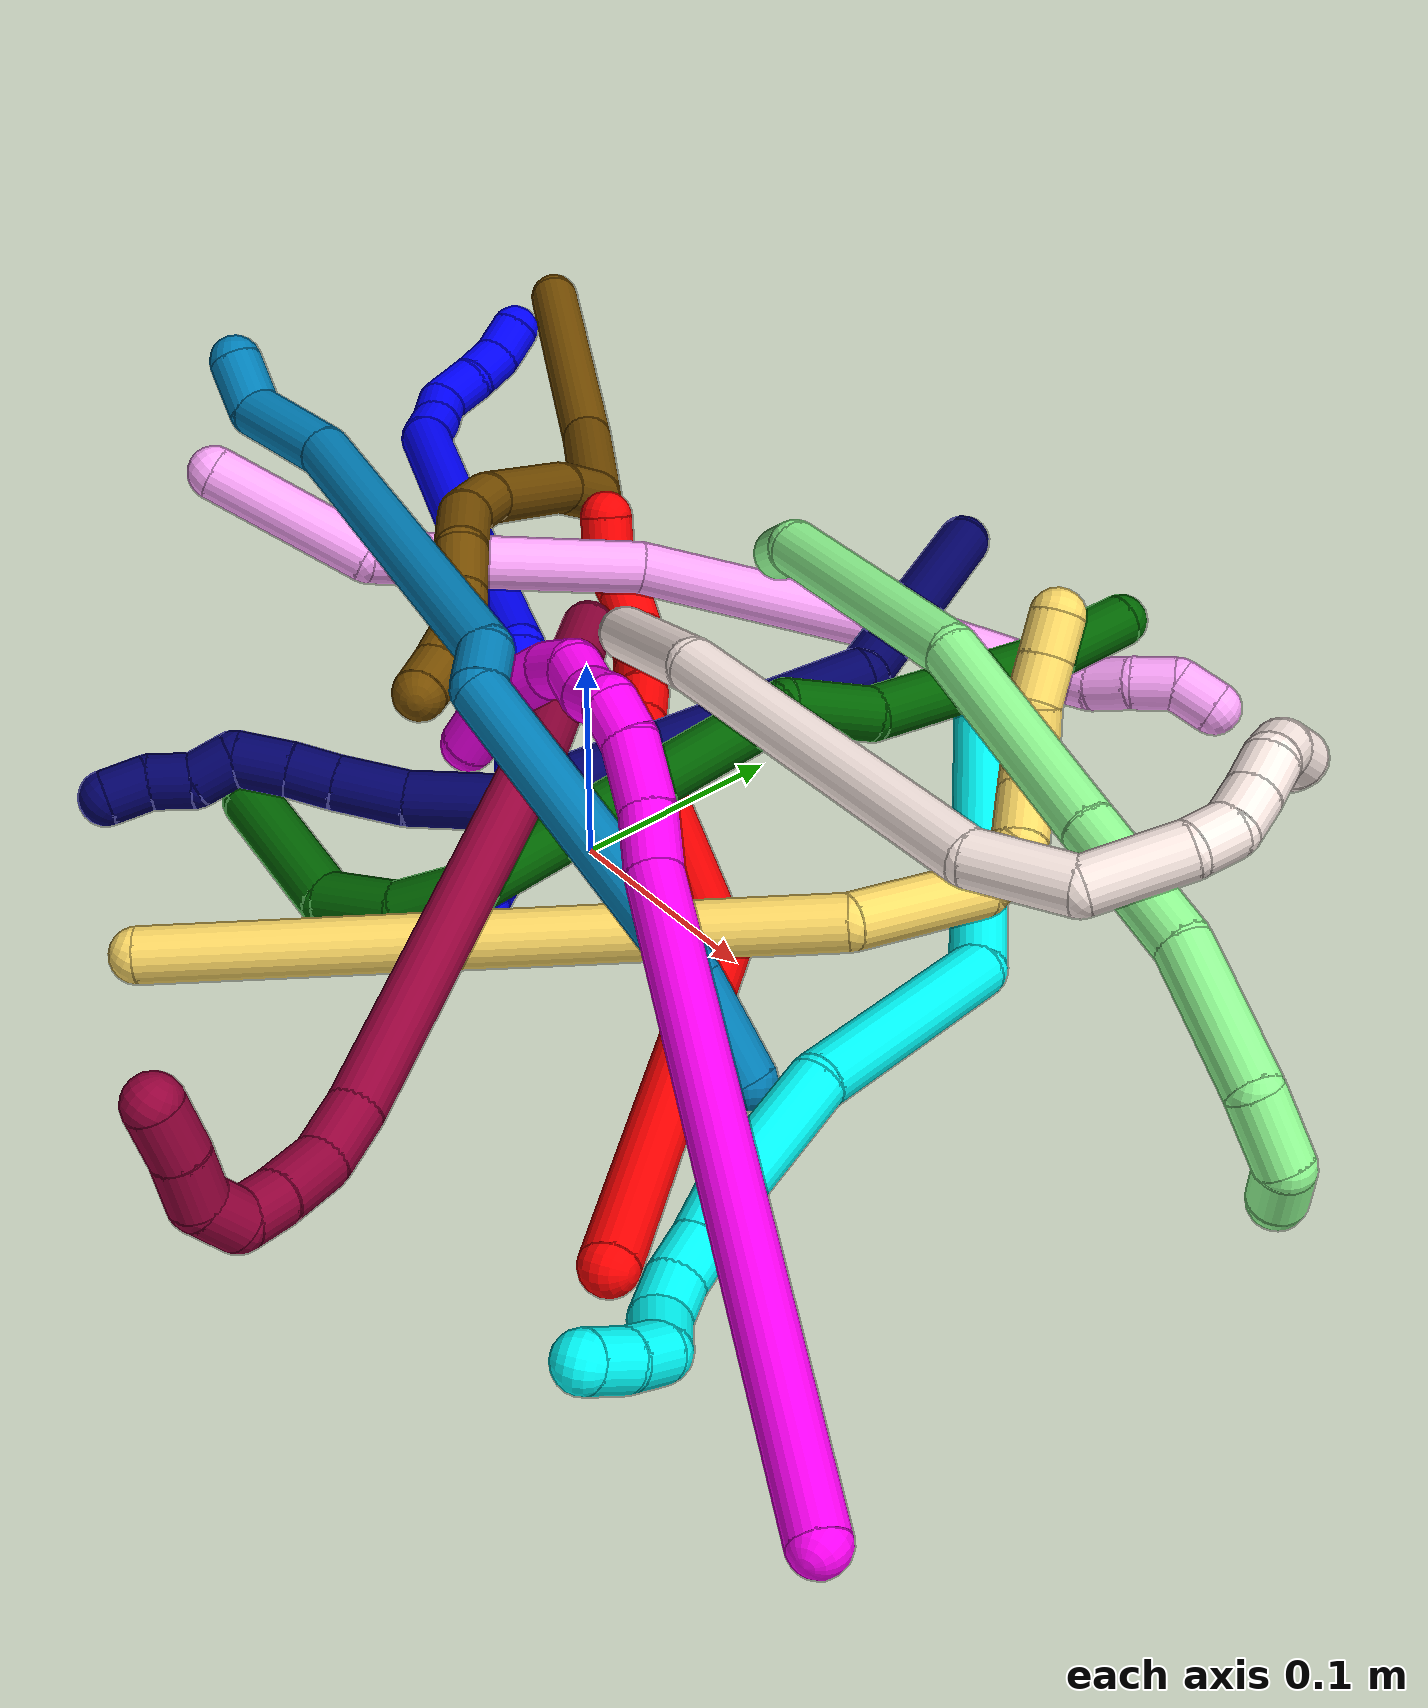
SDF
<sdf version="1.7">
 <world name="default">
  <plugin name="TubeGeneratorPlugin" filename="libtube_generator_plugin.so"/>
  <model name="photoneo_s_sensor">
   <static>1</static>
   <pose>0 0 2 1.57079 1.57079 3.14159</pose>
   <link name="link">
    <inertial><mass>0.1</mass></inertial>
    <sensor name="sensor" type="depth">
     <update_rate>30</update_rate>
     <camera>
      <horizontal_fov>1.22</horizontal_fov>
      <image><width>1920</width><height>1200</height><format>B8G8R8</format></image>
      <clip><near>0.1</near><far>4</far></clip>
      <depth_camera><output>points</output></depth_camera>
     </camera>
     <plugin name="camera_plugin" filename="libgazebo_ros_depth_camera.so">
      <baseline>0.2</baseline>
      <alwaysOn>1</alwaysOn>
      <updateRate>0.0</updateRate>
      <cameraName>camera_ir</cameraName>
      <imageTopicName>/camera/color/image_raw</imageTopicName>
      <cameraInfoTopicName>/camera/color/camera_info</cameraInfoTopicName>
      <depthImageTopicName>/camera/depth/image_raw</depthImageTopicName>
      <depthImageCameraInfoTopicName>/camera/depth/camera_info</depthImageCameraInfoTopicName>
      <pointCloudTopicName>/camera/depth/points</pointCloudTopicName>
      <frameName>fr_optical</frameName>
      <pointCloudCutoff>0.1</pointCloudCutoff>
      <pointCloudCutoffMax>2.0</pointCloudCutoffMax>
      <distortionK1>0</distortionK1>
      <distortionK2>0</distortionK2>
      <distortionK3>0</distortionK3>
      <distortionT1>0</distortionT1>
      <distortionT2>0</distortionT2>
      <CxPrime>0</CxPrime>
      <Cx>0</Cx>
      <Cy>0</Cy>
      <focalLength>0</focalLength>
      <hackBaseline>0</hackBaseline>
     </plugin>
    </sensor>
   </link>
  </model>
  <gravity>0 0 -9.8</gravity>
  <magnetic_field>6e-06 2.3e-05 -4.2e-05</magnetic_field>
  <atmosphere type="adiabatic"/>
  <physics name="default_physics" default="0" type="ode">
   <max_step_size>0.003</max_step_size>
   <real_time_factor>1</real_time_factor>
   <real_time_update_rate>1000</real_time_update_rate>
   <max_contacts>10000</max_contacts>
   <ode>
    <solver>
     <type>quick</type>
     <iters>100</iters>
     <sor>1.3</sor>
     <use_dynamic_moi_rescaling>0</use_dynamic_moi_rescaling>
    </solver>
    <constraints>
     <contact_max_correcting_vel>0</contact_max_correcting_vel>
     <contact_surface_layer>0.001</contact_surface_layer>
     <cfm>0</cfm>
     <erp>0.2</erp>
    </constraints>
   </ode>
  </physics>
  <scene><ambient>0.4 0.4 0.4 1</ambient><background>0.7 0.7 0.7 1</background><shadows>0</shadows></scene>
  <audio><device>default</device></audio>
  <spherical_coordinates>
   <surface_model>EARTH_WGS84</surface_model>
   <latitude_deg>0</latitude_deg>
   <longitude_deg>0</longitude_deg>
   <elevation>0</elevation>
   <heading_deg>0</heading_deg>
  </spherical_coordinates>
  <model name="bin">
   <static>1</static>
   <link name="bottom">
    <collision name="collision-bottom">
     <pose>0 0 -0.01 0 -0 0</pose>
     <geometry><box><size>0.8 0.6 0.02</size></box></geometry>
     <surface>
      <friction><ode><mu>100</mu><mu2>100</mu2></ode></friction>
      <contact><collide_bitmask>65535</collide_bitmask></contact>
     </surface>
    </collision>
   </link>
   <link name="west_wall">
    <collision name="collision-west_wall">
     <pose>-0.41 0 0.1 0 -0 0</pose>
     <geometry><box><size>0.02 0.6 0.2</size></box></geometry>
     <surface>
      <friction><ode><mu>100</mu><mu2>100</mu2></ode></friction>
      <contact><collide_bitmask>65535</collide_bitmask></contact>
     </surface>
    </collision>
   </link>
   <link name="east_wall">
    <collision name="collision-east_wall">
     <pose>0.41 0 0.1 0 -0 0</pose>
     <geometry><box><size>0.02 0.6 0.2</size></box></geometry>
     <surface>
      <friction><ode><mu>100</mu><mu2>100</mu2></ode></friction>
      <contact><collide_bitmask>65535</collide_bitmask></contact>
     </surface>
    </collision>
   </link>
   <link name="south_wall">
    <collision name="collision-south_wall">
     <pose>0 -0.31 0.1 0 -0 0</pose>
     <geometry><box><size>0.8 0.02 0.2</size></box></geometry>
     <surface>
      <friction><ode><mu>100</mu><mu2>100</mu2></ode></friction>
      <contact><collide_bitmask>65535</collide_bitmask></contact>
     </surface>
    </collision>
   </link>
   <link name="north_wall">
    <collision name="collision-north_wall">
     <pose>0 0.31 0.1 0 -0 0</pose>
     <geometry><box><size>0.8 0.02 0.2</size></box></geometry>
     <surface>
      <friction><ode><mu>100</mu><mu2>100</mu2></ode></friction>
      <contact><collide_bitmask>65535</collide_bitmask></contact>
     </surface>
    </collision>
   </link>
  </model>
  <model name="1">
   <static>0</static>
   <link name="1">
    <collision name="collision-cylinder-e_1_1_4">
     <pose>-0.022532 0.003399 0.024227 -0.139371 -0.744287 0.054476</pose>
     <geometry><cylinder><radius>0.0125</radius><length>0.066519</length></cylinder></geometry>
     <surface>
      <friction><ode><mu>1.16</mu><mu2>1.16</mu2><slip1>0</slip1><slip2>0</slip2></ode></friction>
      <contact><ode><kp>1e+06</kp><kd>1</kd><max_vel>0</max_vel><min_depth>0.001</min_depth></ode></contact>
     </surface>
    </collision>
    <visual name="visual-cylinder-e_1_1_4">
     <pose>-0.022532 0.003399 0.024227 -0.139371 -0.744287 0.054476</pose>
     <geometry><cylinder><radius>0.0125</radius><length>0.066519</length></cylinder></geometry>
     <material><ambient>0 0 1 1</ambient></material>
    </visual>
    <collision name="collision-cylinder-e_2_4_5">
     <pose>-0.048706 0.010806 0.060787 -0.31429 -0.273842 0.043657</pose>
     <geometry><cylinder><radius>0.0125</radius><length>0.026939</length></cylinder></geometry>
     <surface>
      <friction><ode><mu>1.16</mu><mu2>1.16</mu2><slip1>0</slip1><slip2>0</slip2></ode></friction>
      <contact><ode><kp>1e+06</kp><kd>1</kd><max_vel>0</max_vel><min_depth>0.001</min_depth></ode></contact>
     </surface>
    </collision>
    <visual name="visual-cylinder-e_2_4_5">
     <pose>-0.048706 0.010806 0.060787 -0.31429 -0.273842 0.043657</pose>
     <geometry><cylinder><radius>0.0125</radius><length>0.026939</length></cylinder></geometry>
     <material><ambient>0 0 1 1</ambient></material>
    </visual>
    <collision name="collision-cylinder-e_3_5_6">
     <pose>-0.062816 0.03041 0.097484 -0.569361 -0.347205 0.102545</pose>
     <geometry><cylinder><radius>0.0125</radius><length>0.061529</length></cylinder></geometry>
     <surface>
      <friction><ode><mu>1.16</mu><mu2>1.16</mu2><slip1>0</slip1><slip2>0</slip2></ode></friction>
      <contact><ode><kp>1e+06</kp><kd>1</kd><max_vel>0</max_vel><min_depth>0.001</min_depth></ode></contact>
     </surface>
    </collision>
    <visual name="visual-cylinder-e_3_5_6">
     <pose>-0.062816 0.03041 0.097484 -0.569361 -0.347205 0.102545</pose>
     <geometry><cylinder><radius>0.0125</radius><length>0.061529</length></cylinder></geometry>
     <material><ambient>0 0 1 1</ambient></material>
    </visual>
    <collision name="collision-cylinder-e_4_6_7">
     <pose>-0.083694 0.044402 0.168478 0.034365 -0.219523 -0.003788</pose>
     <geometry><cylinder><radius>0.0125</radius><length>0.095607</length></cylinder></geometry>
     <surface>
      <friction><ode><mu>1.16</mu><mu2>1.16</mu2><slip1>0</slip1><slip2>0</slip2></ode></friction>
      <contact><ode><kp>1e+06</kp><kd>1</kd><max_vel>0</max_vel><min_depth>0.001</min_depth></ode></contact>
     </surface>
    </collision>
    <visual name="visual-cylinder-e_4_6_7">
     <pose>-0.083694 0.044402 0.168478 0.034365 -0.219523 -0.003788</pose>
     <geometry><cylinder><radius>0.0125</radius><length>0.095607</length></cylinder></geometry>
     <material><ambient>0 0 1 1</ambient></material>
    </visual>
    <collision name="collision-cylinder-e_5_7_8">
     <pose>-0.110446 0.042126 0.284973 0.009628 -0.229764 -0.001111</pose>
     <geometry><cylinder><radius>0.0125</radius><length>0.14351</length></cylinder></geometry>
     <surface>
      <friction><ode><mu>1.16</mu><mu2>1.16</mu2><slip1>0</slip1><slip2>0</slip2></ode></friction>
      <contact><ode><kp>1e+06</kp><kd>1</kd><max_vel>0</max_vel><min_depth>0.001</min_depth></ode></contact>
     </surface>
    </collision>
    <visual name="visual-cylinder-e_5_7_8">
     <pose>-0.110446 0.042126 0.284973 0.009628 -0.229764 -0.001111</pose>
     <geometry><cylinder><radius>0.0125</radius><length>0.14351</length></cylinder></geometry>
     <material><ambient>0 0 1 1</ambient></material>
    </visual>
    <collision name="collision-cylinder-e_6_8_9">
     <pose>-0.13328 0.041199 0.363332 0.029959 -0.652403 -0.010135</pose>
     <geometry><cylinder><radius>0.0125</radius><length>0.021385</length></cylinder></geometry>
     <surface>
      <friction><ode><mu>1.16</mu><mu2>1.16</mu2><slip1>0</slip1><slip2>0</slip2></ode></friction>
      <contact><ode><kp>1e+06</kp><kd>1</kd><max_vel>0</max_vel><min_depth>0.001</min_depth></ode></contact>
     </surface>
    </collision>
    <visual name="visual-cylinder-e_6_8_9">
     <pose>-0.13328 0.041199 0.363332 0.029959 -0.652403 -0.010135</pose>
     <geometry><cylinder><radius>0.0125</radius><length>0.021385</length></cylinder></geometry>
     <material><ambient>0 0 1 1</ambient></material>
    </visual>
    <collision name="collision-cylinder-e_7_9_10">
     <pose>-0.145247 0.041903 0.380455 -0.110575 -0.562575 0.03198</pose>
     <geometry><cylinder><radius>0.0125</radius><length>0.020531</length></cylinder></geometry>
     <surface>
      <friction><ode><mu>1.16</mu><mu2>1.16</mu2><slip1>0</slip1><slip2>0</slip2></ode></friction>
      <contact><ode><kp>1e+06</kp><kd>1</kd><max_vel>0</max_vel><min_depth>0.001</min_depth></ode></contact>
     </surface>
    </collision>
    <visual name="visual-cylinder-e_7_9_10">
     <pose>-0.145247 0.041903 0.380455 -0.110575 -0.562575 0.03198</pose>
     <geometry><cylinder><radius>0.0125</radius><length>0.020531</length></cylinder></geometry>
     <material><ambient>0 0 1 1</ambient></material>
    </visual>
    <collision name="collision-cylinder-e_8_10_11">
     <pose>-0.161064 0.04676 0.391856 -0.953071 -1.13767 0.637551</pose>
     <geometry><cylinder><radius>0.0125</radius><length>0.022788</length></cylinder></geometry>
     <surface>
      <friction><ode><mu>1.16</mu><mu2>1.16</mu2><slip1>0</slip1><slip2>0</slip2></ode></friction>
      <contact><ode><kp>1e+06</kp><kd>1</kd><max_vel>0</max_vel><min_depth>0.001</min_depth></ode></contact>
     </surface>
    </collision>
    <visual name="visual-cylinder-e_8_10_11">
     <pose>-0.161064 0.04676 0.391856 -0.953071 -1.13767 0.637551</pose>
     <geometry><cylinder><radius>0.0125</radius><length>0.022788</length></cylinder></geometry>
     <material><ambient>0 0 1 1</ambient></material>
    </visual>
    <collision name="collision-cylinder-e_9_11_12">
     <pose>-0.180379 0.053143 0.399441 -0.476351 -1.02752 0.272314</pose>
     <geometry><cylinder><radius>0.0125</radius><length>0.020966</length></cylinder></geometry>
     <surface>
      <friction><ode><mu>1.16</mu><mu2>1.16</mu2><slip1>0</slip1><slip2>0</slip2></ode></friction>
      <contact><ode><kp>1e+06</kp><kd>1</kd><max_vel>0</max_vel><min_depth>0.001</min_depth></ode></contact>
     </surface>
    </collision>
    <visual name="visual-cylinder-e_9_11_12">
     <pose>-0.180379 0.053143 0.399441 -0.476351 -1.02752 0.272314</pose>
     <geometry><cylinder><radius>0.0125</radius><length>0.020966</length></cylinder></geometry>
     <material><ambient>0 0 1 1</ambient></material>
    </visual>
    <collision name="collision-cylinder-e_10_12_2">
     <pose>-0.196802 0.060856 0.408668 -0.86999 -0.827952 0.402795</pose>
     <geometry><cylinder><radius>0.0125</radius><length>0.020226</length></cylinder></geometry>
     <surface>
      <friction><ode><mu>1.16</mu><mu2>1.16</mu2><slip1>0</slip1><slip2>0</slip2></ode></friction>
      <contact><ode><kp>1e+06</kp><kd>1</kd><max_vel>0</max_vel><min_depth>0.001</min_depth></ode></contact>
     </surface>
    </collision>
    <visual name="visual-cylinder-e_10_12_2">
     <pose>-0.196802 0.060856 0.408668 -0.86999 -0.827952 0.402795</pose>
     <geometry><cylinder><radius>0.0125</radius><length>0.020226</length></cylinder></geometry>
     <material><ambient>0 0 1 1</ambient></material>
    </visual>
    <collision name="collision-sphere-2">
     <pose>-0.204251 0.066084 0.413079 0 -0 0</pose>
     <geometry><sphere><radius>0.0125</radius></sphere></geometry>
     <surface>
      <friction><ode><mu>1.16</mu><mu2>1.16</mu2><slip1>0</slip1><slip2>0</slip2></ode></friction>
      <contact><ode><kp>1e+06</kp><kd>1</kd><max_vel>0</max_vel><min_depth>0.001</min_depth></ode></contact>
     </surface>
    </collision>
    <visual name="visual-sphere-2">
     <pose>-0.204251 0.066084 0.413079 0 -0 0</pose>
     <geometry><sphere><radius>0.0125</radius></sphere></geometry>
     <material><ambient>0 0 1 1</ambient></material>
    </visual>
    <collision name="collision-sphere-12">
     <pose>-0.189353 0.055628 0.404257 0 -0 0</pose>
     <geometry><sphere><radius>0.0125</radius></sphere></geometry>
     <surface>
      <friction><ode><mu>1.16</mu><mu2>1.16</mu2><slip1>0</slip1><slip2>0</slip2></ode></friction>
      <contact><ode><kp>1e+06</kp><kd>1</kd><max_vel>0</max_vel><min_depth>0.001</min_depth></ode></contact>
     </surface>
    </collision>
    <visual name="visual-sphere-12">
     <pose>-0.189353 0.055628 0.404257 0 -0 0</pose>
     <geometry><sphere><radius>0.0125</radius></sphere></geometry>
     <material><ambient>0 0 1 1</ambient></material>
    </visual>
    <collision name="collision-sphere-11">
     <pose>-0.171406 0.050658 0.394625 0 -0 0</pose>
     <geometry><sphere><radius>0.0125</radius></sphere></geometry>
     <surface>
      <friction><ode><mu>1.16</mu><mu2>1.16</mu2><slip1>0</slip1><slip2>0</slip2></ode></friction>
      <contact><ode><kp>1e+06</kp><kd>1</kd><max_vel>0</max_vel><min_depth>0.001</min_depth></ode></contact>
     </surface>
    </collision>
    <visual name="visual-sphere-11">
     <pose>-0.171406 0.050658 0.394625 0 -0 0</pose>
     <geometry><sphere><radius>0.0125</radius></sphere></geometry>
     <material><ambient>0 0 1 1</ambient></material>
    </visual>
    <collision name="collision-sphere-10">
     <pose>-0.150722 0.042861 0.389086 0 -0 0</pose>
     <geometry><sphere><radius>0.0125</radius></sphere></geometry>
     <surface>
      <friction><ode><mu>1.16</mu><mu2>1.16</mu2><slip1>0</slip1><slip2>0</slip2></ode></friction>
      <contact><ode><kp>1e+06</kp><kd>1</kd><max_vel>0</max_vel><min_depth>0.001</min_depth></ode></contact>
     </surface>
    </collision>
    <visual name="visual-sphere-10">
     <pose>-0.150722 0.042861 0.389086 0 -0 0</pose>
     <geometry><sphere><radius>0.0125</radius></sphere></geometry>
     <material><ambient>0 0 1 1</ambient></material>
    </visual>
    <collision name="collision-sphere-9">
     <pose>-0.139771 0.040945 0.371825 0 -0 0</pose>
     <geometry><sphere><radius>0.0125</radius></sphere></geometry>
     <surface>
      <friction><ode><mu>1.16</mu><mu2>1.16</mu2><slip1>0</slip1><slip2>0</slip2></ode></friction>
      <contact><ode><kp>1e+06</kp><kd>1</kd><max_vel>0</max_vel><min_depth>0.001</min_depth></ode></contact>
     </surface>
    </collision>
    <visual name="visual-sphere-9">
     <pose>-0.139771 0.040945 0.371825 0 -0 0</pose>
     <geometry><sphere><radius>0.0125</radius></sphere></geometry>
     <material><ambient>0 0 1 1</ambient></material>
    </visual>
    <collision name="collision-sphere-4">
     <pose>-0.045063 0.006797 0.048455 0 -0 0</pose>
     <geometry><sphere><radius>0.0125</radius></sphere></geometry>
     <surface>
      <friction><ode><mu>1.16</mu><mu2>1.16</mu2><slip1>0</slip1><slip2>0</slip2></ode></friction>
      <contact><ode><kp>1e+06</kp><kd>1</kd><max_vel>0</max_vel><min_depth>0.001</min_depth></ode></contact>
     </surface>
    </collision>
    <visual name="visual-sphere-4">
     <pose>-0.045063 0.006797 0.048455 0 -0 0</pose>
     <geometry><sphere><radius>0.0125</radius></sphere></geometry>
     <material><ambient>0 0 1 1</ambient></material>
    </visual>
    <collision name="collision-sphere-1">
     <geometry><sphere><radius>0.0125</radius></sphere></geometry>
     <surface>
      <friction><ode><mu>1.16</mu><mu2>1.16</mu2><slip1>0</slip1><slip2>0</slip2></ode></friction>
      <contact><ode><kp>1e+06</kp><kd>1</kd><max_vel>0</max_vel><min_depth>0.001</min_depth></ode></contact>
     </surface>
    </collision>
    <visual name="visual-sphere-1">
     <geometry><sphere><radius>0.0125</radius></sphere></geometry>
     <material><ambient>0 0 1 1</ambient></material>
    </visual>
    <collision name="collision-sphere-8">
     <pose>-0.126789 0.041454 0.354839 0 -0 0</pose>
     <geometry><sphere><radius>0.0125</radius></sphere></geometry>
     <surface>
      <friction><ode><mu>1.16</mu><mu2>1.16</mu2><slip1>0</slip1><slip2>0</slip2></ode></friction>
      <contact><ode><kp>1e+06</kp><kd>1</kd><max_vel>0</max_vel><min_depth>0.001</min_depth></ode></contact>
     </surface>
    </collision>
    <visual name="visual-sphere-8">
     <pose>-0.126789 0.041454 0.354839 0 -0 0</pose>
     <geometry><sphere><radius>0.0125</radius></sphere></geometry>
     <material><ambient>0 0 1 1</ambient></material>
    </visual>
    <collision name="collision-sphere-5">
     <pose>-0.052348 0.014815 0.073119 0 -0 0</pose>
     <geometry><sphere><radius>0.0125</radius></sphere></geometry>
     <surface>
      <friction><ode><mu>1.16</mu><mu2>1.16</mu2><slip1>0</slip1><slip2>0</slip2></ode></friction>
      <contact><ode><kp>1e+06</kp><kd>1</kd><max_vel>0</max_vel><min_depth>0.001</min_depth></ode></contact>
     </surface>
    </collision>
    <visual name="visual-sphere-5">
     <pose>-0.052348 0.014815 0.073119 0 -0 0</pose>
     <geometry><sphere><radius>0.0125</radius></sphere></geometry>
     <material><ambient>0 0 1 1</ambient></material>
    </visual>
    <collision name="collision-sphere-6">
     <pose>-0.073285 0.046005 0.121849 0 -0 0</pose>
     <geometry><sphere><radius>0.0125</radius></sphere></geometry>
     <surface>
      <friction><ode><mu>1.16</mu><mu2>1.16</mu2><slip1>0</slip1><slip2>0</slip2></ode></friction>
      <contact><ode><kp>1e+06</kp><kd>1</kd><max_vel>0</max_vel><min_depth>0.001</min_depth></ode></contact>
     </surface>
    </collision>
    <visual name="visual-sphere-6">
     <pose>-0.073285 0.046005 0.121849 0 -0 0</pose>
     <geometry><sphere><radius>0.0125</radius></sphere></geometry>
     <material><ambient>0 0 1 1</ambient></material>
    </visual>
    <collision name="collision-sphere-7">
     <pose>-0.094104 0.042799 0.215107 0 -0 0</pose>
     <geometry><sphere><radius>0.0125</radius></sphere></geometry>
     <surface>
      <friction><ode><mu>1.16</mu><mu2>1.16</mu2><slip1>0</slip1><slip2>0</slip2></ode></friction>
      <contact><ode><kp>1e+06</kp><kd>1</kd><max_vel>0</max_vel><min_depth>0.001</min_depth></ode></contact>
     </surface>
    </collision>
    <visual name="visual-sphere-7">
     <pose>-0.094104 0.042799 0.215107 0 -0 0</pose>
     <geometry><sphere><radius>0.0125</radius></sphere></geometry>
     <material><ambient>0 0 1 1</ambient></material>
    </visual>
    <inertial>
     <pose>-0.095586 0.035662 0.214805 0 -0 0</pose>
     <mass>0.5</mass>
     <inertia>
      <ixx>0.000356</ixx>
      <ixy>0</ixy>
      <ixz>0</ixz>
      <iyy>0.000393</iyy>
      <iyz>0</iyz>
      <izz>0.000127</izz>
     </inertia>
    </inertial>
   </link>
   <pose>0.009565 -0.066431 0.01174 1.6538 -0.066859 -1.79056</pose>
  </model>
  <model name="2">
   <static>0</static>
   <link name="2">
    <collision name="collision-cylinder-e_1_1_4">
     <pose>-0.066213 0.060562 -0.033676 -2.07828 -0.762656 1.19671</pose>
     <geometry><cylinder><radius>0.0125</radius><length>0.191686</length></cylinder></geometry>
     <surface>
      <friction><ode><mu>1.16</mu><mu2>1.16</mu2><slip1>0</slip1><slip2>0</slip2></ode></friction>
      <contact><ode><kp>1e+06</kp><kd>1</kd><max_vel>0</max_vel><min_depth>0.001</min_depth></ode></contact>
     </surface>
    </collision>
    <visual name="visual-cylinder-e_1_1_4">
     <pose>-0.066213 0.060562 -0.033676 -2.07828 -0.762656 1.19671</pose>
     <geometry><cylinder><radius>0.0125</radius><length>0.191686</length></cylinder></geometry>
     <material><ambient>1 0 0 1</ambient></material>
    </visual>
    <collision name="collision-cylinder-e_2_4_5">
     <pose>-0.161214 0.137247 -0.103019 -2.71704 -0.634151 1.97933</pose>
     <geometry><cylinder><radius>0.0125</radius><length>0.097178</length></cylinder></geometry>
     <surface>
      <friction><ode><mu>1.16</mu><mu2>1.16</mu2><slip1>0</slip1><slip2>0</slip2></ode></friction>
      <contact><ode><kp>1e+06</kp><kd>1</kd><max_vel>0</max_vel><min_depth>0.001</min_depth></ode></contact>
     </surface>
    </collision>
    <visual name="visual-cylinder-e_2_4_5">
     <pose>-0.161214 0.137247 -0.103019 -2.71704 -0.634151 1.97933</pose>
     <geometry><cylinder><radius>0.0125</radius><length>0.097178</length></cylinder></geometry>
     <material><ambient>1 0 0 1</ambient></material>
    </visual>
    <collision name="collision-cylinder-e_3_5_6">
     <pose>-0.201844 0.15947 -0.150136 -2.65205 -0.739817 1.99708</pose>
     <geometry><cylinder><radius>0.0125</radius><length>0.035129</length></cylinder></geometry>
     <surface>
      <friction><ode><mu>1.16</mu><mu2>1.16</mu2><slip1>0</slip1><slip2>0</slip2></ode></friction>
      <contact><ode><kp>1e+06</kp><kd>1</kd><max_vel>0</max_vel><min_depth>0.001</min_depth></ode></contact>
     </surface>
    </collision>
    <visual name="visual-cylinder-e_3_5_6">
     <pose>-0.201844 0.15947 -0.150136 -2.65205 -0.739817 1.99708</pose>
     <geometry><cylinder><radius>0.0125</radius><length>0.035129</length></cylinder></geometry>
     <material><ambient>1 0 0 1</ambient></material>
    </visual>
    <collision name="collision-cylinder-e_4_6_7">
     <pose>-0.219681 0.169165 -0.168846 -2.68191 -0.637073 1.90741</pose>
     <geometry><cylinder><radius>0.0125</radius><length>0.020158</length></cylinder></geometry>
     <surface>
      <friction><ode><mu>1.16</mu><mu2>1.16</mu2><slip1>0</slip1><slip2>0</slip2></ode></friction>
      <contact><ode><kp>1e+06</kp><kd>1</kd><max_vel>0</max_vel><min_depth>0.001</min_depth></ode></contact>
     </surface>
    </collision>
    <visual name="visual-cylinder-e_4_6_7">
     <pose>-0.219681 0.169165 -0.168846 -2.68191 -0.637073 1.90741</pose>
     <geometry><cylinder><radius>0.0125</radius><length>0.020158</length></cylinder></geometry>
     <material><ambient>1 0 0 1</ambient></material>
    </visual>
    <collision name="collision-cylinder-e_5_7_8">
     <pose>-0.233416 0.179521 -0.182316 -2.31364 -0.700485 1.38722</pose>
     <geometry><cylinder><radius>0.0125</radius><length>0.024015</length></cylinder></geometry>
     <surface>
      <friction><ode><mu>1.16</mu><mu2>1.16</mu2><slip1>0</slip1><slip2>0</slip2></ode></friction>
      <contact><ode><kp>1e+06</kp><kd>1</kd><max_vel>0</max_vel><min_depth>0.001</min_depth></ode></contact>
     </surface>
    </collision>
    <visual name="visual-cylinder-e_5_7_8">
     <pose>-0.233416 0.179521 -0.182316 -2.31364 -0.700485 1.38722</pose>
     <geometry><cylinder><radius>0.0125</radius><length>0.024015</length></cylinder></geometry>
     <material><ambient>1 0 0 1</ambient></material>
    </visual>
    <collision name="collision-cylinder-e_6_8_9">
     <pose>-0.247672 0.195746 -0.19762 -2.33631 -0.460828 1.00688</pose>
     <geometry><cylinder><radius>0.0125</radius><length>0.029309</length></cylinder></geometry>
     <surface>
      <friction><ode><mu>1.16</mu><mu2>1.16</mu2><slip1>0</slip1><slip2>0</slip2></ode></friction>
      <contact><ode><kp>1e+06</kp><kd>1</kd><max_vel>0</max_vel><min_depth>0.001</min_depth></ode></contact>
     </surface>
    </collision>
    <visual name="visual-cylinder-e_6_8_9">
     <pose>-0.247672 0.195746 -0.19762 -2.33631 -0.460828 1.00688</pose>
     <geometry><cylinder><radius>0.0125</radius><length>0.029309</length></cylinder></geometry>
     <material><ambient>1 0 0 1</ambient></material>
    </visual>
    <collision name="collision-cylinder-e_7_9_10">
     <pose>-0.265125 0.216333 -0.218532 -2.38645 -0.592982 1.31272</pose>
     <geometry><cylinder><radius>0.0125</radius><length>0.039137</length></cylinder></geometry>
     <surface>
      <friction><ode><mu>1.16</mu><mu2>1.16</mu2><slip1>0</slip1><slip2>0</slip2></ode></friction>
      <contact><ode><kp>1e+06</kp><kd>1</kd><max_vel>0</max_vel><min_depth>0.001</min_depth></ode></contact>
     </surface>
    </collision>
    <visual name="visual-cylinder-e_7_9_10">
     <pose>-0.265125 0.216333 -0.218532 -2.38645 -0.592982 1.31272</pose>
     <geometry><cylinder><radius>0.0125</radius><length>0.039137</length></cylinder></geometry>
     <material><ambient>1 0 0 1</ambient></material>
    </visual>
    <collision name="collision-cylinder-e_8_10_11">
     <pose>-0.284484 0.226852 -0.236664 3.04636 -0.925274 -2.95107</pose>
     <geometry><cylinder><radius>0.0125</radius><length>0.02109</length></cylinder></geometry>
     <surface>
      <friction><ode><mu>1.16</mu><mu2>1.16</mu2><slip1>0</slip1><slip2>0</slip2></ode></friction>
      <contact><ode><kp>1e+06</kp><kd>1</kd><max_vel>0</max_vel><min_depth>0.001</min_depth></ode></contact>
     </surface>
    </collision>
    <visual name="visual-cylinder-e_8_10_11">
     <pose>-0.284484 0.226852 -0.236664 3.04636 -0.925274 -2.95107</pose>
     <geometry><cylinder><radius>0.0125</radius><length>0.02109</length></cylinder></geometry>
     <material><ambient>1 0 0 1</ambient></material>
    </visual>
    <collision name="collision-cylinder-e_9_11_12">
     <pose>-0.299785 0.226939 -0.250358 -3.0483 -0.748087 2.90486</pose>
     <geometry><cylinder><radius>0.0125</radius><length>0.020222</length></cylinder></geometry>
     <surface>
      <friction><ode><mu>1.16</mu><mu2>1.16</mu2><slip1>0</slip1><slip2>0</slip2></ode></friction>
      <contact><ode><kp>1e+06</kp><kd>1</kd><max_vel>0</max_vel><min_depth>0.001</min_depth></ode></contact>
     </surface>
    </collision>
    <visual name="visual-cylinder-e_9_11_12">
     <pose>-0.299785 0.226939 -0.250358 -3.0483 -0.748087 2.90486</pose>
     <geometry><cylinder><radius>0.0125</radius><length>0.020222</length></cylinder></geometry>
     <material><ambient>1 0 0 1</ambient></material>
    </visual>
    <collision name="collision-cylinder-e_10_12_2">
     <pose>-0.316924 0.223956 -0.259483 2.01439 -1.19345 -1.64301</pose>
     <geometry><cylinder><radius>0.0125</radius><length>0.022075</length></cylinder></geometry>
     <surface>
      <friction><ode><mu>1.16</mu><mu2>1.16</mu2><slip1>0</slip1><slip2>0</slip2></ode></friction>
      <contact><ode><kp>1e+06</kp><kd>1</kd><max_vel>0</max_vel><min_depth>0.001</min_depth></ode></contact>
     </surface>
    </collision>
    <visual name="visual-cylinder-e_10_12_2">
     <pose>-0.316924 0.223956 -0.259483 2.01439 -1.19345 -1.64301</pose>
     <geometry><cylinder><radius>0.0125</radius><length>0.022075</length></cylinder></geometry>
     <material><ambient>1 0 0 1</ambient></material>
    </visual>
    <collision name="collision-sphere-2">
     <pose>-0.327185 0.220283 -0.261228 0 -0 0</pose>
     <geometry><sphere><radius>0.0125</radius></sphere></geometry>
     <surface>
      <friction><ode><mu>1.16</mu><mu2>1.16</mu2><slip1>0</slip1><slip2>0</slip2></ode></friction>
      <contact><ode><kp>1e+06</kp><kd>1</kd><max_vel>0</max_vel><min_depth>0.001</min_depth></ode></contact>
     </surface>
    </collision>
    <visual name="visual-sphere-2">
     <pose>-0.327185 0.220283 -0.261228 0 -0 0</pose>
     <geometry><sphere><radius>0.0125</radius></sphere></geometry>
     <material><ambient>1 0 0 1</ambient></material>
    </visual>
    <collision name="collision-sphere-12">
     <pose>-0.306663 0.227629 -0.257737 0 -0 0</pose>
     <geometry><sphere><radius>0.0125</radius></sphere></geometry>
     <surface>
      <friction><ode><mu>1.16</mu><mu2>1.16</mu2><slip1>0</slip1><slip2>0</slip2></ode></friction>
      <contact><ode><kp>1e+06</kp><kd>1</kd><max_vel>0</max_vel><min_depth>0.001</min_depth></ode></contact>
     </surface>
    </collision>
    <visual name="visual-sphere-12">
     <pose>-0.306663 0.227629 -0.257737 0 -0 0</pose>
     <geometry><sphere><radius>0.0125</radius></sphere></geometry>
     <material><ambient>1 0 0 1</ambient></material>
    </visual>
    <collision name="collision-sphere-11">
     <pose>-0.292907 0.226249 -0.242979 0 -0 0</pose>
     <geometry><sphere><radius>0.0125</radius></sphere></geometry>
     <surface>
      <friction><ode><mu>1.16</mu><mu2>1.16</mu2><slip1>0</slip1><slip2>0</slip2></ode></friction>
      <contact><ode><kp>1e+06</kp><kd>1</kd><max_vel>0</max_vel><min_depth>0.001</min_depth></ode></contact>
     </surface>
    </collision>
    <visual name="visual-sphere-11">
     <pose>-0.292907 0.226249 -0.242979 0 -0 0</pose>
     <geometry><sphere><radius>0.0125</radius></sphere></geometry>
     <material><ambient>1 0 0 1</ambient></material>
    </visual>
    <collision name="collision-sphere-10">
     <pose>-0.27606 0.227455 -0.230348 0 -0 0</pose>
     <geometry><sphere><radius>0.0125</radius></sphere></geometry>
     <surface>
      <friction><ode><mu>1.16</mu><mu2>1.16</mu2><slip1>0</slip1><slip2>0</slip2></ode></friction>
      <contact><ode><kp>1e+06</kp><kd>1</kd><max_vel>0</max_vel><min_depth>0.001</min_depth></ode></contact>
     </surface>
    </collision>
    <visual name="visual-sphere-10">
     <pose>-0.27606 0.227455 -0.230348 0 -0 0</pose>
     <geometry><sphere><radius>0.0125</radius></sphere></geometry>
     <material><ambient>1 0 0 1</ambient></material>
    </visual>
    <collision name="collision-sphere-9">
     <pose>-0.254189 0.20521 -0.206715 0 -0 0</pose>
     <geometry><sphere><radius>0.0125</radius></sphere></geometry>
     <surface>
      <friction><ode><mu>1.16</mu><mu2>1.16</mu2><slip1>0</slip1><slip2>0</slip2></ode></friction>
      <contact><ode><kp>1e+06</kp><kd>1</kd><max_vel>0</max_vel><min_depth>0.001</min_depth></ode></contact>
     </surface>
    </collision>
    <visual name="visual-sphere-9">
     <pose>-0.254189 0.20521 -0.206715 0 -0 0</pose>
     <geometry><sphere><radius>0.0125</radius></sphere></geometry>
     <material><ambient>1 0 0 1</ambient></material>
    </visual>
    <collision name="collision-sphere-4">
     <pose>-0.132425 0.121124 -0.067352 0 -0 0</pose>
     <geometry><sphere><radius>0.0125</radius></sphere></geometry>
     <surface>
      <friction><ode><mu>1.16</mu><mu2>1.16</mu2><slip1>0</slip1><slip2>0</slip2></ode></friction>
      <contact><ode><kp>1e+06</kp><kd>1</kd><max_vel>0</max_vel><min_depth>0.001</min_depth></ode></contact>
     </surface>
    </collision>
    <visual name="visual-sphere-4">
     <pose>-0.132425 0.121124 -0.067352 0 -0 0</pose>
     <geometry><sphere><radius>0.0125</radius></sphere></geometry>
     <material><ambient>1 0 0 1</ambient></material>
    </visual>
    <collision name="collision-sphere-1">
     <geometry><sphere><radius>0.0125</radius></sphere></geometry>
     <surface>
      <friction><ode><mu>1.16</mu><mu2>1.16</mu2><slip1>0</slip1><slip2>0</slip2></ode></friction>
      <contact><ode><kp>1e+06</kp><kd>1</kd><max_vel>0</max_vel><min_depth>0.001</min_depth></ode></contact>
     </surface>
    </collision>
    <visual name="visual-sphere-1">
     <geometry><sphere><radius>0.0125</radius></sphere></geometry>
     <material><ambient>1 0 0 1</ambient></material>
    </visual>
    <collision name="collision-sphere-8">
     <pose>-0.241156 0.186282 -0.188525 0 -0 0</pose>
     <geometry><sphere><radius>0.0125</radius></sphere></geometry>
     <surface>
      <friction><ode><mu>1.16</mu><mu2>1.16</mu2><slip1>0</slip1><slip2>0</slip2></ode></friction>
      <contact><ode><kp>1e+06</kp><kd>1</kd><max_vel>0</max_vel><min_depth>0.001</min_depth></ode></contact>
     </surface>
    </collision>
    <visual name="visual-sphere-8">
     <pose>-0.241156 0.186282 -0.188525 0 -0 0</pose>
     <geometry><sphere><radius>0.0125</radius></sphere></geometry>
     <material><ambient>1 0 0 1</ambient></material>
    </visual>
    <collision name="collision-sphere-5">
     <pose>-0.190003 0.15337 -0.138686 0 -0 0</pose>
     <geometry><sphere><radius>0.0125</radius></sphere></geometry>
     <surface>
      <friction><ode><mu>1.16</mu><mu2>1.16</mu2><slip1>0</slip1><slip2>0</slip2></ode></friction>
      <contact><ode><kp>1e+06</kp><kd>1</kd><max_vel>0</max_vel><min_depth>0.001</min_depth></ode></contact>
     </surface>
    </collision>
    <visual name="visual-sphere-5">
     <pose>-0.190003 0.15337 -0.138686 0 -0 0</pose>
     <geometry><sphere><radius>0.0125</radius></sphere></geometry>
     <material><ambient>1 0 0 1</ambient></material>
    </visual>
    <collision name="collision-sphere-6">
     <pose>-0.213685 0.16557 -0.161585 0 -0 0</pose>
     <geometry><sphere><radius>0.0125</radius></sphere></geometry>
     <surface>
      <friction><ode><mu>1.16</mu><mu2>1.16</mu2><slip1>0</slip1><slip2>0</slip2></ode></friction>
      <contact><ode><kp>1e+06</kp><kd>1</kd><max_vel>0</max_vel><min_depth>0.001</min_depth></ode></contact>
     </surface>
    </collision>
    <visual name="visual-sphere-6">
     <pose>-0.213685 0.16557 -0.161585 0 -0 0</pose>
     <geometry><sphere><radius>0.0125</radius></sphere></geometry>
     <material><ambient>1 0 0 1</ambient></material>
    </visual>
    <collision name="collision-sphere-7">
     <pose>-0.225676 0.172759 -0.176107 0 -0 0</pose>
     <geometry><sphere><radius>0.0125</radius></sphere></geometry>
     <surface>
      <friction><ode><mu>1.16</mu><mu2>1.16</mu2><slip1>0</slip1><slip2>0</slip2></ode></friction>
      <contact><ode><kp>1e+06</kp><kd>1</kd><max_vel>0</max_vel><min_depth>0.001</min_depth></ode></contact>
     </surface>
    </collision>
    <visual name="visual-sphere-7">
     <pose>-0.225676 0.172759 -0.176107 0 -0 0</pose>
     <geometry><sphere><radius>0.0125</radius></sphere></geometry>
     <material><ambient>1 0 0 1</ambient></material>
    </visual>
    <inertial>
     <pose>-0.164353 0.133581 -0.119299 0 -0 0</pose>
     <mass>0.5</mass>
     <inertia>
      <ixx>0.000578</ixx>
      <ixy>0</ixy>
      <ixz>0</ixz>
      <iyy>0.000776</iyy>
      <iyz>0</iyz>
      <izz>4.1e-05</izz>
     </inertia>
    </inertial>
   </link>
   <pose>0.217287 -0.160931 0.012265 -1.27794 0.797908 -1.07318</pose>
  </model>
  <model name="3">
   <static>0</static>
   <link name="3">
    <collision name="collision-cylinder-e_1_1_4">
     <pose>0.050797 -0.078944 0.021488 1.30505 0.555623 0.429165</pose>
     <geometry><cylinder><radius>0.0125</radius><length>0.192606</length></cylinder></geometry>
     <surface>
      <friction><ode><mu>1.16</mu><mu2>1.16</mu2><slip1>0</slip1><slip2>0</slip2></ode></friction>
      <contact><ode><kp>1e+06</kp><kd>1</kd><max_vel>0</max_vel><min_depth>0.001</min_depth></ode></contact>
     </surface>
    </collision>
    <visual name="visual-cylinder-e_1_1_4">
     <pose>0.050797 -0.078944 0.021488 1.30505 0.555623 0.429165</pose>
     <geometry><cylinder><radius>0.0125</radius><length>0.192606</length></cylinder></geometry>
     <material><ambient>0.003922 1 0.996078 1</ambient></material>
    </visual>
    <collision name="collision-cylinder-e_2_4_5">
     <pose>0.123667 -0.208193 0.02252 1.957 0.386064 0.565416</pose>
     <geometry><cylinder><radius>0.0125</radius><length>0.117237</length></cylinder></geometry>
     <surface>
      <friction><ode><mu>1.16</mu><mu2>1.16</mu2><slip1>0</slip1><slip2>0</slip2></ode></friction>
      <contact><ode><kp>1e+06</kp><kd>1</kd><max_vel>0</max_vel><min_depth>0.001</min_depth></ode></contact>
     </surface>
    </collision>
    <visual name="visual-cylinder-e_2_4_5">
     <pose>0.123667 -0.208193 0.02252 1.957 0.386064 0.565416</pose>
     <geometry><cylinder><radius>0.0125</radius><length>0.117237</length></cylinder></geometry>
     <material><ambient>0.003922 1 0.996078 1</ambient></material>
    </visual>
    <collision name="collision-cylinder-e_3_5_6">
     <pose>0.167306 -0.281887 -0.007266 1.9504 0.708206 0.998777</pose>
     <geometry><cylinder><radius>0.0125</radius><length>0.066311</length></cylinder></geometry>
     <surface>
      <friction><ode><mu>1.16</mu><mu2>1.16</mu2><slip1>0</slip1><slip2>0</slip2></ode></friction>
      <contact><ode><kp>1e+06</kp><kd>1</kd><max_vel>0</max_vel><min_depth>0.001</min_depth></ode></contact>
     </surface>
    </collision>
    <visual name="visual-cylinder-e_3_5_6">
     <pose>0.167306 -0.281887 -0.007266 1.9504 0.708206 0.998777</pose>
     <geometry><cylinder><radius>0.0125</radius><length>0.066311</length></cylinder></geometry>
     <material><ambient>0.003922 1 0.996078 1</ambient></material>
    </visual>
    <collision name="collision-cylinder-e_4_6_7">
     <pose>0.196626 -0.313399 -0.017892 1.72878 0.755902 0.871005</pose>
     <geometry><cylinder><radius>0.0125</radius><length>0.022605</length></cylinder></geometry>
     <surface>
      <friction><ode><mu>1.16</mu><mu2>1.16</mu2><slip1>0</slip1><slip2>0</slip2></ode></friction>
      <contact><ode><kp>1e+06</kp><kd>1</kd><max_vel>0</max_vel><min_depth>0.001</min_depth></ode></contact>
     </surface>
    </collision>
    <visual name="visual-cylinder-e_4_6_7">
     <pose>0.196626 -0.313399 -0.017892 1.72878 0.755902 0.871005</pose>
     <geometry><cylinder><radius>0.0125</radius><length>0.022605</length></cylinder></geometry>
     <material><ambient>0.003922 1 0.996078 1</ambient></material>
    </visual>
    <collision name="collision-cylinder-e_5_7_8">
     <pose>0.211247 -0.328614 -0.021206 1.8482 0.749796 0.960928</pose>
     <geometry><cylinder><radius>0.0125</radius><length>0.020156</length></cylinder></geometry>
     <surface>
      <friction><ode><mu>1.16</mu><mu2>1.16</mu2><slip1>0</slip1><slip2>0</slip2></ode></friction>
      <contact><ode><kp>1e+06</kp><kd>1</kd><max_vel>0</max_vel><min_depth>0.001</min_depth></ode></contact>
     </surface>
    </collision>
    <visual name="visual-cylinder-e_5_7_8">
     <pose>0.211247 -0.328614 -0.021206 1.8482 0.749796 0.960928</pose>
     <geometry><cylinder><radius>0.0125</radius><length>0.020156</length></cylinder></geometry>
     <material><ambient>0.003922 1 0.996078 1</ambient></material>
    </visual>
    <collision name="collision-cylinder-e_6_8_9">
     <pose>0.223936 -0.344026 -0.023148 1.56154 0.610524 0.605237</pose>
     <geometry><cylinder><radius>0.0125</radius><length>0.020306</length></cylinder></geometry>
     <surface>
      <friction><ode><mu>1.16</mu><mu2>1.16</mu2><slip1>0</slip1><slip2>0</slip2></ode></friction>
      <contact><ode><kp>1e+06</kp><kd>1</kd><max_vel>0</max_vel><min_depth>0.001</min_depth></ode></contact>
     </surface>
    </collision>
    <visual name="visual-cylinder-e_6_8_9">
     <pose>0.223936 -0.344026 -0.023148 1.56154 0.610524 0.605237</pose>
     <geometry><cylinder><radius>0.0125</radius><length>0.020306</length></cylinder></geometry>
     <material><ambient>0.003922 1 0.996078 1</ambient></material>
    </visual>
    <collision name="collision-cylinder-e_7_9_10">
     <pose>0.23305 -0.361616 -0.020026 1.25348 0.325515 0.236707</pose>
     <geometry><cylinder><radius>0.0125</radius><length>0.020598</length></cylinder></geometry>
     <surface>
      <friction><ode><mu>1.16</mu><mu2>1.16</mu2><slip1>0</slip1><slip2>0</slip2></ode></friction>
      <contact><ode><kp>1e+06</kp><kd>1</kd><max_vel>0</max_vel><min_depth>0.001</min_depth></ode></contact>
     </surface>
    </collision>
    <visual name="visual-cylinder-e_7_9_10">
     <pose>0.23305 -0.361616 -0.020026 1.25348 0.325515 0.236707</pose>
     <geometry><cylinder><radius>0.0125</radius><length>0.020598</length></cylinder></geometry>
     <material><ambient>0.003922 1 0.996078 1</ambient></material>
    </visual>
    <collision name="collision-cylinder-e_8_10_11">
     <pose>0.237053 -0.379955 -0.02116 2.00255 0.070954 0.110748</pose>
     <geometry><cylinder><radius>0.0125</radius><length>0.020019</length></cylinder></geometry>
     <surface>
      <friction><ode><mu>1.16</mu><mu2>1.16</mu2><slip1>0</slip1><slip2>0</slip2></ode></friction>
      <contact><ode><kp>1e+06</kp><kd>1</kd><max_vel>0</max_vel><min_depth>0.001</min_depth></ode></contact>
     </surface>
    </collision>
    <visual name="visual-cylinder-e_8_10_11">
     <pose>0.237053 -0.379955 -0.02116 2.00255 0.070954 0.110748</pose>
     <geometry><cylinder><radius>0.0125</radius><length>0.020019</length></cylinder></geometry>
     <material><ambient>0.003922 1 0.996078 1</ambient></material>
    </visual>
    <collision name="collision-cylinder-e_9_11_2">
     <pose>0.237528 -0.397389 -0.030958 2.16236 -0.023285 -0.043691</pose>
     <geometry><cylinder><radius>0.0125</radius><length>0.020161</length></cylinder></geometry>
     <surface>
      <friction><ode><mu>1.16</mu><mu2>1.16</mu2><slip1>0</slip1><slip2>0</slip2></ode></friction>
      <contact><ode><kp>1e+06</kp><kd>1</kd><max_vel>0</max_vel><min_depth>0.001</min_depth></ode></contact>
     </surface>
    </collision>
    <visual name="visual-cylinder-e_9_11_2">
     <pose>0.237528 -0.397389 -0.030958 2.16236 -0.023285 -0.043691</pose>
     <geometry><cylinder><radius>0.0125</radius><length>0.020161</length></cylinder></geometry>
     <material><ambient>0.003922 1 0.996078 1</ambient></material>
    </visual>
    <collision name="collision-sphere-2">
     <pose>0.237294 -0.405754 -0.036578 0 -0 0</pose>
     <geometry><sphere><radius>0.0125</radius></sphere></geometry>
     <surface>
      <friction><ode><mu>1.16</mu><mu2>1.16</mu2><slip1>0</slip1><slip2>0</slip2></ode></friction>
      <contact><ode><kp>1e+06</kp><kd>1</kd><max_vel>0</max_vel><min_depth>0.001</min_depth></ode></contact>
     </surface>
    </collision>
    <visual name="visual-sphere-2">
     <pose>0.237294 -0.405754 -0.036578 0 -0 0</pose>
     <geometry><sphere><radius>0.0125</radius></sphere></geometry>
     <material><ambient>0.003922 1 0.996078 1</ambient></material>
    </visual>
    <collision name="collision-sphere-11">
     <pose>0.237763 -0.389023 -0.025338 0 -0 0</pose>
     <geometry><sphere><radius>0.0125</radius></sphere></geometry>
     <surface>
      <friction><ode><mu>1.16</mu><mu2>1.16</mu2><slip1>0</slip1><slip2>0</slip2></ode></friction>
      <contact><ode><kp>1e+06</kp><kd>1</kd><max_vel>0</max_vel><min_depth>0.001</min_depth></ode></contact>
     </surface>
    </collision>
    <visual name="visual-sphere-11">
     <pose>0.237763 -0.389023 -0.025338 0 -0 0</pose>
     <geometry><sphere><radius>0.0125</radius></sphere></geometry>
     <material><ambient>0.003922 1 0.996078 1</ambient></material>
    </visual>
    <collision name="collision-sphere-10">
     <pose>0.236344 -0.370887 -0.016982 0 -0 0</pose>
     <geometry><sphere><radius>0.0125</radius></sphere></geometry>
     <surface>
      <friction><ode><mu>1.16</mu><mu2>1.16</mu2><slip1>0</slip1><slip2>0</slip2></ode></friction>
      <contact><ode><kp>1e+06</kp><kd>1</kd><max_vel>0</max_vel><min_depth>0.001</min_depth></ode></contact>
     </surface>
    </collision>
    <visual name="visual-sphere-10">
     <pose>0.236344 -0.370887 -0.016982 0 -0 0</pose>
     <geometry><sphere><radius>0.0125</radius></sphere></geometry>
     <material><ambient>0.003922 1 0.996078 1</ambient></material>
    </visual>
    <collision name="collision-sphere-9">
     <pose>0.229756 -0.352345 -0.023071 0 -0 0</pose>
     <geometry><sphere><radius>0.0125</radius></sphere></geometry>
     <surface>
      <friction><ode><mu>1.16</mu><mu2>1.16</mu2><slip1>0</slip1><slip2>0</slip2></ode></friction>
      <contact><ode><kp>1e+06</kp><kd>1</kd><max_vel>0</max_vel><min_depth>0.001</min_depth></ode></contact>
     </surface>
    </collision>
    <visual name="visual-sphere-9">
     <pose>0.229756 -0.352345 -0.023071 0 -0 0</pose>
     <geometry><sphere><radius>0.0125</radius></sphere></geometry>
     <material><ambient>0.003922 1 0.996078 1</ambient></material>
    </visual>
    <collision name="collision-sphere-4">
     <pose>0.101595 -0.157889 0.042975 0 -0 0</pose>
     <geometry><sphere><radius>0.0125</radius></sphere></geometry>
     <surface>
      <friction><ode><mu>1.16</mu><mu2>1.16</mu2><slip1>0</slip1><slip2>0</slip2></ode></friction>
      <contact><ode><kp>1e+06</kp><kd>1</kd><max_vel>0</max_vel><min_depth>0.001</min_depth></ode></contact>
     </surface>
    </collision>
    <visual name="visual-sphere-4">
     <pose>0.101595 -0.157889 0.042975 0 -0 0</pose>
     <geometry><sphere><radius>0.0125</radius></sphere></geometry>
     <material><ambient>0.003922 1 0.996078 1</ambient></material>
    </visual>
    <collision name="collision-sphere-1">
     <geometry><sphere><radius>0.0125</radius></sphere></geometry>
     <surface>
      <friction><ode><mu>1.16</mu><mu2>1.16</mu2><slip1>0</slip1><slip2>0</slip2></ode></friction>
      <contact><ode><kp>1e+06</kp><kd>1</kd><max_vel>0</max_vel><min_depth>0.001</min_depth></ode></contact>
     </surface>
    </collision>
    <visual name="visual-sphere-1">
     <geometry><sphere><radius>0.0125</radius></sphere></geometry>
     <material><ambient>0.003922 1 0.996078 1</ambient></material>
    </visual>
    <collision name="collision-sphere-8">
     <pose>0.218115 -0.335708 -0.023225 0 -0 0</pose>
     <geometry><sphere><radius>0.0125</radius></sphere></geometry>
     <surface>
      <friction><ode><mu>1.16</mu><mu2>1.16</mu2><slip1>0</slip1><slip2>0</slip2></ode></friction>
      <contact><ode><kp>1e+06</kp><kd>1</kd><max_vel>0</max_vel><min_depth>0.001</min_depth></ode></contact>
     </surface>
    </collision>
    <visual name="visual-sphere-8">
     <pose>0.218115 -0.335708 -0.023225 0 -0 0</pose>
     <geometry><sphere><radius>0.0125</radius></sphere></geometry>
     <material><ambient>0.003922 1 0.996078 1</ambient></material>
    </visual>
    <collision name="collision-sphere-5">
     <pose>0.14574 -0.258498 0.002065 0 -0 0</pose>
     <geometry><sphere><radius>0.0125</radius></sphere></geometry>
     <surface>
      <friction><ode><mu>1.16</mu><mu2>1.16</mu2><slip1>0</slip1><slip2>0</slip2></ode></friction>
      <contact><ode><kp>1e+06</kp><kd>1</kd><max_vel>0</max_vel><min_depth>0.001</min_depth></ode></contact>
     </surface>
    </collision>
    <visual name="visual-sphere-5">
     <pose>0.14574 -0.258498 0.002065 0 -0 0</pose>
     <geometry><sphere><radius>0.0125</radius></sphere></geometry>
     <material><ambient>0.003922 1 0.996078 1</ambient></material>
    </visual>
    <collision name="collision-sphere-6">
     <pose>0.188873 -0.305277 -0.016598 0 -0 0</pose>
     <geometry><sphere><radius>0.0125</radius></sphere></geometry>
     <surface>
      <friction><ode><mu>1.16</mu><mu2>1.16</mu2><slip1>0</slip1><slip2>0</slip2></ode></friction>
      <contact><ode><kp>1e+06</kp><kd>1</kd><max_vel>0</max_vel><min_depth>0.001</min_depth></ode></contact>
     </surface>
    </collision>
    <visual name="visual-sphere-6">
     <pose>0.188873 -0.305277 -0.016598 0 -0 0</pose>
     <geometry><sphere><radius>0.0125</radius></sphere></geometry>
     <material><ambient>0.003922 1 0.996078 1</ambient></material>
    </visual>
    <collision name="collision-sphere-7">
     <pose>0.204379 -0.321521 -0.019186 0 -0 0</pose>
     <geometry><sphere><radius>0.0125</radius></sphere></geometry>
     <surface>
      <friction><ode><mu>1.16</mu><mu2>1.16</mu2><slip1>0</slip1><slip2>0</slip2></ode></friction>
      <contact><ode><kp>1e+06</kp><kd>1</kd><max_vel>0</max_vel><min_depth>0.001</min_depth></ode></contact>
     </surface>
    </collision>
    <visual name="visual-sphere-7">
     <pose>0.204379 -0.321521 -0.019186 0 -0 0</pose>
     <geometry><sphere><radius>0.0125</radius></sphere></geometry>
     <material><ambient>0.003922 1 0.996078 1</ambient></material>
    </visual>
    <inertial>
     <pose>0.125923 -0.204132 0.00707 0 -0 0</pose>
     <mass>0.5</mass>
     <inertia>
      <ixx>0.000913</ixx>
      <ixy>0</ixy>
      <ixz>0</ixz>
      <iyy>0.000533</iyy>
      <iyz>0</iyz>
      <izz>0.000246</izz>
     </inertia>
    </inertial>
   </link>
   <pose>0.039183 0.199806 0.011492 -1.62431 0.991654 -1.03307</pose>
  </model>
  <model name="4">
   <static>0</static>
   <link name="4">
    <collision name="collision-cylinder-e_1_1_4">
     <pose>0.023434 0.029203 0.013548 -1.13641 0.629236 -0.409703</pose>
     <geometry><cylinder><radius>0.0125</radius><length>0.079637</length></cylinder></geometry>
     <surface>
      <friction><ode><mu>1.16</mu><mu2>1.16</mu2><slip1>0</slip1><slip2>0</slip2></ode></friction>
      <contact><ode><kp>1e+06</kp><kd>1</kd><max_vel>0</max_vel><min_depth>0.001</min_depth></ode></contact>
     </surface>
    </collision>
    <visual name="visual-cylinder-e_1_1_4">
     <pose>0.023434 0.029203 0.013548 -1.13641 0.629236 -0.409703</pose>
     <geometry><cylinder><radius>0.0125</radius><length>0.079637</length></cylinder></geometry>
     <material><ambient>1 0.65098 0.996078 1</ambient></material>
    </visual>
    <collision name="collision-cylinder-e_2_4_5">
     <pose>0.050347 0.077047 0.04411 -0.83102 0.136964 -0.060505</pose>
     <geometry><cylinder><radius>0.0125</radius><length>0.050954</length></cylinder></geometry>
     <surface>
      <friction><ode><mu>1.16</mu><mu2>1.16</mu2><slip1>0</slip1><slip2>0</slip2></ode></friction>
      <contact><ode><kp>1e+06</kp><kd>1</kd><max_vel>0</max_vel><min_depth>0.001</min_depth></ode></contact>
     </surface>
    </collision>
    <visual name="visual-cylinder-e_2_4_5">
     <pose>0.050347 0.077047 0.04411 -0.83102 0.136964 -0.060505</pose>
     <geometry><cylinder><radius>0.0125</radius><length>0.050954</length></cylinder></geometry>
     <material><ambient>1 0.65098 0.996078 1</ambient></material>
    </visual>
    <collision name="collision-cylinder-e_3_5_6">
     <pose>0.056451 0.127322 0.089035 -0.847833 0.06215 -0.028054</pose>
     <geometry><cylinder><radius>0.0125</radius><length>0.084535</length></cylinder></geometry>
     <surface>
      <friction><ode><mu>1.16</mu><mu2>1.16</mu2><slip1>0</slip1><slip2>0</slip2></ode></friction>
      <contact><ode><kp>1e+06</kp><kd>1</kd><max_vel>0</max_vel><min_depth>0.001</min_depth></ode></contact>
     </surface>
    </collision>
    <visual name="visual-cylinder-e_3_5_6">
     <pose>0.056451 0.127322 0.089035 -0.847833 0.06215 -0.028054</pose>
     <geometry><cylinder><radius>0.0125</radius><length>0.084535</length></cylinder></geometry>
     <material><ambient>1 0.65098 0.996078 1</ambient></material>
    </visual>
    <collision name="collision-cylinder-e_4_6_7">
     <pose>0.095006 0.199822 0.155246 -0.817802 0.570375 -0.25273</pose>
     <geometry><cylinder><radius>0.0125</radius><length>0.133085</length></cylinder></geometry>
     <surface>
      <friction><ode><mu>1.16</mu><mu2>1.16</mu2><slip1>0</slip1><slip2>0</slip2></ode></friction>
      <contact><ode><kp>1e+06</kp><kd>1</kd><max_vel>0</max_vel><min_depth>0.001</min_depth></ode></contact>
     </surface>
    </collision>
    <visual name="visual-cylinder-e_4_6_7">
     <pose>0.095006 0.199822 0.155246 -0.817802 0.570375 -0.25273</pose>
     <geometry><cylinder><radius>0.0125</radius><length>0.133085</length></cylinder></geometry>
     <material><ambient>1 0.65098 0.996078 1</ambient></material>
    </visual>
    <collision name="collision-cylinder-e_5_7_8">
     <pose>0.146979 0.254251 0.205555 -0.846114 0.724839 -0.338176</pose>
     <geometry><cylinder><radius>0.0125</radius><length>0.048396</length></cylinder></geometry>
     <surface>
      <friction><ode><mu>1.16</mu><mu2>1.16</mu2><slip1>0</slip1><slip2>0</slip2></ode></friction>
      <contact><ode><kp>1e+06</kp><kd>1</kd><max_vel>0</max_vel><min_depth>0.001</min_depth></ode></contact>
     </surface>
    </collision>
    <visual name="visual-cylinder-e_5_7_8">
     <pose>0.146979 0.254251 0.205555 -0.846114 0.724839 -0.338176</pose>
     <geometry><cylinder><radius>0.0125</radius><length>0.048396</length></cylinder></geometry>
     <material><ambient>1 0.65098 0.996078 1</ambient></material>
    </visual>
    <collision name="collision-cylinder-e_6_8_9">
     <pose>0.170966 0.271612 0.223217 -0.591518 0.86195 -0.278387</pose>
     <geometry><cylinder><radius>0.0125</radius><length>0.020928</length></cylinder></geometry>
     <surface>
      <friction><ode><mu>1.16</mu><mu2>1.16</mu2><slip1>0</slip1><slip2>0</slip2></ode></friction>
      <contact><ode><kp>1e+06</kp><kd>1</kd><max_vel>0</max_vel><min_depth>0.001</min_depth></ode></contact>
     </surface>
    </collision>
    <visual name="visual-cylinder-e_6_8_9">
     <pose>0.170966 0.271612 0.223217 -0.591518 0.86195 -0.278387</pose>
     <geometry><cylinder><radius>0.0125</radius><length>0.020928</length></cylinder></geometry>
     <material><ambient>1 0.65098 0.996078 1</ambient></material>
    </visual>
    <collision name="collision-cylinder-e_7_9_10">
     <pose>0.187748 0.277944 0.233819 -0.473237 1.00939 -0.264854</pose>
     <geometry><cylinder><radius>0.0125</radius><length>0.020882</length></cylinder></geometry>
     <surface>
      <friction><ode><mu>1.16</mu><mu2>1.16</mu2><slip1>0</slip1><slip2>0</slip2></ode></friction>
      <contact><ode><kp>1e+06</kp><kd>1</kd><max_vel>0</max_vel><min_depth>0.001</min_depth></ode></contact>
     </surface>
    </collision>
    <visual name="visual-cylinder-e_7_9_10">
     <pose>0.187748 0.277944 0.233819 -0.473237 1.00939 -0.264854</pose>
     <geometry><cylinder><radius>0.0125</radius><length>0.020882</length></cylinder></geometry>
     <material><ambient>1 0.65098 0.996078 1</ambient></material>
    </visual>
    <collision name="collision-cylinder-e_8_10_11">
     <pose>0.204115 0.281238 0.245501 -0.11246 0.837943 -0.050125</pose>
     <geometry><cylinder><radius>0.0125</radius><length>0.020259</length></cylinder></geometry>
     <surface>
      <friction><ode><mu>1.16</mu><mu2>1.16</mu2><slip1>0</slip1><slip2>0</slip2></ode></friction>
      <contact><ode><kp>1e+06</kp><kd>1</kd><max_vel>0</max_vel><min_depth>0.001</min_depth></ode></contact>
     </surface>
    </collision>
    <visual name="visual-cylinder-e_8_10_11">
     <pose>0.204115 0.281238 0.245501 -0.11246 0.837943 -0.050125</pose>
     <geometry><cylinder><radius>0.0125</radius><length>0.020259</length></cylinder></geometry>
     <material><ambient>1 0.65098 0.996078 1</ambient></material>
    </visual>
    <collision name="collision-cylinder-e_9_11_12">
     <pose>0.217997 0.285547 0.259634 -0.447208 0.658794 -0.155167</pose>
     <geometry><cylinder><radius>0.0125</radius><length>0.020755</length></cylinder></geometry>
     <surface>
      <friction><ode><mu>1.16</mu><mu2>1.16</mu2><slip1>0</slip1><slip2>0</slip2></ode></friction>
      <contact><ode><kp>1e+06</kp><kd>1</kd><max_vel>0</max_vel><min_depth>0.001</min_depth></ode></contact>
     </surface>
    </collision>
    <visual name="visual-cylinder-e_9_11_12">
     <pose>0.217997 0.285547 0.259634 -0.447208 0.658794 -0.155167</pose>
     <geometry><cylinder><radius>0.0125</radius><length>0.020755</length></cylinder></geometry>
     <material><ambient>1 0.65098 0.996078 1</ambient></material>
    </visual>
    <collision name="collision-cylinder-e_10_12_2">
     <pose>0.23203 0.295429 0.269611 -1.18426 0.843347 -0.586096</pose>
     <geometry><cylinder><radius>0.0125</radius><length>0.020567</length></cylinder></geometry>
     <surface>
      <friction><ode><mu>1.16</mu><mu2>1.16</mu2><slip1>0</slip1><slip2>0</slip2></ode></friction>
      <contact><ode><kp>1e+06</kp><kd>1</kd><max_vel>0</max_vel><min_depth>0.001</min_depth></ode></contact>
     </surface>
    </collision>
    <visual name="visual-cylinder-e_10_12_2">
     <pose>0.23203 0.295429 0.269611 -1.18426 0.843347 -0.586096</pose>
     <geometry><cylinder><radius>0.0125</radius><length>0.020567</length></cylinder></geometry>
     <material><ambient>1 0.65098 0.996078 1</ambient></material>
    </visual>
    <collision name="collision-sphere-2">
     <pose>0.239711 0.301763 0.272188 0 -0 0</pose>
     <geometry><sphere><radius>0.0125</radius></sphere></geometry>
     <surface>
      <friction><ode><mu>1.16</mu><mu2>1.16</mu2><slip1>0</slip1><slip2>0</slip2></ode></friction>
      <contact><ode><kp>1e+06</kp><kd>1</kd><max_vel>0</max_vel><min_depth>0.001</min_depth></ode></contact>
     </surface>
    </collision>
    <visual name="visual-sphere-2">
     <pose>0.239711 0.301763 0.272188 0 -0 0</pose>
     <geometry><sphere><radius>0.0125</radius></sphere></geometry>
     <material><ambient>1 0.65098 0.996078 1</ambient></material>
    </visual>
    <collision name="collision-sphere-12">
     <pose>0.22435 0.289096 0.267033 0 -0 0</pose>
     <geometry><sphere><radius>0.0125</radius></sphere></geometry>
     <surface>
      <friction><ode><mu>1.16</mu><mu2>1.16</mu2><slip1>0</slip1><slip2>0</slip2></ode></friction>
      <contact><ode><kp>1e+06</kp><kd>1</kd><max_vel>0</max_vel><min_depth>0.001</min_depth></ode></contact>
     </surface>
    </collision>
    <visual name="visual-sphere-12">
     <pose>0.22435 0.289096 0.267033 0 -0 0</pose>
     <geometry><sphere><radius>0.0125</radius></sphere></geometry>
     <material><ambient>1 0.65098 0.996078 1</ambient></material>
    </visual>
    <collision name="collision-sphere-11">
     <pose>0.211644 0.281998 0.252235 0 -0 0</pose>
     <geometry><sphere><radius>0.0125</radius></sphere></geometry>
     <surface>
      <friction><ode><mu>1.16</mu><mu2>1.16</mu2><slip1>0</slip1><slip2>0</slip2></ode></friction>
      <contact><ode><kp>1e+06</kp><kd>1</kd><max_vel>0</max_vel><min_depth>0.001</min_depth></ode></contact>
     </surface>
    </collision>
    <visual name="visual-sphere-11">
     <pose>0.211644 0.281998 0.252235 0 -0 0</pose>
     <geometry><sphere><radius>0.0125</radius></sphere></geometry>
     <material><ambient>1 0.65098 0.996078 1</ambient></material>
    </visual>
    <collision name="collision-sphere-10">
     <pose>0.196586 0.280477 0.238767 0 -0 0</pose>
     <geometry><sphere><radius>0.0125</radius></sphere></geometry>
     <surface>
      <friction><ode><mu>1.16</mu><mu2>1.16</mu2><slip1>0</slip1><slip2>0</slip2></ode></friction>
      <contact><ode><kp>1e+06</kp><kd>1</kd><max_vel>0</max_vel><min_depth>0.001</min_depth></ode></contact>
     </surface>
    </collision>
    <visual name="visual-sphere-10">
     <pose>0.196586 0.280477 0.238767 0 -0 0</pose>
     <geometry><sphere><radius>0.0125</radius></sphere></geometry>
     <material><ambient>1 0.65098 0.996078 1</ambient></material>
    </visual>
    <collision name="collision-sphere-9">
     <pose>0.17891 0.27541 0.228872 0 -0 0</pose>
     <geometry><sphere><radius>0.0125</radius></sphere></geometry>
     <surface>
      <friction><ode><mu>1.16</mu><mu2>1.16</mu2><slip1>0</slip1><slip2>0</slip2></ode></friction>
      <contact><ode><kp>1e+06</kp><kd>1</kd><max_vel>0</max_vel><min_depth>0.001</min_depth></ode></contact>
     </surface>
    </collision>
    <visual name="visual-sphere-9">
     <pose>0.17891 0.27541 0.228872 0 -0 0</pose>
     <geometry><sphere><radius>0.0125</radius></sphere></geometry>
     <material><ambient>1 0.65098 0.996078 1</ambient></material>
    </visual>
    <collision name="collision-sphere-4">
     <pose>0.046869 0.058405 0.027096 0 -0 0</pose>
     <geometry><sphere><radius>0.0125</radius></sphere></geometry>
     <surface>
      <friction><ode><mu>1.16</mu><mu2>1.16</mu2><slip1>0</slip1><slip2>0</slip2></ode></friction>
      <contact><ode><kp>1e+06</kp><kd>1</kd><max_vel>0</max_vel><min_depth>0.001</min_depth></ode></contact>
     </surface>
    </collision>
    <visual name="visual-sphere-4">
     <pose>0.046869 0.058405 0.027096 0 -0 0</pose>
     <geometry><sphere><radius>0.0125</radius></sphere></geometry>
     <material><ambient>1 0.65098 0.996078 1</ambient></material>
    </visual>
    <collision name="collision-sphere-1">
     <geometry><sphere><radius>0.0125</radius></sphere></geometry>
     <surface>
      <friction><ode><mu>1.16</mu><mu2>1.16</mu2><slip1>0</slip1><slip2>0</slip2></ode></friction>
      <contact><ode><kp>1e+06</kp><kd>1</kd><max_vel>0</max_vel><min_depth>0.001</min_depth></ode></contact>
     </surface>
    </collision>
    <visual name="visual-sphere-1">
     <geometry><sphere><radius>0.0125</radius></sphere></geometry>
     <material><ambient>1 0.65098 0.996078 1</ambient></material>
    </visual>
    <collision name="collision-sphere-8">
     <pose>0.163022 0.267814 0.217563 0 -0 0</pose>
     <geometry><sphere><radius>0.0125</radius></sphere></geometry>
     <surface>
      <friction><ode><mu>1.16</mu><mu2>1.16</mu2><slip1>0</slip1><slip2>0</slip2></ode></friction>
      <contact><ode><kp>1e+06</kp><kd>1</kd><max_vel>0</max_vel><min_depth>0.001</min_depth></ode></contact>
     </surface>
    </collision>
    <visual name="visual-sphere-8">
     <pose>0.163022 0.267814 0.217563 0 -0 0</pose>
     <geometry><sphere><radius>0.0125</radius></sphere></geometry>
     <material><ambient>1 0.65098 0.996078 1</ambient></material>
    </visual>
    <collision name="collision-sphere-5">
     <pose>0.053826 0.095689 0.061124 0 -0 0</pose>
     <geometry><sphere><radius>0.0125</radius></sphere></geometry>
     <surface>
      <friction><ode><mu>1.16</mu><mu2>1.16</mu2><slip1>0</slip1><slip2>0</slip2></ode></friction>
      <contact><ode><kp>1e+06</kp><kd>1</kd><max_vel>0</max_vel><min_depth>0.001</min_depth></ode></contact>
     </surface>
    </collision>
    <visual name="visual-sphere-5">
     <pose>0.053826 0.095689 0.061124 0 -0 0</pose>
     <geometry><sphere><radius>0.0125</radius></sphere></geometry>
     <material><ambient>1 0.65098 0.996078 1</ambient></material>
    </visual>
    <collision name="collision-sphere-6">
     <pose>0.059076 0.158955 0.116946 0 -0 0</pose>
     <geometry><sphere><radius>0.0125</radius></sphere></geometry>
     <surface>
      <friction><ode><mu>1.16</mu><mu2>1.16</mu2><slip1>0</slip1><slip2>0</slip2></ode></friction>
      <contact><ode><kp>1e+06</kp><kd>1</kd><max_vel>0</max_vel><min_depth>0.001</min_depth></ode></contact>
     </surface>
    </collision>
    <visual name="visual-sphere-6">
     <pose>0.059076 0.158955 0.116946 0 -0 0</pose>
     <geometry><sphere><radius>0.0125</radius></sphere></geometry>
     <material><ambient>1 0.65098 0.996078 1</ambient></material>
    </visual>
    <collision name="collision-sphere-7">
     <pose>0.130935 0.240688 0.193547 0 -0 0</pose>
     <geometry><sphere><radius>0.0125</radius></sphere></geometry>
     <surface>
      <friction><ode><mu>1.16</mu><mu2>1.16</mu2><slip1>0</slip1><slip2>0</slip2></ode></friction>
      <contact><ode><kp>1e+06</kp><kd>1</kd><max_vel>0</max_vel><min_depth>0.001</min_depth></ode></contact>
     </surface>
    </collision>
    <visual name="visual-sphere-7">
     <pose>0.130935 0.240688 0.193547 0 -0 0</pose>
     <geometry><sphere><radius>0.0125</radius></sphere></geometry>
     <material><ambient>1 0.65098 0.996078 1</ambient></material>
    </visual>
    <inertial>
     <pose>0.099783 0.170203 0.133848 0 -0 0</pose>
     <mass>0.5</mass>
     <inertia>
      <ixx>0.000232</ixx>
      <ixy>0</ixy>
      <ixz>0</ixz>
      <iyy>0.000201</iyy>
      <iyz>0</iyz>
      <izz>-0.000348</izz>
     </inertia>
    </inertial>
   </link>
   <pose>-0.218864 -0.04468 0.109167 -0.990172 -0.041821 -0.252171</pose>
  </model>
  <model name="5">
   <static>0</static>
   <link name="5">
    <collision name="collision-cylinder-e_1_1_4">
     <pose>0.053871 0.045999 -0.132316 -2.80702 0.367129 -1.66543</pose>
     <geometry><cylinder><radius>0.0125</radius><length>0.30017</length></cylinder></geometry>
     <surface>
      <friction><ode><mu>1.16</mu><mu2>1.16</mu2><slip1>0</slip1><slip2>0</slip2></ode></friction>
      <contact><ode><kp>1e+06</kp><kd>1</kd><max_vel>0</max_vel><min_depth>0.001</min_depth></ode></contact>
     </surface>
    </collision>
    <visual name="visual-cylinder-e_1_1_4">
     <pose>0.053871 0.045999 -0.132316 -2.80702 0.367129 -1.66543</pose>
     <geometry><cylinder><radius>0.0125</radius><length>0.30017</length></cylinder></geometry>
     <material><ambient>1 0.858824 0.4 1</ambient></material>
    </visual>
    <collision name="collision-cylinder-e_2_4_5">
     <pose>0.103344 0.111214 -0.290762 -2.5075 -0.13479 0.405765</pose>
     <geometry><cylinder><radius>0.0125</radius><length>0.065464</length></cylinder></geometry>
     <surface>
      <friction><ode><mu>1.16</mu><mu2>1.16</mu2><slip1>0</slip1><slip2>0</slip2></ode></friction>
      <contact><ode><kp>1e+06</kp><kd>1</kd><max_vel>0</max_vel><min_depth>0.001</min_depth></ode></contact>
     </surface>
    </collision>
    <visual name="visual-cylinder-e_2_4_5">
     <pose>0.103344 0.111214 -0.290762 -2.5075 -0.13479 0.405765</pose>
     <geometry><cylinder><radius>0.0125</radius><length>0.065464</length></cylinder></geometry>
     <material><ambient>1 0.858824 0.4 1</ambient></material>
    </visual>
    <collision name="collision-cylinder-e_3_5_6">
     <pose>0.102317 0.141349 -0.320996 -1.93031 0.281432 -0.403564</pose>
     <geometry><cylinder><radius>0.0125</radius><length>0.024285</length></cylinder></geometry>
     <surface>
      <friction><ode><mu>1.16</mu><mu2>1.16</mu2><slip1>0</slip1><slip2>0</slip2></ode></friction>
      <contact><ode><kp>1e+06</kp><kd>1</kd><max_vel>0</max_vel><min_depth>0.001</min_depth></ode></contact>
     </surface>
    </collision>
    <visual name="visual-cylinder-e_3_5_6">
     <pose>0.102317 0.141349 -0.320996 -1.93031 0.281432 -0.403564</pose>
     <geometry><cylinder><radius>0.0125</radius><length>0.024285</length></cylinder></geometry>
     <material><ambient>1 0.858824 0.4 1</ambient></material>
    </visual>
    <collision name="collision-cylinder-e_4_6_7">
     <pose>0.101343 0.165468 -0.324201 -1.50282 -0.317406 0.296848</pose>
     <geometry><cylinder><radius>0.0125</radius><length>0.027853</length></cylinder></geometry>
     <surface>
      <friction><ode><mu>1.16</mu><mu2>1.16</mu2><slip1>0</slip1><slip2>0</slip2></ode></friction>
      <contact><ode><kp>1e+06</kp><kd>1</kd><max_vel>0</max_vel><min_depth>0.001</min_depth></ode></contact>
     </surface>
    </collision>
    <visual name="visual-cylinder-e_4_6_7">
     <pose>0.101343 0.165468 -0.324201 -1.50282 -0.317406 0.296848</pose>
     <geometry><cylinder><radius>0.0125</radius><length>0.027853</length></cylinder></geometry>
     <material><ambient>1 0.858824 0.4 1</ambient></material>
    </visual>
    <collision name="collision-cylinder-e_5_7_8">
     <pose>0.09449 0.189044 -0.32247 -1.49073 -0.236358 0.218303</pose>
     <geometry><cylinder><radius>0.0125</radius><length>0.021412</length></cylinder></geometry>
     <surface>
      <friction><ode><mu>1.16</mu><mu2>1.16</mu2><slip1>0</slip1><slip2>0</slip2></ode></friction>
      <contact><ode><kp>1e+06</kp><kd>1</kd><max_vel>0</max_vel><min_depth>0.001</min_depth></ode></contact>
     </surface>
    </collision>
    <visual name="visual-cylinder-e_5_7_8">
     <pose>0.09449 0.189044 -0.32247 -1.49073 -0.236358 0.218303</pose>
     <geometry><cylinder><radius>0.0125</radius><length>0.021412</length></cylinder></geometry>
     <material><ambient>1 0.858824 0.4 1</ambient></material>
    </visual>
    <collision name="collision-cylinder-e_6_8_9">
     <pose>0.096422 0.207834 -0.318098 -1.17271 0.452563 -0.303518</pose>
     <geometry><cylinder><radius>0.0125</radius><length>0.020304</length></cylinder></geometry>
     <surface>
      <friction><ode><mu>1.16</mu><mu2>1.16</mu2><slip1>0</slip1><slip2>0</slip2></ode></friction>
      <contact><ode><kp>1e+06</kp><kd>1</kd><max_vel>0</max_vel><min_depth>0.001</min_depth></ode></contact>
     </surface>
    </collision>
    <visual name="visual-cylinder-e_6_8_9">
     <pose>0.096422 0.207834 -0.318098 -1.17271 0.452563 -0.303518</pose>
     <geometry><cylinder><radius>0.0125</radius><length>0.020304</length></cylinder></geometry>
     <material><ambient>1 0.858824 0.4 1</ambient></material>
    </visual>
    <collision name="collision-cylinder-e_7_9_10">
     <pose>0.102894 0.226261 -0.313778 -1.49296 0.199786 -0.184898</pose>
     <geometry><cylinder><radius>0.0125</radius><length>0.020489</length></cylinder></geometry>
     <surface>
      <friction><ode><mu>1.16</mu><mu2>1.16</mu2><slip1>0</slip1><slip2>0</slip2></ode></friction>
      <contact><ode><kp>1e+06</kp><kd>1</kd><max_vel>0</max_vel><min_depth>0.001</min_depth></ode></contact>
     </surface>
    </collision>
    <visual name="visual-cylinder-e_7_9_10">
     <pose>0.102894 0.226261 -0.313778 -1.49296 0.199786 -0.184898</pose>
     <geometry><cylinder><radius>0.0125</radius><length>0.020489</length></cylinder></geometry>
     <material><ambient>1 0.858824 0.4 1</ambient></material>
    </visual>
    <collision name="collision-cylinder-e_8_10_2">
     <pose>0.106918 0.246053 -0.312234 -1.49291 0.200108 -0.185189</pose>
     <geometry><cylinder><radius>0.0125</radius><length>0.020024</length></cylinder></geometry>
     <surface>
      <friction><ode><mu>1.16</mu><mu2>1.16</mu2><slip1>0</slip1><slip2>0</slip2></ode></friction>
      <contact><ode><kp>1e+06</kp><kd>1</kd><max_vel>0</max_vel><min_depth>0.001</min_depth></ode></contact>
     </surface>
    </collision>
    <visual name="visual-cylinder-e_8_10_2">
     <pose>0.106918 0.246053 -0.312234 -1.49291 0.200108 -0.185189</pose>
     <geometry><cylinder><radius>0.0125</radius><length>0.020024</length></cylinder></geometry>
     <material><ambient>1 0.858824 0.4 1</ambient></material>
    </visual>
    <collision name="collision-sphere-2">
     <pose>0.108908 0.255836 -0.31147 0 -0 0</pose>
     <geometry><sphere><radius>0.0125</radius></sphere></geometry>
     <surface>
      <friction><ode><mu>1.16</mu><mu2>1.16</mu2><slip1>0</slip1><slip2>0</slip2></ode></friction>
      <contact><ode><kp>1e+06</kp><kd>1</kd><max_vel>0</max_vel><min_depth>0.001</min_depth></ode></contact>
     </surface>
    </collision>
    <visual name="visual-sphere-2">
     <pose>0.108908 0.255836 -0.31147 0 -0 0</pose>
     <geometry><sphere><radius>0.0125</radius></sphere></geometry>
     <material><ambient>1 0.858824 0.4 1</ambient></material>
    </visual>
    <collision name="collision-sphere-10">
     <pose>0.104927 0.236271 -0.312997 0 -0 0</pose>
     <geometry><sphere><radius>0.0125</radius></sphere></geometry>
     <surface>
      <friction><ode><mu>1.16</mu><mu2>1.16</mu2><slip1>0</slip1><slip2>0</slip2></ode></friction>
      <contact><ode><kp>1e+06</kp><kd>1</kd><max_vel>0</max_vel><min_depth>0.001</min_depth></ode></contact>
     </surface>
    </collision>
    <visual name="visual-sphere-10">
     <pose>0.104927 0.236271 -0.312997 0 -0 0</pose>
     <geometry><sphere><radius>0.0125</radius></sphere></geometry>
     <material><ambient>1 0.858824 0.4 1</ambient></material>
    </visual>
    <collision name="collision-sphere-9">
     <pose>0.100861 0.21625 -0.314559 0 -0 0</pose>
     <geometry><sphere><radius>0.0125</radius></sphere></geometry>
     <surface>
      <friction><ode><mu>1.16</mu><mu2>1.16</mu2><slip1>0</slip1><slip2>0</slip2></ode></friction>
      <contact><ode><kp>1e+06</kp><kd>1</kd><max_vel>0</max_vel><min_depth>0.001</min_depth></ode></contact>
     </surface>
    </collision>
    <visual name="visual-sphere-9">
     <pose>0.100861 0.21625 -0.314559 0 -0 0</pose>
     <geometry><sphere><radius>0.0125</radius></sphere></geometry>
     <material><ambient>1 0.858824 0.4 1</ambient></material>
    </visual>
    <collision name="collision-sphere-4">
     <pose>0.107742 0.091998 -0.264632 0 -0 0</pose>
     <geometry><sphere><radius>0.0125</radius></sphere></geometry>
     <surface>
      <friction><ode><mu>1.16</mu><mu2>1.16</mu2><slip1>0</slip1><slip2>0</slip2></ode></friction>
      <contact><ode><kp>1e+06</kp><kd>1</kd><max_vel>0</max_vel><min_depth>0.001</min_depth></ode></contact>
     </surface>
    </collision>
    <visual name="visual-sphere-4">
     <pose>0.107742 0.091998 -0.264632 0 -0 0</pose>
     <geometry><sphere><radius>0.0125</radius></sphere></geometry>
     <material><ambient>1 0.858824 0.4 1</ambient></material>
    </visual>
    <collision name="collision-sphere-1">
     <geometry><sphere><radius>0.0125</radius></sphere></geometry>
     <surface>
      <friction><ode><mu>1.16</mu><mu2>1.16</mu2><slip1>0</slip1><slip2>0</slip2></ode></friction>
      <contact><ode><kp>1e+06</kp><kd>1</kd><max_vel>0</max_vel><min_depth>0.001</min_depth></ode></contact>
     </surface>
    </collision>
    <visual name="visual-sphere-1">
     <geometry><sphere><radius>0.0125</radius></sphere></geometry>
     <material><ambient>1 0.858824 0.4 1</ambient></material>
    </visual>
    <collision name="collision-sphere-8">
     <pose>0.091983 0.199418 -0.321637 0 -0 0</pose>
     <geometry><sphere><radius>0.0125</radius></sphere></geometry>
     <surface>
      <friction><ode><mu>1.16</mu><mu2>1.16</mu2><slip1>0</slip1><slip2>0</slip2></ode></friction>
      <contact><ode><kp>1e+06</kp><kd>1</kd><max_vel>0</max_vel><min_depth>0.001</min_depth></ode></contact>
     </surface>
    </collision>
    <visual name="visual-sphere-8">
     <pose>0.091983 0.199418 -0.321637 0 -0 0</pose>
     <geometry><sphere><radius>0.0125</radius></sphere></geometry>
     <material><ambient>1 0.858824 0.4 1</ambient></material>
    </visual>
    <collision name="collision-sphere-5">
     <pose>0.098945 0.13043 -0.316892 0 -0 0</pose>
     <geometry><sphere><radius>0.0125</radius></sphere></geometry>
     <surface>
      <friction><ode><mu>1.16</mu><mu2>1.16</mu2><slip1>0</slip1><slip2>0</slip2></ode></friction>
      <contact><ode><kp>1e+06</kp><kd>1</kd><max_vel>0</max_vel><min_depth>0.001</min_depth></ode></contact>
     </surface>
    </collision>
    <visual name="visual-sphere-5">
     <pose>0.098945 0.13043 -0.316892 0 -0 0</pose>
     <geometry><sphere><radius>0.0125</radius></sphere></geometry>
     <material><ambient>1 0.858824 0.4 1</ambient></material>
    </visual>
    <collision name="collision-sphere-6">
     <pose>0.10569 0.152268 -0.3251 0 -0 0</pose>
     <geometry><sphere><radius>0.0125</radius></sphere></geometry>
     <surface>
      <friction><ode><mu>1.16</mu><mu2>1.16</mu2><slip1>0</slip1><slip2>0</slip2></ode></friction>
      <contact><ode><kp>1e+06</kp><kd>1</kd><max_vel>0</max_vel><min_depth>0.001</min_depth></ode></contact>
     </surface>
    </collision>
    <visual name="visual-sphere-6">
     <pose>0.10569 0.152268 -0.3251 0 -0 0</pose>
     <geometry><sphere><radius>0.0125</radius></sphere></geometry>
     <material><ambient>1 0.858824 0.4 1</ambient></material>
    </visual>
    <collision name="collision-sphere-7">
     <pose>0.096997 0.178669 -0.323302 0 -0 0</pose>
     <geometry><sphere><radius>0.0125</radius></sphere></geometry>
     <surface>
      <friction><ode><mu>1.16</mu><mu2>1.16</mu2><slip1>0</slip1><slip2>0</slip2></ode></friction>
      <contact><ode><kp>1e+06</kp><kd>1</kd><max_vel>0</max_vel><min_depth>0.001</min_depth></ode></contact>
     </surface>
    </collision>
    <visual name="visual-sphere-7">
     <pose>0.096997 0.178669 -0.323302 0 -0 0</pose>
     <geometry><sphere><radius>0.0125</radius></sphere></geometry>
     <material><ambient>1 0.858824 0.4 1</ambient></material>
    </visual>
    <inertial>
     <pose>0.072946 0.09392 -0.203243 0 -0 0</pose>
     <mass>0.5</mass>
     <inertia>
      <ixx>-0.002253</ixx>
      <ixy>0</ixy>
      <ixz>0</ixz>
      <iyy>-0.001625</iyy>
      <iyz>0</iyz>
      <izz>-0.001555</izz>
     </inertia>
    </inertial>
   </link>
   <pose>-0.053057 -0.200313 0.011495 0.934674 -0.888578 -0.282171</pose>
  </model>
  <model name="6">
   <static>0</static>
   <link name="6">
    <collision name="collision-cylinder-e_1_1_4">
     <pose>0.003403 -0.025412 0.011571 1.14352 0.12128 0.078095</pose>
     <geometry><cylinder><radius>0.0125</radius><length>0.056259</length></cylinder></geometry>
     <surface>
      <friction><ode><mu>1.16</mu><mu2>1.16</mu2><slip1>0</slip1><slip2>0</slip2></ode></friction>
      <contact><ode><kp>1e+06</kp><kd>1</kd><max_vel>0</max_vel><min_depth>0.001</min_depth></ode></contact>
     </surface>
    </collision>
    <visual name="visual-cylinder-e_1_1_4">
     <pose>0.003403 -0.025412 0.011571 1.14352 0.12128 0.078095</pose>
     <geometry><cylinder><radius>0.0125</radius><length>0.056259</length></cylinder></geometry>
     <material><ambient>0 0.392157 0.003922 1</ambient></material>
    </visual>
    <collision name="collision-cylinder-e_2_4_5">
     <pose>0.011837 -0.089848 0.049311 0.980064 0.106655 0.056931</pose>
     <geometry><cylinder><radius>0.0125</radius><length>0.094507</length></cylinder></geometry>
     <surface>
      <friction><ode><mu>1.16</mu><mu2>1.16</mu2><slip1>0</slip1><slip2>0</slip2></ode></friction>
      <contact><ode><kp>1e+06</kp><kd>1</kd><max_vel>0</max_vel><min_depth>0.001</min_depth></ode></contact>
     </surface>
    </collision>
    <visual name="visual-cylinder-e_2_4_5">
     <pose>0.011837 -0.089848 0.049311 0.980064 0.106655 0.056931</pose>
     <geometry><cylinder><radius>0.0125</radius><length>0.094507</length></cylinder></geometry>
     <material><ambient>0 0.392157 0.003922 1</ambient></material>
    </visual>
    <collision name="collision-cylinder-e_3_5_6">
     <pose>0.012473 -0.143891 0.090271 0.793117 -0.205476 -0.086292</pose>
     <geometry><cylinder><radius>0.0125</radius><length>0.043068</length></cylinder></geometry>
     <surface>
      <friction><ode><mu>1.16</mu><mu2>1.16</mu2><slip1>0</slip1><slip2>0</slip2></ode></friction>
      <contact><ode><kp>1e+06</kp><kd>1</kd><max_vel>0</max_vel><min_depth>0.001</min_depth></ode></contact>
     </surface>
    </collision>
    <visual name="visual-cylinder-e_3_5_6">
     <pose>0.012473 -0.143891 0.090271 0.793117 -0.205476 -0.086292</pose>
     <geometry><cylinder><radius>0.0125</radius><length>0.043068</length></cylinder></geometry>
     <material><ambient>0 0.392157 0.003922 1</ambient></material>
    </visual>
    <collision name="collision-cylinder-e_4_6_7">
     <pose>0.012872 -0.239995 0.126709 1.30991 0.057049 0.043821</pose>
     <geometry><cylinder><radius>0.0125</radius><length>0.168118</length></cylinder></geometry>
     <surface>
      <friction><ode><mu>1.16</mu><mu2>1.16</mu2><slip1>0</slip1><slip2>0</slip2></ode></friction>
      <contact><ode><kp>1e+06</kp><kd>1</kd><max_vel>0</max_vel><min_depth>0.001</min_depth></ode></contact>
     </surface>
    </collision>
    <visual name="visual-cylinder-e_4_6_7">
     <pose>0.012872 -0.239995 0.126709 1.30991 0.057049 0.043821</pose>
     <geometry><cylinder><radius>0.0125</radius><length>0.168118</length></cylinder></geometry>
     <material><ambient>0 0.392157 0.003922 1</ambient></material>
    </visual>
    <collision name="collision-cylinder-e_5_7_8">
     <pose>0.009664 -0.333785 0.147817 1.6132 -0.561489 -0.584481</pose>
     <geometry><cylinder><radius>0.0125</radius><length>0.030053</length></cylinder></geometry>
     <surface>
      <friction><ode><mu>1.16</mu><mu2>1.16</mu2><slip1>0</slip1><slip2>0</slip2></ode></friction>
      <contact><ode><kp>1e+06</kp><kd>1</kd><max_vel>0</max_vel><min_depth>0.001</min_depth></ode></contact>
     </surface>
    </collision>
    <visual name="visual-cylinder-e_5_7_8">
     <pose>0.009664 -0.333785 0.147817 1.6132 -0.561489 -0.584481</pose>
     <geometry><cylinder><radius>0.0125</radius><length>0.030053</length></cylinder></geometry>
     <material><ambient>0 0.392157 0.003922 1</ambient></material>
    </visual>
    <collision name="collision-cylinder-e_6_8_9">
     <pose>-0.013908 -0.357176 0.147285 1.57015 -0.969496 -0.968965</pose>
     <geometry><cylinder><radius>0.0125</radius><length>0.037768</length></cylinder></geometry>
     <surface>
      <friction><ode><mu>1.16</mu><mu2>1.16</mu2><slip1>0</slip1><slip2>0</slip2></ode></friction>
      <contact><ode><kp>1e+06</kp><kd>1</kd><max_vel>0</max_vel><min_depth>0.001</min_depth></ode></contact>
     </surface>
    </collision>
    <visual name="visual-cylinder-e_6_8_9">
     <pose>-0.013908 -0.357176 0.147285 1.57015 -0.969496 -0.968965</pose>
     <geometry><cylinder><radius>0.0125</radius><length>0.037768</length></cylinder></geometry>
     <material><ambient>0 0.392157 0.003922 1</ambient></material>
    </visual>
    <collision name="collision-cylinder-e_7_9_2">
     <pose>-0.064374 -0.36792 0.151209 0.015481 -1.459 -0.013841</pose>
     <geometry><cylinder><radius>0.0125</radius><length>0.070227</length></cylinder></geometry>
     <surface>
      <friction><ode><mu>1.16</mu><mu2>1.16</mu2><slip1>0</slip1><slip2>0</slip2></ode></friction>
      <contact><ode><kp>1e+06</kp><kd>1</kd><max_vel>0</max_vel><min_depth>0.001</min_depth></ode></contact>
     </surface>
    </collision>
    <visual name="visual-cylinder-e_7_9_2">
     <pose>-0.064374 -0.36792 0.151209 0.015481 -1.459 -0.013841</pose>
     <geometry><cylinder><radius>0.0125</radius><length>0.070227</length></cylinder></geometry>
     <material><ambient>0 0.392157 0.003922 1</ambient></material>
    </visual>
    <collision name="collision-sphere-2">
     <pose>-0.099269 -0.36798 0.155126 0 -0 0</pose>
     <geometry><sphere><radius>0.0125</radius></sphere></geometry>
     <surface>
      <friction><ode><mu>1.16</mu><mu2>1.16</mu2><slip1>0</slip1><slip2>0</slip2></ode></friction>
      <contact><ode><kp>1e+06</kp><kd>1</kd><max_vel>0</max_vel><min_depth>0.001</min_depth></ode></contact>
     </surface>
    </collision>
    <visual name="visual-sphere-2">
     <pose>-0.099269 -0.36798 0.155126 0 -0 0</pose>
     <geometry><sphere><radius>0.0125</radius></sphere></geometry>
     <material><ambient>0 0.392157 0.003922 1</ambient></material>
    </visual>
    <collision name="collision-sphere-9">
     <pose>-0.02948 -0.367859 0.147292 0 -0 0</pose>
     <geometry><sphere><radius>0.0125</radius></sphere></geometry>
     <surface>
      <friction><ode><mu>1.16</mu><mu2>1.16</mu2><slip1>0</slip1><slip2>0</slip2></ode></friction>
      <contact><ode><kp>1e+06</kp><kd>1</kd><max_vel>0</max_vel><min_depth>0.001</min_depth></ode></contact>
     </surface>
    </collision>
    <visual name="visual-sphere-9">
     <pose>-0.02948 -0.367859 0.147292 0 -0 0</pose>
     <geometry><sphere><radius>0.0125</radius></sphere></geometry>
     <material><ambient>0 0.392157 0.003922 1</ambient></material>
    </visual>
    <collision name="collision-sphere-4">
     <pose>0.006806 -0.050825 0.023142 0 -0 0</pose>
     <geometry><sphere><radius>0.0125</radius></sphere></geometry>
     <surface>
      <friction><ode><mu>1.16</mu><mu2>1.16</mu2><slip1>0</slip1><slip2>0</slip2></ode></friction>
      <contact><ode><kp>1e+06</kp><kd>1</kd><max_vel>0</max_vel><min_depth>0.001</min_depth></ode></contact>
     </surface>
    </collision>
    <visual name="visual-sphere-4">
     <pose>0.006806 -0.050825 0.023142 0 -0 0</pose>
     <geometry><sphere><radius>0.0125</radius></sphere></geometry>
     <material><ambient>0 0.392157 0.003922 1</ambient></material>
    </visual>
    <collision name="collision-sphere-1">
     <geometry><sphere><radius>0.0125</radius></sphere></geometry>
     <surface>
      <friction><ode><mu>1.16</mu><mu2>1.16</mu2><slip1>0</slip1><slip2>0</slip2></ode></friction>
      <contact><ode><kp>1e+06</kp><kd>1</kd><max_vel>0</max_vel><min_depth>0.001</min_depth></ode></contact>
     </surface>
    </collision>
    <visual name="visual-sphere-1">
     <geometry><sphere><radius>0.0125</radius></sphere></geometry>
     <material><ambient>0 0.392157 0.003922 1</ambient></material>
    </visual>
    <collision name="collision-sphere-8">
     <pose>0.001664 -0.346493 0.147278 0 -0 0</pose>
     <geometry><sphere><radius>0.0125</radius></sphere></geometry>
     <surface>
      <friction><ode><mu>1.16</mu><mu2>1.16</mu2><slip1>0</slip1><slip2>0</slip2></ode></friction>
      <contact><ode><kp>1e+06</kp><kd>1</kd><max_vel>0</max_vel><min_depth>0.001</min_depth></ode></contact>
     </surface>
    </collision>
    <visual name="visual-sphere-8">
     <pose>0.001664 -0.346493 0.147278 0 -0 0</pose>
     <geometry><sphere><radius>0.0125</radius></sphere></geometry>
     <material><ambient>0 0.392157 0.003922 1</ambient></material>
    </visual>
    <collision name="collision-sphere-5">
     <pose>0.016867 -0.12887 0.07548 0 -0 0</pose>
     <geometry><sphere><radius>0.0125</radius></sphere></geometry>
     <surface>
      <friction><ode><mu>1.16</mu><mu2>1.16</mu2><slip1>0</slip1><slip2>0</slip2></ode></friction>
      <contact><ode><kp>1e+06</kp><kd>1</kd><max_vel>0</max_vel><min_depth>0.001</min_depth></ode></contact>
     </surface>
    </collision>
    <visual name="visual-sphere-5">
     <pose>0.016867 -0.12887 0.07548 0 -0 0</pose>
     <geometry><sphere><radius>0.0125</radius></sphere></geometry>
     <material><ambient>0 0.392157 0.003922 1</ambient></material>
    </visual>
    <collision name="collision-sphere-6">
     <pose>0.00808 -0.158912 0.105062 0 -0 0</pose>
     <geometry><sphere><radius>0.0125</radius></sphere></geometry>
     <surface>
      <friction><ode><mu>1.16</mu><mu2>1.16</mu2><slip1>0</slip1><slip2>0</slip2></ode></friction>
      <contact><ode><kp>1e+06</kp><kd>1</kd><max_vel>0</max_vel><min_depth>0.001</min_depth></ode></contact>
     </surface>
    </collision>
    <visual name="visual-sphere-6">
     <pose>0.00808 -0.158912 0.105062 0 -0 0</pose>
     <geometry><sphere><radius>0.0125</radius></sphere></geometry>
     <material><ambient>0 0.392157 0.003922 1</ambient></material>
    </visual>
    <collision name="collision-sphere-7">
     <pose>0.017665 -0.321077 0.148356 0 -0 0</pose>
     <geometry><sphere><radius>0.0125</radius></sphere></geometry>
     <surface>
      <friction><ode><mu>1.16</mu><mu2>1.16</mu2><slip1>0</slip1><slip2>0</slip2></ode></friction>
      <contact><ode><kp>1e+06</kp><kd>1</kd><max_vel>0</max_vel><min_depth>0.001</min_depth></ode></contact>
     </surface>
    </collision>
    <visual name="visual-sphere-7">
     <pose>0.017665 -0.321077 0.148356 0 -0 0</pose>
     <geometry><sphere><radius>0.0125</radius></sphere></geometry>
     <material><ambient>0 0.392157 0.003922 1</ambient></material>
    </visual>
    <inertial>
     <pose>-0.001489 -0.211649 0.10225 0 -0 0</pose>
     <mass>0.5</mass>
     <inertia>
      <ixx>0.000518</ixx>
      <ixy>0</ixy>
      <ixz>0</ixz>
      <iyy>0.000185</iyy>
      <iyz>0</iyz>
      <izz>0.000496</izz>
     </inertia>
    </inertial>
   </link>
   <pose>0.059634 0.267495 0.039012 0.450877 0.031273 -0.158706</pose>
  </model>
  <model name="7">
   <static>0</static>
   <link name="7">
    <collision name="collision-cylinder-e_1_1_4">
     <pose>0.039368 -0.057898 -0.012283 1.77985 0.586954 0.714108</pose>
     <geometry><cylinder><radius>0.0125</radius><length>0.142167</length></cylinder></geometry>
     <surface>
      <friction><ode><mu>1.16</mu><mu2>1.16</mu2><slip1>0</slip1><slip2>0</slip2></ode></friction>
      <contact><ode><kp>1e+06</kp><kd>1</kd><max_vel>0</max_vel><min_depth>0.001</min_depth></ode></contact>
     </surface>
    </collision>
    <visual name="visual-cylinder-e_1_1_4">
     <pose>0.039368 -0.057898 -0.012283 1.77985 0.586954 0.714108</pose>
     <geometry><cylinder><radius>0.0125</radius><length>0.142167</length></cylinder></geometry>
     <material><ambient>0.003922 0 0.403922 1</ambient></material>
    </visual>
    <collision name="collision-cylinder-e_2_4_5">
     <pose>0.081486 -0.197735 0.002521 1.25152 0.03185 0.023017</pose>
     <geometry><cylinder><radius>0.0125</radius><length>0.172689</length></cylinder></geometry>
     <surface>
      <friction><ode><mu>1.16</mu><mu2>1.16</mu2><slip1>0</slip1><slip2>0</slip2></ode></friction>
      <contact><ode><kp>1e+06</kp><kd>1</kd><max_vel>0</max_vel><min_depth>0.001</min_depth></ode></contact>
     </surface>
    </collision>
    <visual name="visual-cylinder-e_2_4_5">
     <pose>0.081486 -0.197735 0.002521 1.25152 0.03185 0.023017</pose>
     <geometry><cylinder><radius>0.0125</radius><length>0.172689</length></cylinder></geometry>
     <material><ambient>0.003922 0 0.403922 1</ambient></material>
    </visual>
    <collision name="collision-cylinder-e_3_5_6">
     <pose>0.076672 -0.294867 0.046044 0.746146 -0.325876 -0.128512</pose>
     <geometry><cylinder><radius>0.0125</radius><length>0.04725</length></cylinder></geometry>
     <surface>
      <friction><ode><mu>1.16</mu><mu2>1.16</mu2><slip1>0</slip1><slip2>0</slip2></ode></friction>
      <contact><ode><kp>1e+06</kp><kd>1</kd><max_vel>0</max_vel><min_depth>0.001</min_depth></ode></contact>
     </surface>
    </collision>
    <visual name="visual-cylinder-e_3_5_6">
     <pose>0.076672 -0.294867 0.046044 0.746146 -0.325876 -0.128512</pose>
     <geometry><cylinder><radius>0.0125</radius><length>0.04725</length></cylinder></geometry>
     <material><ambient>0.003922 0 0.403922 1</ambient></material>
    </visual>
    <collision name="collision-cylinder-e_4_6_7">
     <pose>0.066231 -0.319124 0.075612 0.604112 -0.178423 -0.055728</pose>
     <geometry><cylinder><radius>0.0125</radius><length>0.032427</length></cylinder></geometry>
     <surface>
      <friction><ode><mu>1.16</mu><mu2>1.16</mu2><slip1>0</slip1><slip2>0</slip2></ode></friction>
      <contact><ode><kp>1e+06</kp><kd>1</kd><max_vel>0</max_vel><min_depth>0.001</min_depth></ode></contact>
     </surface>
    </collision>
    <visual name="visual-cylinder-e_4_6_7">
     <pose>0.066231 -0.319124 0.075612 0.604112 -0.178423 -0.055728</pose>
     <geometry><cylinder><radius>0.0125</radius><length>0.032427</length></cylinder></geometry>
     <material><ambient>0.003922 0 0.403922 1</ambient></material>
    </visual>
    <collision name="collision-cylinder-e_5_7_8">
     <pose>0.061895 -0.333555 0.097438 0.553149 -0.141842 -0.040324</pose>
     <geometry><cylinder><radius>0.0125</radius><length>0.020643</length></cylinder></geometry>
     <surface>
      <friction><ode><mu>1.16</mu><mu2>1.16</mu2><slip1>0</slip1><slip2>0</slip2></ode></friction>
      <contact><ode><kp>1e+06</kp><kd>1</kd><max_vel>0</max_vel><min_depth>0.001</min_depth></ode></contact>
     </surface>
    </collision>
    <visual name="visual-cylinder-e_5_7_8">
     <pose>0.061895 -0.333555 0.097438 0.553149 -0.141842 -0.040324</pose>
     <geometry><cylinder><radius>0.0125</radius><length>0.020643</length></cylinder></geometry>
     <material><ambient>0.003922 0 0.403922 1</ambient></material>
    </visual>
    <collision name="collision-cylinder-e_6_8_9">
     <pose>0.058522 -0.346138 0.116013 0.630645 -0.155121 -0.050692</pose>
     <geometry><cylinder><radius>0.0125</radius><length>0.024768</length></cylinder></geometry>
     <surface>
      <friction><ode><mu>1.16</mu><mu2>1.16</mu2><slip1>0</slip1><slip2>0</slip2></ode></friction>
      <contact><ode><kp>1e+06</kp><kd>1</kd><max_vel>0</max_vel><min_depth>0.001</min_depth></ode></contact>
     </surface>
    </collision>
    <visual name="visual-cylinder-e_6_8_9">
     <pose>0.058522 -0.346138 0.116013 0.630645 -0.155121 -0.050692</pose>
     <geometry><cylinder><radius>0.0125</radius><length>0.024768</length></cylinder></geometry>
     <material><ambient>0.003922 0 0.403922 1</ambient></material>
    </visual>
    <collision name="collision-cylinder-e_7_9_10">
     <pose>0.053407 -0.362577 0.128074 1.33885 -0.325776 -0.258644</pose>
     <geometry><cylinder><radius>0.0125</radius><length>0.020008</length></cylinder></geometry>
     <surface>
      <friction><ode><mu>1.16</mu><mu2>1.16</mu2><slip1>0</slip1><slip2>0</slip2></ode></friction>
      <contact><ode><kp>1e+06</kp><kd>1</kd><max_vel>0</max_vel><min_depth>0.001</min_depth></ode></contact>
     </surface>
    </collision>
    <visual name="visual-cylinder-e_7_9_10">
     <pose>0.053407 -0.362577 0.128074 1.33885 -0.325776 -0.258644</pose>
     <geometry><cylinder><radius>0.0125</radius><length>0.020008</length></cylinder></geometry>
     <material><ambient>0.003922 0 0.403922 1</ambient></material>
    </visual>
    <collision name="collision-cylinder-e_8_10_11">
     <pose>0.047936 -0.379112 0.136693 0.848624 -0.228846 -0.103742</pose>
     <geometry><cylinder><radius>0.0125</radius><length>0.020007</length></cylinder></geometry>
     <surface>
      <friction><ode><mu>1.16</mu><mu2>1.16</mu2><slip1>0</slip1><slip2>0</slip2></ode></friction>
      <contact><ode><kp>1e+06</kp><kd>1</kd><max_vel>0</max_vel><min_depth>0.001</min_depth></ode></contact>
     </surface>
    </collision>
    <visual name="visual-cylinder-e_8_10_11">
     <pose>0.047936 -0.379112 0.136693 0.848624 -0.228846 -0.103742</pose>
     <geometry><cylinder><radius>0.0125</radius><length>0.020007</length></cylinder></geometry>
     <material><ambient>0.003922 0 0.403922 1</ambient></material>
    </visual>
    <collision name="collision-cylinder-e_9_11_2">
     <pose>0.044455 -0.395776 0.146516 1.22371 -0.12126 -0.085139</pose>
     <geometry><cylinder><radius>0.0125</radius><length>0.020041</length></cylinder></geometry>
     <surface>
      <friction><ode><mu>1.16</mu><mu2>1.16</mu2><slip1>0</slip1><slip2>0</slip2></ode></friction>
      <contact><ode><kp>1e+06</kp><kd>1</kd><max_vel>0</max_vel><min_depth>0.001</min_depth></ode></contact>
     </surface>
    </collision>
    <visual name="visual-cylinder-e_9_11_2">
     <pose>0.044455 -0.395776 0.146516 1.22371 -0.12126 -0.085139</pose>
     <geometry><cylinder><radius>0.0125</radius><length>0.020041</length></cylinder></geometry>
     <material><ambient>0.003922 0 0.403922 1</ambient></material>
    </visual>
    <collision name="collision-sphere-2">
     <pose>0.043242 -0.40513 0.1499 0 -0 0</pose>
     <geometry><sphere><radius>0.0125</radius></sphere></geometry>
     <surface>
      <friction><ode><mu>1.16</mu><mu2>1.16</mu2><slip1>0</slip1><slip2>0</slip2></ode></friction>
      <contact><ode><kp>1e+06</kp><kd>1</kd><max_vel>0</max_vel><min_depth>0.001</min_depth></ode></contact>
     </surface>
    </collision>
    <visual name="visual-sphere-2">
     <pose>0.043242 -0.40513 0.1499 0 -0 0</pose>
     <geometry><sphere><radius>0.0125</radius></sphere></geometry>
     <material><ambient>0.003922 0 0.403922 1</ambient></material>
    </visual>
    <collision name="collision-sphere-11">
     <pose>0.045667 -0.386422 0.143133 0 -0 0</pose>
     <geometry><sphere><radius>0.0125</radius></sphere></geometry>
     <surface>
      <friction><ode><mu>1.16</mu><mu2>1.16</mu2><slip1>0</slip1><slip2>0</slip2></ode></friction>
      <contact><ode><kp>1e+06</kp><kd>1</kd><max_vel>0</max_vel><min_depth>0.001</min_depth></ode></contact>
     </surface>
    </collision>
    <visual name="visual-sphere-11">
     <pose>0.045667 -0.386422 0.143133 0 -0 0</pose>
     <geometry><sphere><radius>0.0125</radius></sphere></geometry>
     <material><ambient>0.003922 0 0.403922 1</ambient></material>
    </visual>
    <collision name="collision-sphere-10">
     <pose>0.050205 -0.371801 0.130253 0 -0 0</pose>
     <geometry><sphere><radius>0.0125</radius></sphere></geometry>
     <surface>
      <friction><ode><mu>1.16</mu><mu2>1.16</mu2><slip1>0</slip1><slip2>0</slip2></ode></friction>
      <contact><ode><kp>1e+06</kp><kd>1</kd><max_vel>0</max_vel><min_depth>0.001</min_depth></ode></contact>
     </surface>
    </collision>
    <visual name="visual-sphere-10">
     <pose>0.050205 -0.371801 0.130253 0 -0 0</pose>
     <geometry><sphere><radius>0.0125</radius></sphere></geometry>
     <material><ambient>0.003922 0 0.403922 1</ambient></material>
    </visual>
    <collision name="collision-sphere-9">
     <pose>0.056609 -0.353353 0.125895 0 -0 0</pose>
     <geometry><sphere><radius>0.0125</radius></sphere></geometry>
     <surface>
      <friction><ode><mu>1.16</mu><mu2>1.16</mu2><slip1>0</slip1><slip2>0</slip2></ode></friction>
      <contact><ode><kp>1e+06</kp><kd>1</kd><max_vel>0</max_vel><min_depth>0.001</min_depth></ode></contact>
     </surface>
    </collision>
    <visual name="visual-sphere-9">
     <pose>0.056609 -0.353353 0.125895 0 -0 0</pose>
     <geometry><sphere><radius>0.0125</radius></sphere></geometry>
     <material><ambient>0.003922 0 0.403922 1</ambient></material>
    </visual>
    <collision name="collision-sphere-4">
     <pose>0.078736 -0.115796 -0.024567 0 -0 0</pose>
     <geometry><sphere><radius>0.0125</radius></sphere></geometry>
     <surface>
      <friction><ode><mu>1.16</mu><mu2>1.16</mu2><slip1>0</slip1><slip2>0</slip2></ode></friction>
      <contact><ode><kp>1e+06</kp><kd>1</kd><max_vel>0</max_vel><min_depth>0.001</min_depth></ode></contact>
     </surface>
    </collision>
    <visual name="visual-sphere-4">
     <pose>0.078736 -0.115796 -0.024567 0 -0 0</pose>
     <geometry><sphere><radius>0.0125</radius></sphere></geometry>
     <material><ambient>0.003922 0 0.403922 1</ambient></material>
    </visual>
    <collision name="collision-sphere-1">
     <geometry><sphere><radius>0.0125</radius></sphere></geometry>
     <surface>
      <friction><ode><mu>1.16</mu><mu2>1.16</mu2><slip1>0</slip1><slip2>0</slip2></ode></friction>
      <contact><ode><kp>1e+06</kp><kd>1</kd><max_vel>0</max_vel><min_depth>0.001</min_depth></ode></contact>
     </surface>
    </collision>
    <visual name="visual-sphere-1">
     <geometry><sphere><radius>0.0125</radius></sphere></geometry>
     <material><ambient>0.003922 0 0.403922 1</ambient></material>
    </visual>
    <collision name="collision-sphere-8">
     <pose>0.060435 -0.338923 0.106132 0 -0 0</pose>
     <geometry><sphere><radius>0.0125</radius></sphere></geometry>
     <surface>
      <friction><ode><mu>1.16</mu><mu2>1.16</mu2><slip1>0</slip1><slip2>0</slip2></ode></friction>
      <contact><ode><kp>1e+06</kp><kd>1</kd><max_vel>0</max_vel><min_depth>0.001</min_depth></ode></contact>
     </surface>
    </collision>
    <visual name="visual-sphere-8">
     <pose>0.060435 -0.338923 0.106132 0 -0 0</pose>
     <geometry><sphere><radius>0.0125</radius></sphere></geometry>
     <material><ambient>0.003922 0 0.403922 1</ambient></material>
    </visual>
    <collision name="collision-sphere-5">
     <pose>0.084235 -0.279674 0.029609 0 -0 0</pose>
     <geometry><sphere><radius>0.0125</radius></sphere></geometry>
     <surface>
      <friction><ode><mu>1.16</mu><mu2>1.16</mu2><slip1>0</slip1><slip2>0</slip2></ode></friction>
      <contact><ode><kp>1e+06</kp><kd>1</kd><max_vel>0</max_vel><min_depth>0.001</min_depth></ode></contact>
     </surface>
    </collision>
    <visual name="visual-sphere-5">
     <pose>0.084235 -0.279674 0.029609 0 -0 0</pose>
     <geometry><sphere><radius>0.0125</radius></sphere></geometry>
     <material><ambient>0.003922 0 0.403922 1</ambient></material>
    </visual>
    <collision name="collision-sphere-6">
     <pose>0.069109 -0.31006 0.06248 0 -0 0</pose>
     <geometry><sphere><radius>0.0125</radius></sphere></geometry>
     <surface>
      <friction><ode><mu>1.16</mu><mu2>1.16</mu2><slip1>0</slip1><slip2>0</slip2></ode></friction>
      <contact><ode><kp>1e+06</kp><kd>1</kd><max_vel>0</max_vel><min_depth>0.001</min_depth></ode></contact>
     </surface>
    </collision>
    <visual name="visual-sphere-6">
     <pose>0.069109 -0.31006 0.06248 0 -0 0</pose>
     <geometry><sphere><radius>0.0125</radius></sphere></geometry>
     <material><ambient>0.003922 0 0.403922 1</ambient></material>
    </visual>
    <collision name="collision-sphere-7">
     <pose>0.063354 -0.328187 0.088744 0 -0 0</pose>
     <geometry><sphere><radius>0.0125</radius></sphere></geometry>
     <surface>
      <friction><ode><mu>1.16</mu><mu2>1.16</mu2><slip1>0</slip1><slip2>0</slip2></ode></friction>
      <contact><ode><kp>1e+06</kp><kd>1</kd><max_vel>0</max_vel><min_depth>0.001</min_depth></ode></contact>
     </surface>
    </collision>
    <visual name="visual-sphere-7">
     <pose>0.063354 -0.328187 0.088744 0 -0 0</pose>
     <geometry><sphere><radius>0.0125</radius></sphere></geometry>
     <material><ambient>0.003922 0 0.403922 1</ambient></material>
    </visual>
    <inertial>
     <pose>0.062169 -0.209776 0.03287 0 -0 0</pose>
     <mass>0.5</mass>
     <inertia>
      <ixx>0.000756</ixx>
      <ixy>0</ixy>
      <ixz>0</ixz>
      <iyy>0.000312</iyy>
      <iyz>0</iyz>
      <izz>0.000496</izz>
     </inertia>
    </inertial>
   </link>
   <pose>-0.037135 0.258031 0.038426 0.501828 -0.905251 -0.392006</pose>
  </model>
  <model name="8">
   <static>0</static>
   <link name="8">
    <collision name="collision-cylinder-e_1_1_4">
     <pose>0.05096 -0.065647 -0.011742 1.74779 0.652495 0.768287</pose>
     <geometry><cylinder><radius>0.0125</radius><length>0.167861</length></cylinder></geometry>
     <surface>
      <friction><ode><mu>1.16</mu><mu2>1.16</mu2><slip1>0</slip1><slip2>0</slip2></ode></friction>
      <contact><ode><kp>1e+06</kp><kd>1</kd><max_vel>0</max_vel><min_depth>0.001</min_depth></ode></contact>
     </surface>
    </collision>
    <visual name="visual-cylinder-e_1_1_4">
     <pose>0.05096 -0.065647 -0.011742 1.74779 0.652495 0.768287</pose>
     <geometry><cylinder><radius>0.0125</radius><length>0.167861</length></cylinder></geometry>
     <material><ambient>0.584314 0 0.227451 1</ambient></material>
    </visual>
    <collision name="collision-cylinder-e_2_4_5">
     <pose>0.145843 -0.183978 -0.083026 2.41723 0.504723 1.1951</pose>
     <geometry><cylinder><radius>0.0125</radius><length>0.18166</length></cylinder></geometry>
     <surface>
      <friction><ode><mu>1.16</mu><mu2>1.16</mu2><slip1>0</slip1><slip2>0</slip2></ode></friction>
      <contact><ode><kp>1e+06</kp><kd>1</kd><max_vel>0</max_vel><min_depth>0.001</min_depth></ode></contact>
     </surface>
    </collision>
    <visual name="visual-cylinder-e_2_4_5">
     <pose>0.145843 -0.183978 -0.083026 2.41723 0.504723 1.1951</pose>
     <geometry><cylinder><radius>0.0125</radius><length>0.18166</length></cylinder></geometry>
     <material><ambient>0.584314 0 0.227451 1</ambient></material>
    </visual>
    <collision name="collision-cylinder-e_3_5_6">
     <pose>0.195927 -0.246258 -0.150803 2.27999 0.453513 0.930527</pose>
     <geometry><cylinder><radius>0.0125</radius><length>0.028132</length></cylinder></geometry>
     <surface>
      <friction><ode><mu>1.16</mu><mu2>1.16</mu2><slip1>0</slip1><slip2>0</slip2></ode></friction>
      <contact><ode><kp>1e+06</kp><kd>1</kd><max_vel>0</max_vel><min_depth>0.001</min_depth></ode></contact>
     </surface>
    </collision>
    <visual name="visual-cylinder-e_3_5_6">
     <pose>0.195927 -0.246258 -0.150803 2.27999 0.453513 0.930527</pose>
     <geometry><cylinder><radius>0.0125</radius><length>0.028132</length></cylinder></geometry>
     <material><ambient>0.584314 0 0.227451 1</ambient></material>
    </visual>
    <collision name="collision-cylinder-e_4_6_7">
     <pose>0.206439 -0.269144 -0.164651 1.97049 0.292786 0.437582</pose>
     <geometry><cylinder><radius>0.0125</radius><length>0.030137</length></cylinder></geometry>
     <surface>
      <friction><ode><mu>1.16</mu><mu2>1.16</mu2><slip1>0</slip1><slip2>0</slip2></ode></friction>
      <contact><ode><kp>1e+06</kp><kd>1</kd><max_vel>0</max_vel><min_depth>0.001</min_depth></ode></contact>
     </surface>
    </collision>
    <visual name="visual-cylinder-e_4_6_7">
     <pose>0.206439 -0.269144 -0.164651 1.97049 0.292786 0.437582</pose>
     <geometry><cylinder><radius>0.0125</radius><length>0.030137</length></cylinder></geometry>
     <material><ambient>0.584314 0 0.227451 1</ambient></material>
    </visual>
    <collision name="collision-cylinder-e_5_7_8">
     <pose>0.21296 -0.292111 -0.174124 1.95024 0.2055 0.301939</pose>
     <geometry><cylinder><radius>0.0125</radius><length>0.021285</length></cylinder></geometry>
     <surface>
      <friction><ode><mu>1.16</mu><mu2>1.16</mu2><slip1>0</slip1><slip2>0</slip2></ode></friction>
      <contact><ode><kp>1e+06</kp><kd>1</kd><max_vel>0</max_vel><min_depth>0.001</min_depth></ode></contact>
     </surface>
    </collision>
    <visual name="visual-cylinder-e_5_7_8">
     <pose>0.21296 -0.292111 -0.174124 1.95024 0.2055 0.301939</pose>
     <geometry><cylinder><radius>0.0125</radius><length>0.021285</length></cylinder></geometry>
     <material><ambient>0.584314 0 0.227451 1</ambient></material>
    </visual>
    <collision name="collision-cylinder-e_6_8_9">
     <pose>0.211809 -0.311875 -0.175955 1.3724 -0.312372 -0.256507</pose>
     <geometry><cylinder><radius>0.0125</radius><length>0.021623</length></cylinder></geometry>
     <surface>
      <friction><ode><mu>1.16</mu><mu2>1.16</mu2><slip1>0</slip1><slip2>0</slip2></ode></friction>
      <contact><ode><kp>1e+06</kp><kd>1</kd><max_vel>0</max_vel><min_depth>0.001</min_depth></ode></contact>
     </surface>
    </collision>
    <visual name="visual-cylinder-e_6_8_9">
     <pose>0.211809 -0.311875 -0.175955 1.3724 -0.312372 -0.256507</pose>
     <geometry><cylinder><radius>0.0125</radius><length>0.021623</length></cylinder></geometry>
     <material><ambient>0.584314 0 0.227451 1</ambient></material>
    </visual>
    <collision name="collision-cylinder-e_7_9_10">
     <pose>0.204605 -0.329963 -0.165808 0.778161 -0.328206 -0.135571</pose>
     <geometry><cylinder><radius>0.0125</radius><length>0.024085</length></cylinder></geometry>
     <surface>
      <friction><ode><mu>1.16</mu><mu2>1.16</mu2><slip1>0</slip1><slip2>0</slip2></ode></friction>
      <contact><ode><kp>1e+06</kp><kd>1</kd><max_vel>0</max_vel><min_depth>0.001</min_depth></ode></contact>
     </surface>
    </collision>
    <visual name="visual-cylinder-e_7_9_10">
     <pose>0.204605 -0.329963 -0.165808 0.778161 -0.328206 -0.135571</pose>
     <geometry><cylinder><radius>0.0125</radius><length>0.024085</length></cylinder></geometry>
     <material><ambient>0.584314 0 0.227451 1</ambient></material>
    </visual>
    <collision name="collision-cylinder-e_8_10_2">
     <pose>0.195885 -0.34679 -0.150093 0.860019 -0.393786 -0.182466</pose>
     <geometry><cylinder><radius>0.0125</radius><length>0.025218</length></cylinder></geometry>
     <surface>
      <friction><ode><mu>1.16</mu><mu2>1.16</mu2><slip1>0</slip1><slip2>0</slip2></ode></friction>
      <contact><ode><kp>1e+06</kp><kd>1</kd><max_vel>0</max_vel><min_depth>0.001</min_depth></ode></contact>
     </surface>
    </collision>
    <visual name="visual-cylinder-e_8_10_2">
     <pose>0.195885 -0.34679 -0.150093 0.860019 -0.393786 -0.182466</pose>
     <geometry><cylinder><radius>0.0125</radius><length>0.025218</length></cylinder></geometry>
     <material><ambient>0.584314 0 0.227451 1</ambient></material>
    </visual>
    <collision name="collision-sphere-2">
     <pose>0.191047 -0.355614 -0.142496 0 -0 0</pose>
     <geometry><sphere><radius>0.0125</radius></sphere></geometry>
     <surface>
      <friction><ode><mu>1.16</mu><mu2>1.16</mu2><slip1>0</slip1><slip2>0</slip2></ode></friction>
      <contact><ode><kp>1e+06</kp><kd>1</kd><max_vel>0</max_vel><min_depth>0.001</min_depth></ode></contact>
     </surface>
    </collision>
    <visual name="visual-sphere-2">
     <pose>0.191047 -0.355614 -0.142496 0 -0 0</pose>
     <geometry><sphere><radius>0.0125</radius></sphere></geometry>
     <material><ambient>0.584314 0 0.227451 1</ambient></material>
    </visual>
    <collision name="collision-sphere-10">
     <pose>0.200723 -0.337966 -0.15769 0 -0 0</pose>
     <geometry><sphere><radius>0.0125</radius></sphere></geometry>
     <surface>
      <friction><ode><mu>1.16</mu><mu2>1.16</mu2><slip1>0</slip1><slip2>0</slip2></ode></friction>
      <contact><ode><kp>1e+06</kp><kd>1</kd><max_vel>0</max_vel><min_depth>0.001</min_depth></ode></contact>
     </surface>
    </collision>
    <visual name="visual-sphere-10">
     <pose>0.200723 -0.337966 -0.15769 0 -0 0</pose>
     <geometry><sphere><radius>0.0125</radius></sphere></geometry>
     <material><ambient>0.584314 0 0.227451 1</ambient></material>
    </visual>
    <collision name="collision-sphere-9">
     <pose>0.208486 -0.321961 -0.173927 0 -0 0</pose>
     <geometry><sphere><radius>0.0125</radius></sphere></geometry>
     <surface>
      <friction><ode><mu>1.16</mu><mu2>1.16</mu2><slip1>0</slip1><slip2>0</slip2></ode></friction>
      <contact><ode><kp>1e+06</kp><kd>1</kd><max_vel>0</max_vel><min_depth>0.001</min_depth></ode></contact>
     </surface>
    </collision>
    <visual name="visual-sphere-9">
     <pose>0.208486 -0.321961 -0.173927 0 -0 0</pose>
     <geometry><sphere><radius>0.0125</radius></sphere></geometry>
     <material><ambient>0.584314 0 0.227451 1</ambient></material>
    </visual>
    <collision name="collision-sphere-4">
     <pose>0.101921 -0.131294 -0.023484 0 -0 0</pose>
     <geometry><sphere><radius>0.0125</radius></sphere></geometry>
     <surface>
      <friction><ode><mu>1.16</mu><mu2>1.16</mu2><slip1>0</slip1><slip2>0</slip2></ode></friction>
      <contact><ode><kp>1e+06</kp><kd>1</kd><max_vel>0</max_vel><min_depth>0.001</min_depth></ode></contact>
     </surface>
    </collision>
    <visual name="visual-sphere-4">
     <pose>0.101921 -0.131294 -0.023484 0 -0 0</pose>
     <geometry><sphere><radius>0.0125</radius></sphere></geometry>
     <material><ambient>0.584314 0 0.227451 1</ambient></material>
    </visual>
    <collision name="collision-sphere-1">
     <geometry><sphere><radius>0.0125</radius></sphere></geometry>
     <surface>
      <friction><ode><mu>1.16</mu><mu2>1.16</mu2><slip1>0</slip1><slip2>0</slip2></ode></friction>
      <contact><ode><kp>1e+06</kp><kd>1</kd><max_vel>0</max_vel><min_depth>0.001</min_depth></ode></contact>
     </surface>
    </collision>
    <visual name="visual-sphere-1">
     <geometry><sphere><radius>0.0125</radius></sphere></geometry>
     <material><ambient>0.584314 0 0.227451 1</ambient></material>
    </visual>
    <collision name="collision-sphere-8">
     <pose>0.215131 -0.301789 -0.177983 0 -0 0</pose>
     <geometry><sphere><radius>0.0125</radius></sphere></geometry>
     <surface>
      <friction><ode><mu>1.16</mu><mu2>1.16</mu2><slip1>0</slip1><slip2>0</slip2></ode></friction>
      <contact><ode><kp>1e+06</kp><kd>1</kd><max_vel>0</max_vel><min_depth>0.001</min_depth></ode></contact>
     </surface>
    </collision>
    <visual name="visual-sphere-8">
     <pose>0.215131 -0.301789 -0.177983 0 -0 0</pose>
     <geometry><sphere><radius>0.0125</radius></sphere></geometry>
     <material><ambient>0.584314 0 0.227451 1</ambient></material>
    </visual>
    <collision name="collision-sphere-5">
     <pose>0.189765 -0.236663 -0.142569 0 -0 0</pose>
     <geometry><sphere><radius>0.0125</radius></sphere></geometry>
     <surface>
      <friction><ode><mu>1.16</mu><mu2>1.16</mu2><slip1>0</slip1><slip2>0</slip2></ode></friction>
      <contact><ode><kp>1e+06</kp><kd>1</kd><max_vel>0</max_vel><min_depth>0.001</min_depth></ode></contact>
     </surface>
    </collision>
    <visual name="visual-sphere-5">
     <pose>0.189765 -0.236663 -0.142569 0 -0 0</pose>
     <geometry><sphere><radius>0.0125</radius></sphere></geometry>
     <material><ambient>0.584314 0 0.227451 1</ambient></material>
    </visual>
    <collision name="collision-sphere-6">
     <pose>0.20209 -0.255854 -0.159037 0 -0 0</pose>
     <geometry><sphere><radius>0.0125</radius></sphere></geometry>
     <surface>
      <friction><ode><mu>1.16</mu><mu2>1.16</mu2><slip1>0</slip1><slip2>0</slip2></ode></friction>
      <contact><ode><kp>1e+06</kp><kd>1</kd><max_vel>0</max_vel><min_depth>0.001</min_depth></ode></contact>
     </surface>
    </collision>
    <visual name="visual-sphere-6">
     <pose>0.20209 -0.255854 -0.159037 0 -0 0</pose>
     <geometry><sphere><radius>0.0125</radius></sphere></geometry>
     <material><ambient>0.584314 0 0.227451 1</ambient></material>
    </visual>
    <collision name="collision-sphere-7">
     <pose>0.210788 -0.282434 -0.170265 0 -0 0</pose>
     <geometry><sphere><radius>0.0125</radius></sphere></geometry>
     <surface>
      <friction><ode><mu>1.16</mu><mu2>1.16</mu2><slip1>0</slip1><slip2>0</slip2></ode></friction>
      <contact><ode><kp>1e+06</kp><kd>1</kd><max_vel>0</max_vel><min_depth>0.001</min_depth></ode></contact>
     </surface>
    </collision>
    <visual name="visual-sphere-7">
     <pose>0.210788 -0.282434 -0.170265 0 -0 0</pose>
     <geometry><sphere><radius>0.0125</radius></sphere></geometry>
     <material><ambient>0.584314 0 0.227451 1</ambient></material>
    </visual>
    <inertial>
     <pose>0.131523 -0.178267 -0.083095 0 -0 0</pose>
     <mass>0.5</mass>
     <inertia>
      <ixx>0.001055</ixx>
      <ixy>0</ixy>
      <ixz>0</ixz>
      <iyy>0.000738</iyy>
      <iyz>0</iyz>
      <izz>0.000118</izz>
     </inertia>
    </inertial>
   </link>
   <pose>-0.103893 0.080666 0.030133 -0.630784 0.173909 0.021922</pose>
  </model>
  <model name="9">
   <static>0</static>
   <link name="9">
    <collision name="collision-cylinder-e_1_1_4">
     <pose>0.004703 0.000473 -0.012829 -3.10477 0.35116 -2.93473</pose>
     <geometry><cylinder><radius>0.0125</radius><length>0.027345</length></cylinder></geometry>
     <surface>
      <friction><ode><mu>1.16</mu><mu2>1.16</mu2><slip1>0</slip1><slip2>0</slip2></ode></friction>
      <contact><ode><kp>1e+06</kp><kd>1</kd><max_vel>0</max_vel><min_depth>0.001</min_depth></ode></contact>
     </surface>
    </collision>
    <visual name="visual-cylinder-e_1_1_4">
     <pose>0.004703 0.000473 -0.012829 -3.10477 0.35116 -2.93473</pose>
     <geometry><cylinder><radius>0.0125</radius><length>0.027345</length></cylinder></geometry>
     <material><ambient>0 0.490196 0.709804 1</ambient></material>
    </visual>
    <collision name="collision-cylinder-e_2_4_5">
     <pose>0.032257 -0.001149 -0.039842 2.99501 1.01044 2.87764</pose>
     <geometry><cylinder><radius>0.0125</radius><length>0.053952</length></cylinder></geometry>
     <surface>
      <friction><ode><mu>1.16</mu><mu2>1.16</mu2><slip1>0</slip1><slip2>0</slip2></ode></friction>
      <contact><ode><kp>1e+06</kp><kd>1</kd><max_vel>0</max_vel><min_depth>0.001</min_depth></ode></contact>
     </surface>
    </collision>
    <visual name="visual-cylinder-e_2_4_5">
     <pose>0.032257 -0.001149 -0.039842 2.99501 1.01044 2.87764</pose>
     <geometry><cylinder><radius>0.0125</radius><length>0.053952</length></cylinder></geometry>
     <material><ambient>0 0.490196 0.709804 1</ambient></material>
    </visual>
    <collision name="collision-cylinder-e_3_5_6">
     <pose>0.121684 -0.031182 -0.111665 2.69024 0.804709 2.15213</pose>
     <geometry><cylinder><radius>0.0125</radius><length>0.184773</length></cylinder></geometry>
     <surface>
      <friction><ode><mu>1.16</mu><mu2>1.16</mu2><slip1>0</slip1><slip2>0</slip2></ode></friction>
      <contact><ode><kp>1e+06</kp><kd>1</kd><max_vel>0</max_vel><min_depth>0.001</min_depth></ode></contact>
     </surface>
    </collision>
    <visual name="visual-cylinder-e_3_5_6">
     <pose>0.121684 -0.031182 -0.111665 2.69024 0.804709 2.15213</pose>
     <geometry><cylinder><radius>0.0125</radius><length>0.184773</length></cylinder></geometry>
     <material><ambient>0 0.490196 0.709804 1</ambient></material>
    </visual>
    <collision name="collision-cylinder-e_4_6_7">
     <pose>0.19191 -0.067066 -0.178516 2.4299 0.291446 0.752164</pose>
     <geometry><cylinder><radius>0.0125</radius><length>0.0254</length></cylinder></geometry>
     <surface>
      <friction><ode><mu>1.16</mu><mu2>1.16</mu2><slip1>0</slip1><slip2>0</slip2></ode></friction>
      <contact><ode><kp>1e+06</kp><kd>1</kd><max_vel>0</max_vel><min_depth>0.001</min_depth></ode></contact>
     </surface>
    </collision>
    <visual name="visual-cylinder-e_4_6_7">
     <pose>0.19191 -0.067066 -0.178516 2.4299 0.291446 0.752164</pose>
     <geometry><cylinder><radius>0.0125</radius><length>0.0254</length></cylinder></geometry>
     <material><ambient>0 0.490196 0.709804 1</ambient></material>
    </visual>
    <collision name="collision-cylinder-e_5_7_8">
     <pose>0.236823 -0.070752 -0.244187 -3.0663 0.629793 -2.91135</pose>
     <geometry><cylinder><radius>0.0125</radius><length>0.140122</length></cylinder></geometry>
     <surface>
      <friction><ode><mu>1.16</mu><mu2>1.16</mu2><slip1>0</slip1><slip2>0</slip2></ode></friction>
      <contact><ode><kp>1e+06</kp><kd>1</kd><max_vel>0</max_vel><min_depth>0.001</min_depth></ode></contact>
     </surface>
    </collision>
    <visual name="visual-cylinder-e_5_7_8">
     <pose>0.236823 -0.070752 -0.244187 -3.0663 0.629793 -2.91135</pose>
     <geometry><cylinder><radius>0.0125</radius><length>0.140122</length></cylinder></geometry>
     <material><ambient>0 0.490196 0.709804 1</ambient></material>
    </visual>
    <collision name="collision-cylinder-e_6_8_9">
     <pose>0.284184 -0.0687 -0.308869 2.8793 0.6215 2.36218</pose>
     <geometry><cylinder><radius>0.0125</radius><length>0.020942</length></cylinder></geometry>
     <surface>
      <friction><ode><mu>1.16</mu><mu2>1.16</mu2><slip1>0</slip1><slip2>0</slip2></ode></friction>
      <contact><ode><kp>1e+06</kp><kd>1</kd><max_vel>0</max_vel><min_depth>0.001</min_depth></ode></contact>
     </surface>
    </collision>
    <visual name="visual-cylinder-e_6_8_9">
     <pose>0.284184 -0.0687 -0.308869 2.8793 0.6215 2.36218</pose>
     <geometry><cylinder><radius>0.0125</radius><length>0.020942</length></cylinder></geometry>
     <material><ambient>0 0.490196 0.709804 1</ambient></material>
    </visual>
    <collision name="collision-cylinder-e_7_9_2">
     <pose>0.295782 -0.062484 -0.338585 -2.76811 0.2339 -1.11259</pose>
     <geometry><cylinder><radius>0.0125</radius><length>0.047465</length></cylinder></geometry>
     <surface>
      <friction><ode><mu>1.16</mu><mu2>1.16</mu2><slip1>0</slip1><slip2>0</slip2></ode></friction>
      <contact><ode><kp>1e+06</kp><kd>1</kd><max_vel>0</max_vel><min_depth>0.001</min_depth></ode></contact>
     </surface>
    </collision>
    <visual name="visual-cylinder-e_7_9_2">
     <pose>0.295782 -0.062484 -0.338585 -2.76811 0.2339 -1.11259</pose>
     <geometry><cylinder><radius>0.0125</radius><length>0.047465</length></cylinder></geometry>
     <material><ambient>0 0.490196 0.709804 1</ambient></material>
    </visual>
    <collision name="collision-sphere-2">
     <pose>0.301282 -0.054061 -0.36008 0 -0 0</pose>
     <geometry><sphere><radius>0.0125</radius></sphere></geometry>
     <surface>
      <friction><ode><mu>1.16</mu><mu2>1.16</mu2><slip1>0</slip1><slip2>0</slip2></ode></friction>
      <contact><ode><kp>1e+06</kp><kd>1</kd><max_vel>0</max_vel><min_depth>0.001</min_depth></ode></contact>
     </surface>
    </collision>
    <visual name="visual-sphere-2">
     <pose>0.301282 -0.054061 -0.36008 0 -0 0</pose>
     <geometry><sphere><radius>0.0125</radius></sphere></geometry>
     <material><ambient>0 0.490196 0.709804 1</ambient></material>
    </visual>
    <collision name="collision-sphere-9">
     <pose>0.290281 -0.070907 -0.31709 0 -0 0</pose>
     <geometry><sphere><radius>0.0125</radius></sphere></geometry>
     <surface>
      <friction><ode><mu>1.16</mu><mu2>1.16</mu2><slip1>0</slip1><slip2>0</slip2></ode></friction>
      <contact><ode><kp>1e+06</kp><kd>1</kd><max_vel>0</max_vel><min_depth>0.001</min_depth></ode></contact>
     </surface>
    </collision>
    <visual name="visual-sphere-9">
     <pose>0.290281 -0.070907 -0.31709 0 -0 0</pose>
     <geometry><sphere><radius>0.0125</radius></sphere></geometry>
     <material><ambient>0 0.490196 0.709804 1</ambient></material>
    </visual>
    <collision name="collision-sphere-4">
     <pose>0.009406 0.000945 -0.025659 0 -0 0</pose>
     <geometry><sphere><radius>0.0125</radius></sphere></geometry>
     <surface>
      <friction><ode><mu>1.16</mu><mu2>1.16</mu2><slip1>0</slip1><slip2>0</slip2></ode></friction>
      <contact><ode><kp>1e+06</kp><kd>1</kd><max_vel>0</max_vel><min_depth>0.001</min_depth></ode></contact>
     </surface>
    </collision>
    <visual name="visual-sphere-4">
     <pose>0.009406 0.000945 -0.025659 0 -0 0</pose>
     <geometry><sphere><radius>0.0125</radius></sphere></geometry>
     <material><ambient>0 0.490196 0.709804 1</ambient></material>
    </visual>
    <collision name="collision-sphere-1">
     <geometry><sphere><radius>0.0125</radius></sphere></geometry>
     <surface>
      <friction><ode><mu>1.16</mu><mu2>1.16</mu2><slip1>0</slip1><slip2>0</slip2></ode></friction>
      <contact><ode><kp>1e+06</kp><kd>1</kd><max_vel>0</max_vel><min_depth>0.001</min_depth></ode></contact>
     </surface>
    </collision>
    <visual name="visual-sphere-1">
     <geometry><sphere><radius>0.0125</radius></sphere></geometry>
     <material><ambient>0 0.490196 0.709804 1</ambient></material>
    </visual>
    <collision name="collision-sphere-8">
     <pose>0.278088 -0.066493 -0.300647 0 -0 0</pose>
     <geometry><sphere><radius>0.0125</radius></sphere></geometry>
     <surface>
      <friction><ode><mu>1.16</mu><mu2>1.16</mu2><slip1>0</slip1><slip2>0</slip2></ode></friction>
      <contact><ode><kp>1e+06</kp><kd>1</kd><max_vel>0</max_vel><min_depth>0.001</min_depth></ode></contact>
     </surface>
    </collision>
    <visual name="visual-sphere-8">
     <pose>0.278088 -0.066493 -0.300647 0 -0 0</pose>
     <geometry><sphere><radius>0.0125</radius></sphere></geometry>
     <material><ambient>0 0.490196 0.709804 1</ambient></material>
    </visual>
    <collision name="collision-sphere-5">
     <pose>0.055107 -0.003243 -0.054026 0 -0 0</pose>
     <geometry><sphere><radius>0.0125</radius></sphere></geometry>
     <surface>
      <friction><ode><mu>1.16</mu><mu2>1.16</mu2><slip1>0</slip1><slip2>0</slip2></ode></friction>
      <contact><ode><kp>1e+06</kp><kd>1</kd><max_vel>0</max_vel><min_depth>0.001</min_depth></ode></contact>
     </surface>
    </collision>
    <visual name="visual-sphere-5">
     <pose>0.055107 -0.003243 -0.054026 0 -0 0</pose>
     <geometry><sphere><radius>0.0125</radius></sphere></geometry>
     <material><ambient>0 0.490196 0.709804 1</ambient></material>
    </visual>
    <collision name="collision-sphere-6">
     <pose>0.18826 -0.059121 -0.169305 0 -0 0</pose>
     <geometry><sphere><radius>0.0125</radius></sphere></geometry>
     <surface>
      <friction><ode><mu>1.16</mu><mu2>1.16</mu2><slip1>0</slip1><slip2>0</slip2></ode></friction>
      <contact><ode><kp>1e+06</kp><kd>1</kd><max_vel>0</max_vel><min_depth>0.001</min_depth></ode></contact>
     </surface>
    </collision>
    <visual name="visual-sphere-6">
     <pose>0.18826 -0.059121 -0.169305 0 -0 0</pose>
     <geometry><sphere><radius>0.0125</radius></sphere></geometry>
     <material><ambient>0 0.490196 0.709804 1</ambient></material>
    </visual>
    <collision name="collision-sphere-7">
     <pose>0.195559 -0.075011 -0.187728 0 -0 0</pose>
     <geometry><sphere><radius>0.0125</radius></sphere></geometry>
     <surface>
      <friction><ode><mu>1.16</mu><mu2>1.16</mu2><slip1>0</slip1><slip2>0</slip2></ode></friction>
      <contact><ode><kp>1e+06</kp><kd>1</kd><max_vel>0</max_vel><min_depth>0.001</min_depth></ode></contact>
     </surface>
    </collision>
    <visual name="visual-sphere-7">
     <pose>0.195559 -0.075011 -0.187728 0 -0 0</pose>
     <geometry><sphere><radius>0.0125</radius></sphere></geometry>
     <material><ambient>0 0.490196 0.709804 1</ambient></material>
    </visual>
    <inertial>
     <pose>0.164805 -0.043665 -0.168846 0 -0 0</pose>
     <mass>0.5</mass>
     <inertia>
      <ixx>-0.000109</ixx>
      <ixy>0</ixy>
      <ixz>0</ixz>
      <iyy>0.000904</iyy>
      <iyz>0</iyz>
      <izz>-0.000422</izz>
     </inertia>
    </inertial>
   </link>
   <pose>-0.28396 0.010533 0.118529 -0.588776 -0.468818 0.418147</pose>
  </model>
  <model name="10">
   <static>0</static>
   <link name="10">
    <collision name="collision-cylinder-e_1_1_4">
     <pose>-0.086492 0.040787 -0.114011 -2.79803 -0.620256 2.14921</pose>
     <geometry><cylinder><radius>0.0125</radius><length>0.29761</length></cylinder></geometry>
     <surface>
      <friction><ode><mu>1.16</mu><mu2>1.16</mu2><slip1>0</slip1><slip2>0</slip2></ode></friction>
      <contact><ode><kp>1e+06</kp><kd>1</kd><max_vel>0</max_vel><min_depth>0.001</min_depth></ode></contact>
     </surface>
    </collision>
    <visual name="visual-cylinder-e_1_1_4">
     <pose>-0.086492 0.040787 -0.114011 -2.79803 -0.620256 2.14921</pose>
     <geometry><cylinder><radius>0.0125</radius><length>0.29761</length></cylinder></geometry>
     <material><ambient>1 0 0.964706 1</ambient></material>
    </visual>
    <collision name="collision-cylinder-e_2_4_5">
     <pose>-0.179796 0.087657 -0.239308 -2.64729 -0.488413 1.55832</pose>
     <geometry><cylinder><radius>0.0125</radius><length>0.029037</length></cylinder></geometry>
     <surface>
      <friction><ode><mu>1.16</mu><mu2>1.16</mu2><slip1>0</slip1><slip2>0</slip2></ode></friction>
      <contact><ode><kp>1e+06</kp><kd>1</kd><max_vel>0</max_vel><min_depth>0.001</min_depth></ode></contact>
     </surface>
    </collision>
    <visual name="visual-cylinder-e_2_4_5">
     <pose>-0.179796 0.087657 -0.239308 -2.64729 -0.488413 1.55832</pose>
     <geometry><cylinder><radius>0.0125</radius><length>0.029037</length></cylinder></geometry>
     <material><ambient>1 0 0.964706 1</ambient></material>
    </visual>
    <collision name="collision-cylinder-e_3_5_6">
     <pose>-0.196 0.101675 -0.261573 -2.51573 -0.606197 1.53677</pose>
     <geometry><cylinder><radius>0.0125</radius><length>0.032967</length></cylinder></geometry>
     <surface>
      <friction><ode><mu>1.16</mu><mu2>1.16</mu2><slip1>0</slip1><slip2>0</slip2></ode></friction>
      <contact><ode><kp>1e+06</kp><kd>1</kd><max_vel>0</max_vel><min_depth>0.001</min_depth></ode></contact>
     </surface>
    </collision>
    <visual name="visual-cylinder-e_3_5_6">
     <pose>-0.196 0.101675 -0.261573 -2.51573 -0.606197 1.53677</pose>
     <geometry><cylinder><radius>0.0125</radius><length>0.032967</length></cylinder></geometry>
     <material><ambient>1 0 0.964706 1</ambient></material>
    </visual>
    <collision name="collision-cylinder-e_4_6_7">
     <pose>-0.212883 0.113595 -0.278066 -2.51582 -0.833523 1.87942</pose>
     <geometry><cylinder><radius>0.0125</radius><length>0.020238</length></cylinder></geometry>
     <surface>
      <friction><ode><mu>1.16</mu><mu2>1.16</mu2><slip1>0</slip1><slip2>0</slip2></ode></friction>
      <contact><ode><kp>1e+06</kp><kd>1</kd><max_vel>0</max_vel><min_depth>0.001</min_depth></ode></contact>
     </surface>
    </collision>
    <visual name="visual-cylinder-e_4_6_7">
     <pose>-0.212883 0.113595 -0.278066 -2.51582 -0.833523 1.87942</pose>
     <geometry><cylinder><radius>0.0125</radius><length>0.020238</length></cylinder></geometry>
     <material><ambient>1 0 0.964706 1</ambient></material>
    </visual>
    <collision name="collision-cylinder-e_5_7_8">
     <pose>-0.227931 0.114255 -0.289231 2.60986 -0.856166 -2.0655</pose>
     <geometry><cylinder><radius>0.0125</radius><length>0.020009</length></cylinder></geometry>
     <surface>
      <friction><ode><mu>1.16</mu><mu2>1.16</mu2><slip1>0</slip1><slip2>0</slip2></ode></friction>
      <contact><ode><kp>1e+06</kp><kd>1</kd><max_vel>0</max_vel><min_depth>0.001</min_depth></ode></contact>
     </surface>
    </collision>
    <visual name="visual-cylinder-e_5_7_8">
     <pose>-0.227931 0.114255 -0.289231 2.60986 -0.856166 -2.0655</pose>
     <geometry><cylinder><radius>0.0125</radius><length>0.020009</length></cylinder></geometry>
     <material><ambient>1 0 0.964706 1</ambient></material>
    </visual>
    <collision name="collision-cylinder-e_6_8_9">
     <pose>-0.242644 0.111382 -0.301948 -3.07782 -0.790771 2.98903</pose>
     <geometry><cylinder><radius>0.0125</radius><length>0.020136</length></cylinder></geometry>
     <surface>
      <friction><ode><mu>1.16</mu><mu2>1.16</mu2><slip1>0</slip1><slip2>0</slip2></ode></friction>
      <contact><ode><kp>1e+06</kp><kd>1</kd><max_vel>0</max_vel><min_depth>0.001</min_depth></ode></contact>
     </surface>
    </collision>
    <visual name="visual-cylinder-e_6_8_9">
     <pose>-0.242644 0.111382 -0.301948 -3.07782 -0.790771 2.98903</pose>
     <geometry><cylinder><radius>0.0125</radius><length>0.020136</length></cylinder></geometry>
     <material><ambient>1 0 0.964706 1</ambient></material>
    </visual>
    <collision name="collision-cylinder-e_7_9_10">
     <pose>-0.257884 0.106982 -0.312353 2.17357 -0.941074 -1.53778</pose>
     <geometry><cylinder><radius>0.0125</radius><length>0.02</length></cylinder></geometry>
     <surface>
      <friction><ode><mu>1.16</mu><mu2>1.16</mu2><slip1>0</slip1><slip2>0</slip2></ode></friction>
      <contact><ode><kp>1e+06</kp><kd>1</kd><max_vel>0</max_vel><min_depth>0.001</min_depth></ode></contact>
     </surface>
    </collision>
    <visual name="visual-cylinder-e_7_9_10">
     <pose>-0.257884 0.106982 -0.312353 2.17357 -0.941074 -1.53778</pose>
     <geometry><cylinder><radius>0.0125</radius><length>0.02</length></cylinder></geometry>
     <material><ambient>1 0 0.964706 1</ambient></material>
    </visual>
    <collision name="collision-cylinder-e_8_10_11">
     <pose>-0.273671 0.095759 -0.315901 1.60361 -0.879579 -0.905126</pose>
     <geometry><cylinder><radius>0.0125</radius><length>0.020002</length></cylinder></geometry>
     <surface>
      <friction><ode><mu>1.16</mu><mu2>1.16</mu2><slip1>0</slip1><slip2>0</slip2></ode></friction>
      <contact><ode><kp>1e+06</kp><kd>1</kd><max_vel>0</max_vel><min_depth>0.001</min_depth></ode></contact>
     </surface>
    </collision>
    <visual name="visual-cylinder-e_8_10_11">
     <pose>-0.273671 0.095759 -0.315901 1.60361 -0.879579 -0.905126</pose>
     <geometry><cylinder><radius>0.0125</radius><length>0.020002</length></cylinder></geometry>
     <material><ambient>1 0 0.964706 1</ambient></material>
    </visual>
    <collision name="collision-cylinder-e_9_11_12">
     <pose>-0.287434 0.081684 -0.314115 1.31729 -0.650649 -0.510715</pose>
     <geometry><cylinder><radius>0.0125</radius><length>0.020001</length></cylinder></geometry>
     <surface>
      <friction><ode><mu>1.16</mu><mu2>1.16</mu2><slip1>0</slip1><slip2>0</slip2></ode></friction>
      <contact><ode><kp>1e+06</kp><kd>1</kd><max_vel>0</max_vel><min_depth>0.001</min_depth></ode></contact>
     </surface>
    </collision>
    <visual name="visual-cylinder-e_9_11_12">
     <pose>-0.287434 0.081684 -0.314115 1.31729 -0.650649 -0.510715</pose>
     <geometry><cylinder><radius>0.0125</radius><length>0.020001</length></cylinder></geometry>
     <material><ambient>1 0 0.964706 1</ambient></material>
    </visual>
    <collision name="collision-cylinder-e_10_12_2">
     <pose>-0.298453 0.06532 -0.311518 1.50149 -0.519206 -0.48581</pose>
     <geometry><cylinder><radius>0.0125</radius><length>0.02</length></cylinder></geometry>
     <surface>
      <friction><ode><mu>1.16</mu><mu2>1.16</mu2><slip1>0</slip1><slip2>0</slip2></ode></friction>
      <contact><ode><kp>1e+06</kp><kd>1</kd><max_vel>0</max_vel><min_depth>0.001</min_depth></ode></contact>
     </surface>
    </collision>
    <visual name="visual-cylinder-e_10_12_2">
     <pose>-0.298453 0.06532 -0.311518 1.50149 -0.519206 -0.48581</pose>
     <geometry><cylinder><radius>0.0125</radius><length>0.02</length></cylinder></geometry>
     <material><ambient>1 0 0.964706 1</ambient></material>
    </visual>
    <collision name="collision-sphere-2">
     <pose>-0.303415 0.056659 -0.310917 0 -0 0</pose>
     <geometry><sphere><radius>0.0125</radius></sphere></geometry>
     <surface>
      <friction><ode><mu>1.16</mu><mu2>1.16</mu2><slip1>0</slip1><slip2>0</slip2></ode></friction>
      <contact><ode><kp>1e+06</kp><kd>1</kd><max_vel>0</max_vel><min_depth>0.001</min_depth></ode></contact>
     </surface>
    </collision>
    <visual name="visual-sphere-2">
     <pose>-0.303415 0.056659 -0.310917 0 -0 0</pose>
     <geometry><sphere><radius>0.0125</radius></sphere></geometry>
     <material><ambient>1 0 0.964706 1</ambient></material>
    </visual>
    <collision name="collision-sphere-12">
     <pose>-0.293491 0.073981 -0.312119 0 -0 0</pose>
     <geometry><sphere><radius>0.0125</radius></sphere></geometry>
     <surface>
      <friction><ode><mu>1.16</mu><mu2>1.16</mu2><slip1>0</slip1><slip2>0</slip2></ode></friction>
      <contact><ode><kp>1e+06</kp><kd>1</kd><max_vel>0</max_vel><min_depth>0.001</min_depth></ode></contact>
     </surface>
    </collision>
    <visual name="visual-sphere-12">
     <pose>-0.293491 0.073981 -0.312119 0 -0 0</pose>
     <geometry><sphere><radius>0.0125</radius></sphere></geometry>
     <material><ambient>1 0 0.964706 1</ambient></material>
    </visual>
    <collision name="collision-sphere-11">
     <pose>-0.281377 0.089387 -0.31611 0 -0 0</pose>
     <geometry><sphere><radius>0.0125</radius></sphere></geometry>
     <surface>
      <friction><ode><mu>1.16</mu><mu2>1.16</mu2><slip1>0</slip1><slip2>0</slip2></ode></friction>
      <contact><ode><kp>1e+06</kp><kd>1</kd><max_vel>0</max_vel><min_depth>0.001</min_depth></ode></contact>
     </surface>
    </collision>
    <visual name="visual-sphere-11">
     <pose>-0.281377 0.089387 -0.31611 0 -0 0</pose>
     <geometry><sphere><radius>0.0125</radius></sphere></geometry>
     <material><ambient>1 0 0.964706 1</ambient></material>
    </visual>
    <collision name="collision-sphere-10">
     <pose>-0.265966 0.102131 -0.315692 0 -0 0</pose>
     <geometry><sphere><radius>0.0125</radius></sphere></geometry>
     <surface>
      <friction><ode><mu>1.16</mu><mu2>1.16</mu2><slip1>0</slip1><slip2>0</slip2></ode></friction>
      <contact><ode><kp>1e+06</kp><kd>1</kd><max_vel>0</max_vel><min_depth>0.001</min_depth></ode></contact>
     </surface>
    </collision>
    <visual name="visual-sphere-10">
     <pose>-0.265966 0.102131 -0.315692 0 -0 0</pose>
     <geometry><sphere><radius>0.0125</radius></sphere></geometry>
     <material><ambient>1 0 0.964706 1</ambient></material>
    </visual>
    <collision name="collision-sphere-9">
     <pose>-0.249802 0.111834 -0.309015 0 -0 0</pose>
     <geometry><sphere><radius>0.0125</radius></sphere></geometry>
     <surface>
      <friction><ode><mu>1.16</mu><mu2>1.16</mu2><slip1>0</slip1><slip2>0</slip2></ode></friction>
      <contact><ode><kp>1e+06</kp><kd>1</kd><max_vel>0</max_vel><min_depth>0.001</min_depth></ode></contact>
     </surface>
    </collision>
    <visual name="visual-sphere-9">
     <pose>-0.249802 0.111834 -0.309015 0 -0 0</pose>
     <geometry><sphere><radius>0.0125</radius></sphere></geometry>
     <material><ambient>1 0 0.964706 1</ambient></material>
    </visual>
    <collision name="collision-sphere-4">
     <pose>-0.172984 0.081574 -0.228021 0 -0 0</pose>
     <geometry><sphere><radius>0.0125</radius></sphere></geometry>
     <surface>
      <friction><ode><mu>1.16</mu><mu2>1.16</mu2><slip1>0</slip1><slip2>0</slip2></ode></friction>
      <contact><ode><kp>1e+06</kp><kd>1</kd><max_vel>0</max_vel><min_depth>0.001</min_depth></ode></contact>
     </surface>
    </collision>
    <visual name="visual-sphere-4">
     <pose>-0.172984 0.081574 -0.228021 0 -0 0</pose>
     <geometry><sphere><radius>0.0125</radius></sphere></geometry>
     <material><ambient>1 0 0.964706 1</ambient></material>
    </visual>
    <collision name="collision-sphere-1">
     <geometry><sphere><radius>0.0125</radius></sphere></geometry>
     <surface>
      <friction><ode><mu>1.16</mu><mu2>1.16</mu2><slip1>0</slip1><slip2>0</slip2></ode></friction>
      <contact><ode><kp>1e+06</kp><kd>1</kd><max_vel>0</max_vel><min_depth>0.001</min_depth></ode></contact>
     </surface>
    </collision>
    <visual name="visual-sphere-1">
     <geometry><sphere><radius>0.0125</radius></sphere></geometry>
     <material><ambient>1 0 0.964706 1</ambient></material>
    </visual>
    <collision name="collision-sphere-8">
     <pose>-0.235487 0.110931 -0.294882 0 -0 0</pose>
     <geometry><sphere><radius>0.0125</radius></sphere></geometry>
     <surface>
      <friction><ode><mu>1.16</mu><mu2>1.16</mu2><slip1>0</slip1><slip2>0</slip2></ode></friction>
      <contact><ode><kp>1e+06</kp><kd>1</kd><max_vel>0</max_vel><min_depth>0.001</min_depth></ode></contact>
     </surface>
    </collision>
    <visual name="visual-sphere-8">
     <pose>-0.235487 0.110931 -0.294882 0 -0 0</pose>
     <geometry><sphere><radius>0.0125</radius></sphere></geometry>
     <material><ambient>1 0 0.964706 1</ambient></material>
    </visual>
    <collision name="collision-sphere-5">
     <pose>-0.186609 0.093739 -0.250594 0 -0 0</pose>
     <geometry><sphere><radius>0.0125</radius></sphere></geometry>
     <surface>
      <friction><ode><mu>1.16</mu><mu2>1.16</mu2><slip1>0</slip1><slip2>0</slip2></ode></friction>
      <contact><ode><kp>1e+06</kp><kd>1</kd><max_vel>0</max_vel><min_depth>0.001</min_depth></ode></contact>
     </surface>
    </collision>
    <visual name="visual-sphere-5">
     <pose>-0.186609 0.093739 -0.250594 0 -0 0</pose>
     <geometry><sphere><radius>0.0125</radius></sphere></geometry>
     <material><ambient>1 0 0.964706 1</ambient></material>
    </visual>
    <collision name="collision-sphere-6">
     <pose>-0.205392 0.109611 -0.272552 0 -0 0</pose>
     <geometry><sphere><radius>0.0125</radius></sphere></geometry>
     <surface>
      <friction><ode><mu>1.16</mu><mu2>1.16</mu2><slip1>0</slip1><slip2>0</slip2></ode></friction>
      <contact><ode><kp>1e+06</kp><kd>1</kd><max_vel>0</max_vel><min_depth>0.001</min_depth></ode></contact>
     </surface>
    </collision>
    <visual name="visual-sphere-6">
     <pose>-0.205392 0.109611 -0.272552 0 -0 0</pose>
     <geometry><sphere><radius>0.0125</radius></sphere></geometry>
     <material><ambient>1 0 0.964706 1</ambient></material>
    </visual>
    <collision name="collision-sphere-7">
     <pose>-0.220374 0.11758 -0.28358 0 -0 0</pose>
     <geometry><sphere><radius>0.0125</radius></sphere></geometry>
     <surface>
      <friction><ode><mu>1.16</mu><mu2>1.16</mu2><slip1>0</slip1><slip2>0</slip2></ode></friction>
      <contact><ode><kp>1e+06</kp><kd>1</kd><max_vel>0</max_vel><min_depth>0.001</min_depth></ode></contact>
     </surface>
    </collision>
    <visual name="visual-sphere-7">
     <pose>-0.220374 0.11758 -0.28358 0 -0 0</pose>
     <geometry><sphere><radius>0.0125</radius></sphere></geometry>
     <material><ambient>1 0 0.964706 1</ambient></material>
    </visual>
    <inertial>
     <pose>-0.147055 0.063718 -0.184153 0 -0 0</pose>
     <mass>0.5</mass>
     <inertia>
      <ixx>0.000503</ixx>
      <ixy>0</ixy>
      <ixz>0</ixz>
      <iyy>0.00302</iyy>
      <iyz>0</iyz>
      <izz>0.000665</izz>
     </inertia>
    </inertial>
   </link>
   <pose>0.369056 -0.188536 0.012501 1.53792 -0.019761 0.440082</pose>
  </model>
  <model name="11">
   <static>0</static>
   <link name="11">
    <collision name="collision-cylinder-e_1_1_4">
     <pose>0.046224 -0.002732 0.018411 0.147312 1.188 0.099588</pose>
     <geometry><cylinder><radius>0.0125</radius><length>0.099661</length></cylinder></geometry>
     <surface>
      <friction><ode><mu>1.16</mu><mu2>1.16</mu2><slip1>0</slip1><slip2>0</slip2></ode></friction>
      <contact><ode><kp>1e+06</kp><kd>1</kd><max_vel>0</max_vel><min_depth>0.001</min_depth></ode></contact>
     </surface>
    </collision>
    <visual name="visual-cylinder-e_1_1_4">
     <pose>0.046224 -0.002732 0.018411 0.147312 1.188 0.099588</pose>
     <geometry><cylinder><radius>0.0125</radius><length>0.099661</length></cylinder></geometry>
     <material><ambient>1 0.933333 0.909804 1</ambient></material>
    </visual>
    <collision name="collision-cylinder-e_2_4_5">
     <pose>0.154814 -0.019338 0.104079 0.203438 0.737296 0.078821</pose>
     <geometry><cylinder><radius>0.0125</radius><length>0.185532</length></cylinder></geometry>
     <surface>
      <friction><ode><mu>1.16</mu><mu2>1.16</mu2><slip1>0</slip1><slip2>0</slip2></ode></friction>
      <contact><ode><kp>1e+06</kp><kd>1</kd><max_vel>0</max_vel><min_depth>0.001</min_depth></ode></contact>
     </surface>
    </collision>
    <visual name="visual-cylinder-e_2_4_5">
     <pose>0.154814 -0.019338 0.104079 0.203438 0.737296 0.078821</pose>
     <geometry><cylinder><radius>0.0125</radius><length>0.185532</length></cylinder></geometry>
     <material><ambient>1 0.933333 0.909804 1</ambient></material>
    </visual>
    <collision name="collision-cylinder-e_3_5_6">
     <pose>0.228669 -0.045749 0.188552 0.62938 0.494755 0.164045</pose>
     <geometry><cylinder><radius>0.0125</radius><length>0.048397</length></cylinder></geometry>
     <surface>
      <friction><ode><mu>1.16</mu><mu2>1.16</mu2><slip1>0</slip1><slip2>0</slip2></ode></friction>
      <contact><ode><kp>1e+06</kp><kd>1</kd><max_vel>0</max_vel><min_depth>0.001</min_depth></ode></contact>
     </surface>
    </collision>
    <visual name="visual-cylinder-e_3_5_6">
     <pose>0.228669 -0.045749 0.188552 0.62938 0.494755 0.164045</pose>
     <geometry><cylinder><radius>0.0125</radius><length>0.048397</length></cylinder></geometry>
     <material><ambient>1 0.933333 0.909804 1</ambient></material>
    </visual>
    <collision name="collision-cylinder-e_4_6_7">
     <pose>0.240887 -0.07995 0.212667 1.26253 0.032019 0.023409</pose>
     <geometry><cylinder><radius>0.0125</radius><length>0.045496</length></cylinder></geometry>
     <surface>
      <friction><ode><mu>1.16</mu><mu2>1.16</mu2><slip1>0</slip1><slip2>0</slip2></ode></friction>
      <contact><ode><kp>1e+06</kp><kd>1</kd><max_vel>0</max_vel><min_depth>0.001</min_depth></ode></contact>
     </surface>
    </collision>
    <visual name="visual-cylinder-e_4_6_7">
     <pose>0.240887 -0.07995 0.212667 1.26253 0.032019 0.023409</pose>
     <geometry><cylinder><radius>0.0125</radius><length>0.045496</length></cylinder></geometry>
     <material><ambient>1 0.933333 0.909804 1</ambient></material>
    </visual>
    <collision name="collision-cylinder-e_5_7_8">
     <pose>0.23843 -0.111035 0.221248 1.39406 -0.321369 -0.26975</pose>
     <geometry><cylinder><radius>0.0125</radius><length>0.020171</length></cylinder></geometry>
     <surface>
      <friction><ode><mu>1.16</mu><mu2>1.16</mu2><slip1>0</slip1><slip2>0</slip2></ode></friction>
      <contact><ode><kp>1e+06</kp><kd>1</kd><max_vel>0</max_vel><min_depth>0.001</min_depth></ode></contact>
     </surface>
    </collision>
    <visual name="visual-cylinder-e_5_7_8">
     <pose>0.23843 -0.111035 0.221248 1.39406 -0.321369 -0.26975</pose>
     <geometry><cylinder><radius>0.0125</radius><length>0.020171</length></cylinder></geometry>
     <material><ambient>1 0.933333 0.909804 1</ambient></material>
    </visual>
    <collision name="collision-cylinder-e_6_8_9">
     <pose>0.230026 -0.129024 0.220513 1.84566 -0.530079 -0.688548</pose>
     <geometry><cylinder><radius>0.0125</radius><length>0.02064</length></cylinder></geometry>
     <surface>
      <friction><ode><mu>1.16</mu><mu2>1.16</mu2><slip1>0</slip1><slip2>0</slip2></ode></friction>
      <contact><ode><kp>1e+06</kp><kd>1</kd><max_vel>0</max_vel><min_depth>0.001</min_depth></ode></contact>
     </surface>
    </collision>
    <visual name="visual-cylinder-e_6_8_9">
     <pose>0.230026 -0.129024 0.220513 1.84566 -0.530079 -0.688548</pose>
     <geometry><cylinder><radius>0.0125</radius><length>0.02064</length></cylinder></geometry>
     <material><ambient>1 0.933333 0.909804 1</ambient></material>
    </visual>
    <collision name="collision-cylinder-e_7_9_10">
     <pose>0.219874 -0.145778 0.215123 1.91936 -0.51556 -0.719863</pose>
     <geometry><cylinder><radius>0.0125</radius><length>0.020018</length></cylinder></geometry>
     <surface>
      <friction><ode><mu>1.16</mu><mu2>1.16</mu2><slip1>0</slip1><slip2>0</slip2></ode></friction>
      <contact><ode><kp>1e+06</kp><kd>1</kd><max_vel>0</max_vel><min_depth>0.001</min_depth></ode></contact>
     </surface>
    </collision>
    <visual name="visual-cylinder-e_7_9_10">
     <pose>0.219874 -0.145778 0.215123 1.91936 -0.51556 -0.719863</pose>
     <geometry><cylinder><radius>0.0125</radius><length>0.020018</length></cylinder></geometry>
     <material><ambient>1 0.933333 0.909804 1</ambient></material>
    </visual>
    <collision name="collision-cylinder-e_8_10_11">
     <pose>0.206552 -0.159437 0.211754 1.6427 -0.991396 -1.05278</pose>
     <geometry><cylinder><radius>0.0125</radius><length>0.020047</length></cylinder></geometry>
     <surface>
      <friction><ode><mu>1.16</mu><mu2>1.16</mu2><slip1>0</slip1><slip2>0</slip2></ode></friction>
      <contact><ode><kp>1e+06</kp><kd>1</kd><max_vel>0</max_vel><min_depth>0.001</min_depth></ode></contact>
     </surface>
    </collision>
    <visual name="visual-cylinder-e_8_10_11">
     <pose>0.206552 -0.159437 0.211754 1.6427 -0.991396 -1.05278</pose>
     <geometry><cylinder><radius>0.0125</radius><length>0.020047</length></cylinder></geometry>
     <material><ambient>1 0.933333 0.909804 1</ambient></material>
    </visual>
    <collision name="collision-cylinder-e_9_11_12">
     <pose>0.189743 -0.168412 0.215472 0.705408 -1.0005 -0.397118</pose>
     <geometry><cylinder><radius>0.0125</radius><length>0.02001</length></cylinder></geometry>
     <surface>
      <friction><ode><mu>1.16</mu><mu2>1.16</mu2><slip1>0</slip1><slip2>0</slip2></ode></friction>
      <contact><ode><kp>1e+06</kp><kd>1</kd><max_vel>0</max_vel><min_depth>0.001</min_depth></ode></contact>
     </surface>
    </collision>
    <visual name="visual-cylinder-e_9_11_12">
     <pose>0.189743 -0.168412 0.215472 0.705408 -1.0005 -0.397118</pose>
     <geometry><cylinder><radius>0.0125</radius><length>0.02001</length></cylinder></geometry>
     <material><ambient>1 0.933333 0.909804 1</ambient></material>
    </visual>
    <collision name="collision-cylinder-e_10_12_2">
     <pose>0.171333 -0.172588 0.219842 1.20542 -1.49868 -1.13892</pose>
     <geometry><cylinder><radius>0.0125</radius><length>0.020028</length></cylinder></geometry>
     <surface>
      <friction><ode><mu>1.16</mu><mu2>1.16</mu2><slip1>0</slip1><slip2>0</slip2></ode></friction>
      <contact><ode><kp>1e+06</kp><kd>1</kd><max_vel>0</max_vel><min_depth>0.001</min_depth></ode></contact>
     </surface>
    </collision>
    <visual name="visual-cylinder-e_10_12_2">
     <pose>0.171333 -0.172588 0.219842 1.20542 -1.49868 -1.13892</pose>
     <geometry><cylinder><radius>0.0125</radius><length>0.020028</length></cylinder></geometry>
     <material><ambient>1 0.933333 0.909804 1</ambient></material>
    </visual>
    <collision name="collision-sphere-2">
     <pose>0.161345 -0.173262 0.2201 0 -0 0</pose>
     <geometry><sphere><radius>0.0125</radius></sphere></geometry>
     <surface>
      <friction><ode><mu>1.16</mu><mu2>1.16</mu2><slip1>0</slip1><slip2>0</slip2></ode></friction>
      <contact><ode><kp>1e+06</kp><kd>1</kd><max_vel>0</max_vel><min_depth>0.001</min_depth></ode></contact>
     </surface>
    </collision>
    <visual name="visual-sphere-2">
     <pose>0.161345 -0.173262 0.2201 0 -0 0</pose>
     <geometry><sphere><radius>0.0125</radius></sphere></geometry>
     <material><ambient>1 0.933333 0.909804 1</ambient></material>
    </visual>
    <collision name="collision-sphere-12">
     <pose>0.181321 -0.171915 0.219585 0 -0 0</pose>
     <geometry><sphere><radius>0.0125</radius></sphere></geometry>
     <surface>
      <friction><ode><mu>1.16</mu><mu2>1.16</mu2><slip1>0</slip1><slip2>0</slip2></ode></friction>
      <contact><ode><kp>1e+06</kp><kd>1</kd><max_vel>0</max_vel><min_depth>0.001</min_depth></ode></contact>
     </surface>
    </collision>
    <visual name="visual-sphere-12">
     <pose>0.181321 -0.171915 0.219585 0 -0 0</pose>
     <geometry><sphere><radius>0.0125</radius></sphere></geometry>
     <material><ambient>1 0.933333 0.909804 1</ambient></material>
    </visual>
    <collision name="collision-sphere-11">
     <pose>0.198164 -0.16491 0.21136 0 -0 0</pose>
     <geometry><sphere><radius>0.0125</radius></sphere></geometry>
     <surface>
      <friction><ode><mu>1.16</mu><mu2>1.16</mu2><slip1>0</slip1><slip2>0</slip2></ode></friction>
      <contact><ode><kp>1e+06</kp><kd>1</kd><max_vel>0</max_vel><min_depth>0.001</min_depth></ode></contact>
     </surface>
    </collision>
    <visual name="visual-sphere-11">
     <pose>0.198164 -0.16491 0.21136 0 -0 0</pose>
     <geometry><sphere><radius>0.0125</radius></sphere></geometry>
     <material><ambient>1 0.933333 0.909804 1</ambient></material>
    </visual>
    <collision name="collision-sphere-10">
     <pose>0.214939 -0.153963 0.212148 0 -0 0</pose>
     <geometry><sphere><radius>0.0125</radius></sphere></geometry>
     <surface>
      <friction><ode><mu>1.16</mu><mu2>1.16</mu2><slip1>0</slip1><slip2>0</slip2></ode></friction>
      <contact><ode><kp>1e+06</kp><kd>1</kd><max_vel>0</max_vel><min_depth>0.001</min_depth></ode></contact>
     </surface>
    </collision>
    <visual name="visual-sphere-10">
     <pose>0.214939 -0.153963 0.212148 0 -0 0</pose>
     <geometry><sphere><radius>0.0125</radius></sphere></geometry>
     <material><ambient>1 0.933333 0.909804 1</ambient></material>
    </visual>
    <collision name="collision-sphere-9">
     <pose>0.224808 -0.137594 0.218097 0 -0 0</pose>
     <geometry><sphere><radius>0.0125</radius></sphere></geometry>
     <surface>
      <friction><ode><mu>1.16</mu><mu2>1.16</mu2><slip1>0</slip1><slip2>0</slip2></ode></friction>
      <contact><ode><kp>1e+06</kp><kd>1</kd><max_vel>0</max_vel><min_depth>0.001</min_depth></ode></contact>
     </surface>
    </collision>
    <visual name="visual-sphere-9">
     <pose>0.224808 -0.137594 0.218097 0 -0 0</pose>
     <geometry><sphere><radius>0.0125</radius></sphere></geometry>
     <material><ambient>1 0.933333 0.909804 1</ambient></material>
    </visual>
    <collision name="collision-sphere-4">
     <pose>0.092448 -0.005464 0.036821 0 -0 0</pose>
     <geometry><sphere><radius>0.0125</radius></sphere></geometry>
     <surface>
      <friction><ode><mu>1.16</mu><mu2>1.16</mu2><slip1>0</slip1><slip2>0</slip2></ode></friction>
      <contact><ode><kp>1e+06</kp><kd>1</kd><max_vel>0</max_vel><min_depth>0.001</min_depth></ode></contact>
     </surface>
    </collision>
    <visual name="visual-sphere-4">
     <pose>0.092448 -0.005464 0.036821 0 -0 0</pose>
     <geometry><sphere><radius>0.0125</radius></sphere></geometry>
     <material><ambient>1 0.933333 0.909804 1</ambient></material>
    </visual>
    <collision name="collision-sphere-1">
     <geometry><sphere><radius>0.0125</radius></sphere></geometry>
     <surface>
      <friction><ode><mu>1.16</mu><mu2>1.16</mu2><slip1>0</slip1><slip2>0</slip2></ode></friction>
      <contact><ode><kp>1e+06</kp><kd>1</kd><max_vel>0</max_vel><min_depth>0.001</min_depth></ode></contact>
     </surface>
    </collision>
    <visual name="visual-sphere-1">
     <geometry><sphere><radius>0.0125</radius></sphere></geometry>
     <material><ambient>1 0.933333 0.909804 1</ambient></material>
    </visual>
    <collision name="collision-sphere-8">
     <pose>0.235244 -0.120455 0.22293 0 -0 0</pose>
     <geometry><sphere><radius>0.0125</radius></sphere></geometry>
     <surface>
      <friction><ode><mu>1.16</mu><mu2>1.16</mu2><slip1>0</slip1><slip2>0</slip2></ode></friction>
      <contact><ode><kp>1e+06</kp><kd>1</kd><max_vel>0</max_vel><min_depth>0.001</min_depth></ode></contact>
     </surface>
    </collision>
    <visual name="visual-sphere-8">
     <pose>0.235244 -0.120455 0.22293 0 -0 0</pose>
     <geometry><sphere><radius>0.0125</radius></sphere></geometry>
     <material><ambient>1 0.933333 0.909804 1</ambient></material>
    </visual>
    <collision name="collision-sphere-5">
     <pose>0.217179 -0.033213 0.171336 0 -0 0</pose>
     <geometry><sphere><radius>0.0125</radius></sphere></geometry>
     <surface>
      <friction><ode><mu>1.16</mu><mu2>1.16</mu2><slip1>0</slip1><slip2>0</slip2></ode></friction>
      <contact><ode><kp>1e+06</kp><kd>1</kd><max_vel>0</max_vel><min_depth>0.001</min_depth></ode></contact>
     </surface>
    </collision>
    <visual name="visual-sphere-5">
     <pose>0.217179 -0.033213 0.171336 0 -0 0</pose>
     <geometry><sphere><radius>0.0125</radius></sphere></geometry>
     <material><ambient>1 0.933333 0.909804 1</ambient></material>
    </visual>
    <collision name="collision-sphere-6">
     <pose>0.240159 -0.058285 0.205769 0 -0 0</pose>
     <geometry><sphere><radius>0.0125</radius></sphere></geometry>
     <surface>
      <friction><ode><mu>1.16</mu><mu2>1.16</mu2><slip1>0</slip1><slip2>0</slip2></ode></friction>
      <contact><ode><kp>1e+06</kp><kd>1</kd><max_vel>0</max_vel><min_depth>0.001</min_depth></ode></contact>
     </surface>
    </collision>
    <visual name="visual-sphere-6">
     <pose>0.240159 -0.058285 0.205769 0 -0 0</pose>
     <geometry><sphere><radius>0.0125</radius></sphere></geometry>
     <material><ambient>1 0.933333 0.909804 1</ambient></material>
    </visual>
    <collision name="collision-sphere-7">
     <pose>0.241615 -0.101615 0.219565 0 -0 0</pose>
     <geometry><sphere><radius>0.0125</radius></sphere></geometry>
     <surface>
      <friction><ode><mu>1.16</mu><mu2>1.16</mu2><slip1>0</slip1><slip2>0</slip2></ode></friction>
      <contact><ode><kp>1e+06</kp><kd>1</kd><max_vel>0</max_vel><min_depth>0.001</min_depth></ode></contact>
     </surface>
    </collision>
    <visual name="visual-sphere-7">
     <pose>0.241615 -0.101615 0.219565 0 -0 0</pose>
     <geometry><sphere><radius>0.0125</radius></sphere></geometry>
     <material><ambient>1 0.933333 0.909804 1</ambient></material>
    </visual>
    <inertial>
     <pose>0.161367 -0.055111 0.132452 0 -0 0</pose>
     <mass>0.5</mass>
     <inertia><ixx>0.0005</ixx><ixy>0</ixy><ixz>0</ixz><iyy>0.000655</iyy><iyz>0</iyz><izz>-0.00032</izz></inertia>
    </inertial>
   </link>
   <pose>-0.068541 0.075158 0.047712 -2.54917 -0.736065 -0.62223</pose>
  </model>
  <model name="12">
   <static>0</static>
   <link name="12">
    <collision name="collision-cylinder-e_1_1_4">
     <pose>-0.017273 -0.016962 -0.070694 2.90611 -0.233265 -1.56123</pose>
     <geometry><cylinder><radius>0.0125</radius><length>0.149448</length></cylinder></geometry>
     <surface>
      <friction><ode><mu>1.16</mu><mu2>1.16</mu2><slip1>0</slip1><slip2>0</slip2></ode></friction>
      <contact><ode><kp>1e+06</kp><kd>1</kd><max_vel>0</max_vel><min_depth>0.001</min_depth></ode></contact>
     </surface>
    </collision>
    <visual name="visual-cylinder-e_1_1_4">
     <pose>-0.017273 -0.016962 -0.070694 2.90611 -0.233265 -1.56123</pose>
     <geometry><cylinder><radius>0.0125</radius><length>0.149448</length></cylinder></geometry>
     <material><ambient>0.466667 0.301961 0 1</ambient></material>
    </visual>
    <collision name="collision-cylinder-e_2_4_5">
     <pose>-0.040957 -0.035093 -0.183368 3.11376 -0.151495 -2.77881</pose>
     <geometry><cylinder><radius>0.0125</radius><length>0.084966</length></cylinder></geometry>
     <surface>
      <friction><ode><mu>1.16</mu><mu2>1.16</mu2><slip1>0</slip1><slip2>0</slip2></ode></friction>
      <contact><ode><kp>1e+06</kp><kd>1</kd><max_vel>0</max_vel><min_depth>0.001</min_depth></ode></contact>
     </surface>
    </collision>
    <visual name="visual-cylinder-e_2_4_5">
     <pose>-0.040957 -0.035093 -0.183368 3.11376 -0.151495 -2.77881</pose>
     <geometry><cylinder><radius>0.0125</radius><length>0.084966</length></cylinder></geometry>
     <material><ambient>0.466667 0.301961 0 1</ambient></material>
    </visual>
    <collision name="collision-cylinder-e_3_5_6">
     <pose>-0.039476 -0.029756 -0.241419 -2.75693 0.427176 -1.67836</pose>
     <geometry><cylinder><radius>0.0125</radius><length>0.0381</length></cylinder></geometry>
     <surface>
      <friction><ode><mu>1.16</mu><mu2>1.16</mu2><slip1>0</slip1><slip2>0</slip2></ode></friction>
      <contact><ode><kp>1e+06</kp><kd>1</kd><max_vel>0</max_vel><min_depth>0.001</min_depth></ode></contact>
     </surface>
    </collision>
    <visual name="visual-cylinder-e_3_5_6">
     <pose>-0.039476 -0.029756 -0.241419 -2.75693 0.427176 -1.67836</pose>
     <geometry><cylinder><radius>0.0125</radius><length>0.0381</length></cylinder></geometry>
     <material><ambient>0.466667 0.301961 0 1</ambient></material>
    </visual>
    <collision name="collision-cylinder-e_4_6_7">
     <pose>-0.017365 -0.017011 -0.289805 -2.95088 0.407789 -2.27508</pose>
     <geometry><cylinder><radius>0.0125</radius><length>0.071702</length></cylinder></geometry>
     <surface>
      <friction><ode><mu>1.16</mu><mu2>1.16</mu2><slip1>0</slip1><slip2>0</slip2></ode></friction>
      <contact><ode><kp>1e+06</kp><kd>1</kd><max_vel>0</max_vel><min_depth>0.001</min_depth></ode></contact>
     </surface>
    </collision>
    <visual name="visual-cylinder-e_4_6_7">
     <pose>-0.017365 -0.017011 -0.289805 -2.95088 0.407789 -2.27508</pose>
     <geometry><cylinder><radius>0.0125</radius><length>0.071702</length></cylinder></geometry>
     <material><ambient>0.466667 0.301961 0 1</ambient></material>
    </visual>
    <collision name="collision-cylinder-e_5_7_8">
     <pose>0.00047 -0.010682 -0.335919 -3.13497 0.256402 -3.09026</pose>
     <geometry><cylinder><radius>0.0125</radius><length>0.028532</length></cylinder></geometry>
     <surface>
      <friction><ode><mu>1.16</mu><mu2>1.16</mu2><slip1>0</slip1><slip2>0</slip2></ode></friction>
      <contact><ode><kp>1e+06</kp><kd>1</kd><max_vel>0</max_vel><min_depth>0.001</min_depth></ode></contact>
     </surface>
    </collision>
    <visual name="visual-cylinder-e_5_7_8">
     <pose>0.00047 -0.010682 -0.335919 -3.13497 0.256402 -3.09026</pose>
     <geometry><cylinder><radius>0.0125</radius><length>0.028532</length></cylinder></geometry>
     <material><ambient>0.466667 0.301961 0 1</ambient></material>
    </visual>
    <collision name="collision-cylinder-e_6_8_9">
     <pose>0.002314 -0.012499 -0.368336 3.03945 -0.094495 -1.49291</pose>
     <geometry><cylinder><radius>0.0125</radius><length>0.037599</length></cylinder></geometry>
     <surface>
      <friction><ode><mu>1.16</mu><mu2>1.16</mu2><slip1>0</slip1><slip2>0</slip2></ode></friction>
      <contact><ode><kp>1e+06</kp><kd>1</kd><max_vel>0</max_vel><min_depth>0.001</min_depth></ode></contact>
     </surface>
    </collision>
    <visual name="visual-cylinder-e_6_8_9">
     <pose>0.002314 -0.012499 -0.368336 3.03945 -0.094495 -1.49291</pose>
     <geometry><cylinder><radius>0.0125</radius><length>0.037599</length></cylinder></geometry>
     <material><ambient>0.466667 0.301961 0 1</ambient></material>
    </visual>
    <collision name="collision-cylinder-e_7_9_10">
     <pose>-0.001214 -0.020507 -0.398739 2.66392 -0.131464 -0.528089</pose>
     <geometry><cylinder><radius>0.0125</radius><length>0.026771</length></cylinder></geometry>
     <surface>
      <friction><ode><mu>1.16</mu><mu2>1.16</mu2><slip1>0</slip1><slip2>0</slip2></ode></friction>
      <contact><ode><kp>1e+06</kp><kd>1</kd><max_vel>0</max_vel><min_depth>0.001</min_depth></ode></contact>
     </surface>
    </collision>
    <visual name="visual-cylinder-e_7_9_10">
     <pose>-0.001214 -0.020507 -0.398739 2.66392 -0.131464 -0.528089</pose>
     <geometry><cylinder><radius>0.0125</radius><length>0.026771</length></cylinder></geometry>
     <material><ambient>0.466667 0.301961 0 1</ambient></material>
    </visual>
    <collision name="collision-cylinder-e_8_10_11">
     <pose>-0.004429 -0.031589 -0.419872 2.65199 -0.136942 -0.535838</pose>
     <geometry><cylinder><radius>0.0125</radius><length>0.021384</length></cylinder></geometry>
     <surface>
      <friction><ode><mu>1.16</mu><mu2>1.16</mu2><slip1>0</slip1><slip2>0</slip2></ode></friction>
      <contact><ode><kp>1e+06</kp><kd>1</kd><max_vel>0</max_vel><min_depth>0.001</min_depth></ode></contact>
     </surface>
    </collision>
    <visual name="visual-cylinder-e_8_10_11">
     <pose>-0.004429 -0.031589 -0.419872 2.65199 -0.136942 -0.535838</pose>
     <geometry><cylinder><radius>0.0125</radius><length>0.021384</length></cylinder></geometry>
     <material><ambient>0.466667 0.301961 0 1</ambient></material>
    </visual>
    <collision name="collision-cylinder-e_9_11_12">
     <pose>-0.0028 -0.042223 -0.436879 2.50579 0.313656 0.895911</pose>
     <geometry><cylinder><radius>0.0125</radius><length>0.020016</length></cylinder></geometry>
     <surface>
      <friction><ode><mu>1.16</mu><mu2>1.16</mu2><slip1>0</slip1><slip2>0</slip2></ode></friction>
      <contact><ode><kp>1e+06</kp><kd>1</kd><max_vel>0</max_vel><min_depth>0.001</min_depth></ode></contact>
     </surface>
    </collision>
    <visual name="visual-cylinder-e_9_11_12">
     <pose>-0.0028 -0.042223 -0.436879 2.50579 0.313656 0.895911</pose>
     <geometry><cylinder><radius>0.0125</radius><length>0.020016</length></cylinder></geometry>
     <material><ambient>0.466667 0.301961 0 1</ambient></material>
    </visual>
    <collision name="collision-cylinder-e_10_12_2">
     <pose>0.003026 -0.050959 -0.454455 2.84016 0.257835 1.41316</pose>
     <geometry><cylinder><radius>0.0125</radius><length>0.021482</length></cylinder></geometry>
     <surface>
      <friction><ode><mu>1.16</mu><mu2>1.16</mu2><slip1>0</slip1><slip2>0</slip2></ode></friction>
      <contact><ode><kp>1e+06</kp><kd>1</kd><max_vel>0</max_vel><min_depth>0.001</min_depth></ode></contact>
     </surface>
    </collision>
    <visual name="visual-cylinder-e_10_12_2">
     <pose>0.003026 -0.050959 -0.454455 2.84016 0.257835 1.41316</pose>
     <geometry><cylinder><radius>0.0125</radius><length>0.021482</length></cylinder></geometry>
     <material><ambient>0.466667 0.301961 0 1</ambient></material>
    </visual>
    <collision name="collision-sphere-2">
     <pose>0.005765 -0.054043 -0.464373 0 -0 0</pose>
     <geometry><sphere><radius>0.0125</radius></sphere></geometry>
     <surface>
      <friction><ode><mu>1.16</mu><mu2>1.16</mu2><slip1>0</slip1><slip2>0</slip2></ode></friction>
      <contact><ode><kp>1e+06</kp><kd>1</kd><max_vel>0</max_vel><min_depth>0.001</min_depth></ode></contact>
     </surface>
    </collision>
    <visual name="visual-sphere-2">
     <pose>0.005765 -0.054043 -0.464373 0 -0 0</pose>
     <geometry><sphere><radius>0.0125</radius></sphere></geometry>
     <material><ambient>0.466667 0.301961 0 1</ambient></material>
    </visual>
    <collision name="collision-sphere-12">
     <pose>0.000288 -0.047876 -0.444538 0 -0 0</pose>
     <geometry><sphere><radius>0.0125</radius></sphere></geometry>
     <surface>
      <friction><ode><mu>1.16</mu><mu2>1.16</mu2><slip1>0</slip1><slip2>0</slip2></ode></friction>
      <contact><ode><kp>1e+06</kp><kd>1</kd><max_vel>0</max_vel><min_depth>0.001</min_depth></ode></contact>
     </surface>
    </collision>
    <visual name="visual-sphere-12">
     <pose>0.000288 -0.047876 -0.444538 0 -0 0</pose>
     <geometry><sphere><radius>0.0125</radius></sphere></geometry>
     <material><ambient>0.466667 0.301961 0 1</ambient></material>
    </visual>
    <collision name="collision-sphere-11">
     <pose>-0.005888 -0.03657 -0.429219 0 -0 0</pose>
     <geometry><sphere><radius>0.0125</radius></sphere></geometry>
     <surface>
      <friction><ode><mu>1.16</mu><mu2>1.16</mu2><slip1>0</slip1><slip2>0</slip2></ode></friction>
      <contact><ode><kp>1e+06</kp><kd>1</kd><max_vel>0</max_vel><min_depth>0.001</min_depth></ode></contact>
     </surface>
    </collision>
    <visual name="visual-sphere-11">
     <pose>-0.005888 -0.03657 -0.429219 0 -0 0</pose>
     <geometry><sphere><radius>0.0125</radius></sphere></geometry>
     <material><ambient>0.466667 0.301961 0 1</ambient></material>
    </visual>
    <collision name="collision-sphere-10">
     <pose>-0.002969 -0.026608 -0.410524 0 -0 0</pose>
     <geometry><sphere><radius>0.0125</radius></sphere></geometry>
     <surface>
      <friction><ode><mu>1.16</mu><mu2>1.16</mu2><slip1>0</slip1><slip2>0</slip2></ode></friction>
      <contact><ode><kp>1e+06</kp><kd>1</kd><max_vel>0</max_vel><min_depth>0.001</min_depth></ode></contact>
     </surface>
    </collision>
    <visual name="visual-sphere-10">
     <pose>-0.002969 -0.026608 -0.410524 0 -0 0</pose>
     <geometry><sphere><radius>0.0125</radius></sphere></geometry>
     <material><ambient>0.466667 0.301961 0 1</ambient></material>
    </visual>
    <collision name="collision-sphere-9">
     <pose>0.00054 -0.014407 -0.386954 0 -0 0</pose>
     <geometry><sphere><radius>0.0125</radius></sphere></geometry>
     <surface>
      <friction><ode><mu>1.16</mu><mu2>1.16</mu2><slip1>0</slip1><slip2>0</slip2></ode></friction>
      <contact><ode><kp>1e+06</kp><kd>1</kd><max_vel>0</max_vel><min_depth>0.001</min_depth></ode></contact>
     </surface>
    </collision>
    <visual name="visual-sphere-9">
     <pose>0.00054 -0.014407 -0.386954 0 -0 0</pose>
     <geometry><sphere><radius>0.0125</radius></sphere></geometry>
     <material><ambient>0.466667 0.301961 0 1</ambient></material>
    </visual>
    <collision name="collision-sphere-4">
     <pose>-0.034546 -0.033924 -0.141387 0 -0 0</pose>
     <geometry><sphere><radius>0.0125</radius></sphere></geometry>
     <surface>
      <friction><ode><mu>1.16</mu><mu2>1.16</mu2><slip1>0</slip1><slip2>0</slip2></ode></friction>
      <contact><ode><kp>1e+06</kp><kd>1</kd><max_vel>0</max_vel><min_depth>0.001</min_depth></ode></contact>
     </surface>
    </collision>
    <visual name="visual-sphere-4">
     <pose>-0.034546 -0.033924 -0.141387 0 -0 0</pose>
     <geometry><sphere><radius>0.0125</radius></sphere></geometry>
     <material><ambient>0.466667 0.301961 0 1</ambient></material>
    </visual>
    <collision name="collision-sphere-1">
     <geometry><sphere><radius>0.0125</radius></sphere></geometry>
     <surface>
      <friction><ode><mu>1.16</mu><mu2>1.16</mu2><slip1>0</slip1><slip2>0</slip2></ode></friction>
      <contact><ode><kp>1e+06</kp><kd>1</kd><max_vel>0</max_vel><min_depth>0.001</min_depth></ode></contact>
     </surface>
    </collision>
    <visual name="visual-sphere-1">
     <geometry><sphere><radius>0.0125</radius></sphere></geometry>
     <material><ambient>0.466667 0.301961 0 1</ambient></material>
    </visual>
    <collision name="collision-sphere-8">
     <pose>0.004088 -0.01059 -0.349718 0 -0 0</pose>
     <geometry><sphere><radius>0.0125</radius></sphere></geometry>
     <surface>
      <friction><ode><mu>1.16</mu><mu2>1.16</mu2><slip1>0</slip1><slip2>0</slip2></ode></friction>
      <contact><ode><kp>1e+06</kp><kd>1</kd><max_vel>0</max_vel><min_depth>0.001</min_depth></ode></contact>
     </surface>
    </collision>
    <visual name="visual-sphere-8">
     <pose>0.004088 -0.01059 -0.349718 0 -0 0</pose>
     <geometry><sphere><radius>0.0125</radius></sphere></geometry>
     <material><ambient>0.466667 0.301961 0 1</ambient></material>
    </visual>
    <collision name="collision-sphere-5">
     <pose>-0.047368 -0.036262 -0.225348 0 -0 0</pose>
     <geometry><sphere><radius>0.0125</radius></sphere></geometry>
     <surface>
      <friction><ode><mu>1.16</mu><mu2>1.16</mu2><slip1>0</slip1><slip2>0</slip2></ode></friction>
      <contact><ode><kp>1e+06</kp><kd>1</kd><max_vel>0</max_vel><min_depth>0.001</min_depth></ode></contact>
     </surface>
    </collision>
    <visual name="visual-sphere-5">
     <pose>-0.047368 -0.036262 -0.225348 0 -0 0</pose>
     <geometry><sphere><radius>0.0125</radius></sphere></geometry>
     <material><ambient>0.466667 0.301961 0 1</ambient></material>
    </visual>
    <collision name="collision-sphere-6">
     <pose>-0.031583 -0.02325 -0.25749 0 -0 0</pose>
     <geometry><sphere><radius>0.0125</radius></sphere></geometry>
     <surface>
      <friction><ode><mu>1.16</mu><mu2>1.16</mu2><slip1>0</slip1><slip2>0</slip2></ode></friction>
      <contact><ode><kp>1e+06</kp><kd>1</kd><max_vel>0</max_vel><min_depth>0.001</min_depth></ode></contact>
     </surface>
    </collision>
    <visual name="visual-sphere-6">
     <pose>-0.031583 -0.02325 -0.25749 0 -0 0</pose>
     <geometry><sphere><radius>0.0125</radius></sphere></geometry>
     <material><ambient>0.466667 0.301961 0 1</ambient></material>
    </visual>
    <collision name="collision-sphere-7">
     <pose>-0.003148 -0.010773 -0.322119 0 -0 0</pose>
     <geometry><sphere><radius>0.0125</radius></sphere></geometry>
     <surface>
      <friction><ode><mu>1.16</mu><mu2>1.16</mu2><slip1>0</slip1><slip2>0</slip2></ode></friction>
      <contact><ode><kp>1e+06</kp><kd>1</kd><max_vel>0</max_vel><min_depth>0.001</min_depth></ode></contact>
     </surface>
    </collision>
    <visual name="visual-sphere-7">
     <pose>-0.003148 -0.010773 -0.322119 0 -0 0</pose>
     <geometry><sphere><radius>0.0125</radius></sphere></geometry>
     <material><ambient>0.466667 0.301961 0 1</ambient></material>
    </visual>
    <inertial>
     <pose>-0.017657 -0.023618 -0.235433 0 -0 0</pose>
     <mass>0.5</mass>
     <inertia>
      <ixx>-0.000395</ixx>
      <ixy>0</ixy>
      <ixz>0</ixz>
      <iyy>-0.000247</iyy>
      <iyz>0</iyz>
      <izz>8.3e-05</izz>
     </inertia>
    </inertial>
   </link>
   <pose>-0.38637 0.277533 0.016418 1.8144 -0.074651 -2.34641</pose>
  </model>
  <model name="13">
   <static>0</static>
   <link name="13">
    <collision name="collision-cylinder-e_1_1_4">
     <pose>0.027597 -0.019368 0.023556 0.688123 0.735546 0.274384</pose>
     <geometry><cylinder><radius>0.0125</radius><length>0.082258</length></cylinder></geometry>
     <surface>
      <friction><ode><mu>1.16</mu><mu2>1.16</mu2><slip1>0</slip1><slip2>0</slip2></ode></friction>
      <contact><ode><kp>1e+06</kp><kd>1</kd><max_vel>0</max_vel><min_depth>0.001</min_depth></ode></contact>
     </surface>
    </collision>
    <visual name="visual-cylinder-e_1_1_4">
     <pose>0.027597 -0.019368 0.023556 0.688123 0.735546 0.274384</pose>
     <geometry><cylinder><radius>0.0125</radius><length>0.082258</length></cylinder></geometry>
     <material><ambient>0.564706 0.984314 0.572549 1</ambient></material>
    </visual>
    <collision name="collision-cylinder-e_2_4_5">
     <pose>0.115806 -0.048006 0.055363 0.843549 1.36884 0.701961</pose>
     <geometry><cylinder><radius>0.0125</radius><length>0.123738</length></cylinder></geometry>
     <surface>
      <friction><ode><mu>1.16</mu><mu2>1.16</mu2><slip1>0</slip1><slip2>0</slip2></ode></friction>
      <contact><ode><kp>1e+06</kp><kd>1</kd><max_vel>0</max_vel><min_depth>0.001</min_depth></ode></contact>
     </surface>
    </collision>
    <visual name="visual-cylinder-e_2_4_5">
     <pose>0.115806 -0.048006 0.055363 0.843549 1.36884 0.701961</pose>
     <geometry><cylinder><radius>0.0125</radius><length>0.123738</length></cylinder></geometry>
     <material><ambient>0.564706 0.984314 0.572549 1</ambient></material>
    </visual>
    <collision name="collision-cylinder-e_3_5_6">
     <pose>0.228727 -0.068027 0.053714 2.31498 1.29836 2.09359</pose>
     <geometry><cylinder><radius>0.0125</radius><length>0.108623</length></cylinder></geometry>
     <surface>
      <friction><ode><mu>1.16</mu><mu2>1.16</mu2><slip1>0</slip1><slip2>0</slip2></ode></friction>
      <contact><ode><kp>1e+06</kp><kd>1</kd><max_vel>0</max_vel><min_depth>0.001</min_depth></ode></contact>
     </surface>
    </collision>
    <visual name="visual-cylinder-e_3_5_6">
     <pose>0.228727 -0.068027 0.053714 2.31498 1.29836 2.09359</pose>
     <geometry><cylinder><radius>0.0125</radius><length>0.108623</length></cylinder></geometry>
     <material><ambient>0.564706 0.984314 0.572549 1</ambient></material>
    </visual>
    <collision name="collision-cylinder-e_4_6_7">
     <pose>0.312545 -0.083572 0.035908 2.59653 1.28535 2.42706</pose>
     <geometry><cylinder><radius>0.0125</radius><length>0.065678</length></cylinder></geometry>
     <surface>
      <friction><ode><mu>1.16</mu><mu2>1.16</mu2><slip1>0</slip1><slip2>0</slip2></ode></friction>
      <contact><ode><kp>1e+06</kp><kd>1</kd><max_vel>0</max_vel><min_depth>0.001</min_depth></ode></contact>
     </surface>
    </collision>
    <visual name="visual-cylinder-e_4_6_7">
     <pose>0.312545 -0.083572 0.035908 2.59653 1.28535 2.42706</pose>
     <geometry><cylinder><radius>0.0125</radius><length>0.065678</length></cylinder></geometry>
     <material><ambient>0.564706 0.984314 0.572549 1</ambient></material>
    </visual>
    <collision name="collision-cylinder-e_5_7_8">
     <pose>0.37332 -0.09766 0.014983 2.52156 1.0706 2.15109</pose>
     <geometry><cylinder><radius>0.0125</radius><length>0.0667</length></cylinder></geometry>
     <surface>
      <friction><ode><mu>1.16</mu><mu2>1.16</mu2><slip1>0</slip1><slip2>0</slip2></ode></friction>
      <contact><ode><kp>1e+06</kp><kd>1</kd><max_vel>0</max_vel><min_depth>0.001</min_depth></ode></contact>
     </surface>
    </collision>
    <visual name="visual-cylinder-e_5_7_8">
     <pose>0.37332 -0.09766 0.014983 2.52156 1.0706 2.15109</pose>
     <geometry><cylinder><radius>0.0125</radius><length>0.0667</length></cylinder></geometry>
     <material><ambient>0.564706 0.984314 0.572549 1</ambient></material>
    </visual>
    <collision name="collision-cylinder-e_6_8_9">
     <pose>0.411822 -0.106484 -0.011372 -3.10639 0.605444 -3.02899</pose>
     <geometry><cylinder><radius>0.0125</radius><length>0.032462</length></cylinder></geometry>
     <surface>
      <friction><ode><mu>1.16</mu><mu2>1.16</mu2><slip1>0</slip1><slip2>0</slip2></ode></friction>
      <contact><ode><kp>1e+06</kp><kd>1</kd><max_vel>0</max_vel><min_depth>0.001</min_depth></ode></contact>
     </surface>
    </collision>
    <visual name="visual-cylinder-e_6_8_9">
     <pose>0.411822 -0.106484 -0.011372 -3.10639 0.605444 -3.02899</pose>
     <geometry><cylinder><radius>0.0125</radius><length>0.032462</length></cylinder></geometry>
     <material><ambient>0.564706 0.984314 0.572549 1</ambient></material>
    </visual>
    <collision name="collision-cylinder-e_7_9_2">
     <pose>0.419322 -0.105098 -0.03479 -3.05098 -0.16998 2.16355</pose>
     <geometry><cylinder><radius>0.0125</radius><length>0.02054</length></cylinder></geometry>
     <surface>
      <friction><ode><mu>1.16</mu><mu2>1.16</mu2><slip1>0</slip1><slip2>0</slip2></ode></friction>
      <contact><ode><kp>1e+06</kp><kd>1</kd><max_vel>0</max_vel><min_depth>0.001</min_depth></ode></contact>
     </surface>
    </collision>
    <visual name="visual-cylinder-e_7_9_2">
     <pose>0.419322 -0.105098 -0.03479 -3.05098 -0.16998 2.16355</pose>
     <geometry><cylinder><radius>0.0125</radius><length>0.02054</length></cylinder></geometry>
     <material><ambient>0.564706 0.984314 0.572549 1</ambient></material>
    </visual>
    <collision name="collision-sphere-2">
     <pose>0.417585 -0.104182 -0.04487 0 -0 0</pose>
     <geometry><sphere><radius>0.0125</radius></sphere></geometry>
     <surface>
      <friction><ode><mu>1.16</mu><mu2>1.16</mu2><slip1>0</slip1><slip2>0</slip2></ode></friction>
      <contact><ode><kp>1e+06</kp><kd>1</kd><max_vel>0</max_vel><min_depth>0.001</min_depth></ode></contact>
     </surface>
    </collision>
    <visual name="visual-sphere-2">
     <pose>0.417585 -0.104182 -0.04487 0 -0 0</pose>
     <geometry><sphere><radius>0.0125</radius></sphere></geometry>
     <material><ambient>0.564706 0.984314 0.572549 1</ambient></material>
    </visual>
    <collision name="collision-sphere-9">
     <pose>0.421059 -0.106014 -0.024709 0 -0 0</pose>
     <geometry><sphere><radius>0.0125</radius></sphere></geometry>
     <surface>
      <friction><ode><mu>1.16</mu><mu2>1.16</mu2><slip1>0</slip1><slip2>0</slip2></ode></friction>
      <contact><ode><kp>1e+06</kp><kd>1</kd><max_vel>0</max_vel><min_depth>0.001</min_depth></ode></contact>
     </surface>
    </collision>
    <visual name="visual-sphere-9">
     <pose>0.421059 -0.106014 -0.024709 0 -0 0</pose>
     <geometry><sphere><radius>0.0125</radius></sphere></geometry>
     <material><ambient>0.564706 0.984314 0.572549 1</ambient></material>
    </visual>
    <collision name="collision-sphere-4">
     <pose>0.055195 -0.038735 0.047112 0 -0 0</pose>
     <geometry><sphere><radius>0.0125</radius></sphere></geometry>
     <surface>
      <friction><ode><mu>1.16</mu><mu2>1.16</mu2><slip1>0</slip1><slip2>0</slip2></ode></friction>
      <contact><ode><kp>1e+06</kp><kd>1</kd><max_vel>0</max_vel><min_depth>0.001</min_depth></ode></contact>
     </surface>
    </collision>
    <visual name="visual-sphere-4">
     <pose>0.055195 -0.038735 0.047112 0 -0 0</pose>
     <geometry><sphere><radius>0.0125</radius></sphere></geometry>
     <material><ambient>0.564706 0.984314 0.572549 1</ambient></material>
    </visual>
    <collision name="collision-sphere-1">
     <geometry><sphere><radius>0.0125</radius></sphere></geometry>
     <surface>
      <friction><ode><mu>1.16</mu><mu2>1.16</mu2><slip1>0</slip1><slip2>0</slip2></ode></friction>
      <contact><ode><kp>1e+06</kp><kd>1</kd><max_vel>0</max_vel><min_depth>0.001</min_depth></ode></contact>
     </surface>
    </collision>
    <visual name="visual-sphere-1">
     <geometry><sphere><radius>0.0125</radius></sphere></geometry>
     <material><ambient>0.564706 0.984314 0.572549 1</ambient></material>
    </visual>
    <collision name="collision-sphere-8">
     <pose>0.402584 -0.106954 0.001966 0 -0 0</pose>
     <geometry><sphere><radius>0.0125</radius></sphere></geometry>
     <surface>
      <friction><ode><mu>1.16</mu><mu2>1.16</mu2><slip1>0</slip1><slip2>0</slip2></ode></friction>
      <contact><ode><kp>1e+06</kp><kd>1</kd><max_vel>0</max_vel><min_depth>0.001</min_depth></ode></contact>
     </surface>
    </collision>
    <visual name="visual-sphere-8">
     <pose>0.402584 -0.106954 0.001966 0 -0 0</pose>
     <geometry><sphere><radius>0.0125</radius></sphere></geometry>
     <material><ambient>0.564706 0.984314 0.572549 1</ambient></material>
    </visual>
    <collision name="collision-sphere-5">
     <pose>0.176418 -0.057276 0.063613 0 -0 0</pose>
     <geometry><sphere><radius>0.0125</radius></sphere></geometry>
     <surface>
      <friction><ode><mu>1.16</mu><mu2>1.16</mu2><slip1>0</slip1><slip2>0</slip2></ode></friction>
      <contact><ode><kp>1e+06</kp><kd>1</kd><max_vel>0</max_vel><min_depth>0.001</min_depth></ode></contact>
     </surface>
    </collision>
    <visual name="visual-sphere-5">
     <pose>0.176418 -0.057276 0.063613 0 -0 0</pose>
     <geometry><sphere><radius>0.0125</radius></sphere></geometry>
     <material><ambient>0.564706 0.984314 0.572549 1</ambient></material>
    </visual>
    <collision name="collision-sphere-6">
     <pose>0.281035 -0.078777 0.043815 0 -0 0</pose>
     <geometry><sphere><radius>0.0125</radius></sphere></geometry>
     <surface>
      <friction><ode><mu>1.16</mu><mu2>1.16</mu2><slip1>0</slip1><slip2>0</slip2></ode></friction>
      <contact><ode><kp>1e+06</kp><kd>1</kd><max_vel>0</max_vel><min_depth>0.001</min_depth></ode></contact>
     </surface>
    </collision>
    <visual name="visual-sphere-6">
     <pose>0.281035 -0.078777 0.043815 0 -0 0</pose>
     <geometry><sphere><radius>0.0125</radius></sphere></geometry>
     <material><ambient>0.564706 0.984314 0.572549 1</ambient></material>
    </visual>
    <collision name="collision-sphere-7">
     <pose>0.344055 -0.088366 0.028001 0 -0 0</pose>
     <geometry><sphere><radius>0.0125</radius></sphere></geometry>
     <surface>
      <friction><ode><mu>1.16</mu><mu2>1.16</mu2><slip1>0</slip1><slip2>0</slip2></ode></friction>
      <contact><ode><kp>1e+06</kp><kd>1</kd><max_vel>0</max_vel><min_depth>0.001</min_depth></ode></contact>
     </surface>
    </collision>
    <visual name="visual-sphere-7">
     <pose>0.344055 -0.088366 0.028001 0 -0 0</pose>
     <geometry><sphere><radius>0.0125</radius></sphere></geometry>
     <material><ambient>0.564706 0.984314 0.572549 1</ambient></material>
    </visual>
    <inertial>
     <pose>0.217708 -0.065081 0.033794 0 -0 0</pose>
     <mass>0.5</mass>
     <inertia>
      <ixx>0.000135</ixx>
      <ixy>0</ixy>
      <ixz>0</ixz>
      <iyy>0.000428</iyy>
      <iyz>0</iyz>
      <izz>-0.000273</izz>
     </inertia>
    </inertial>
   </link>
   <pose>-0.065809 0.166018 0.055211 0.010441 -0.00536 -0.001896</pose>
  </model>
 </world>
</sdf>
